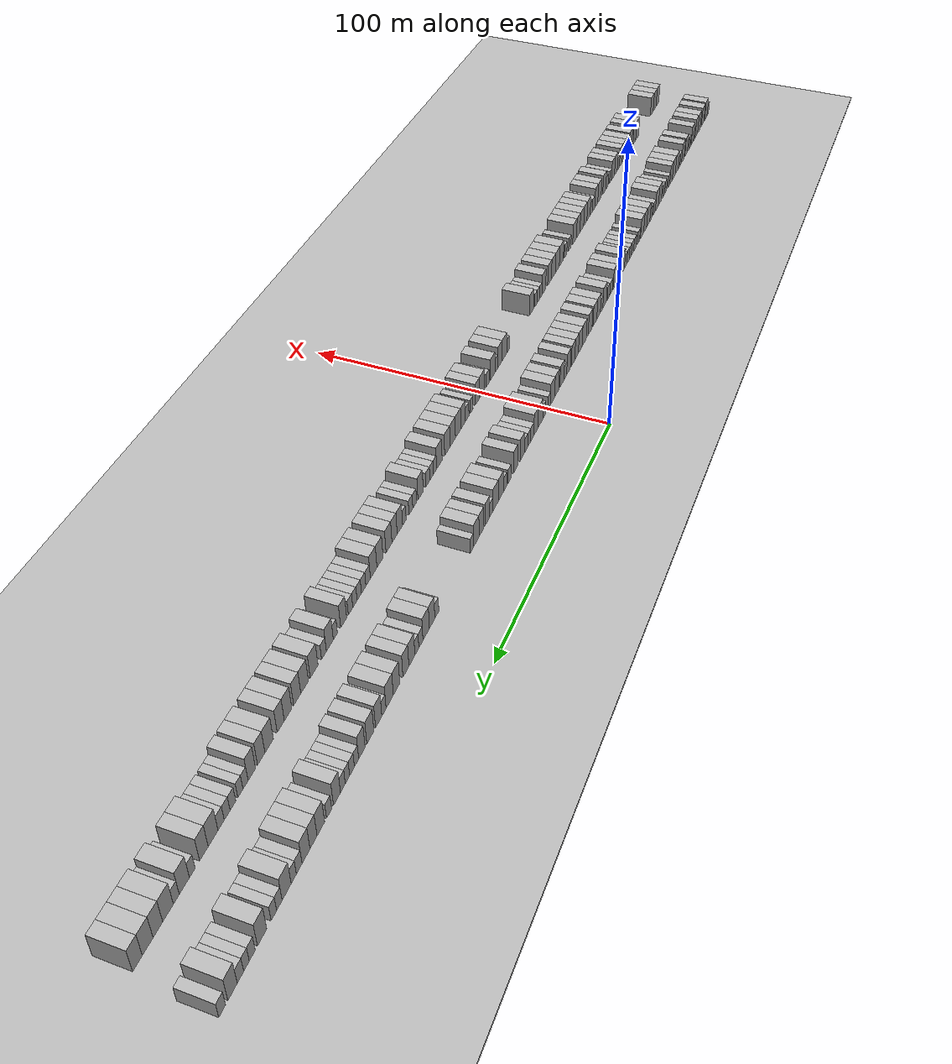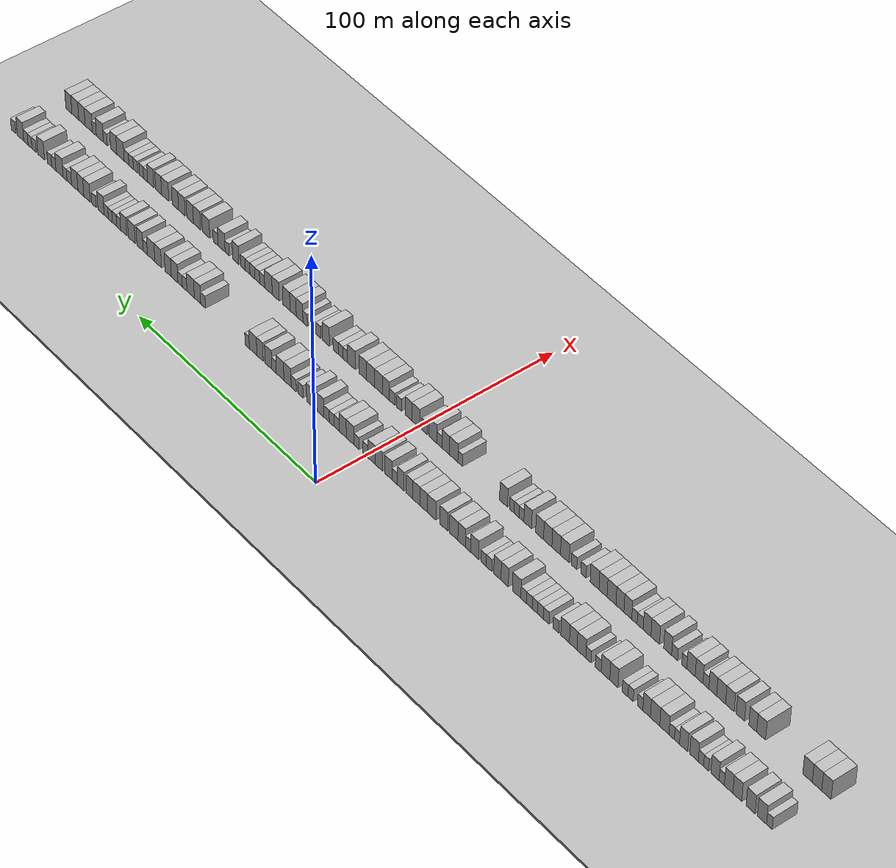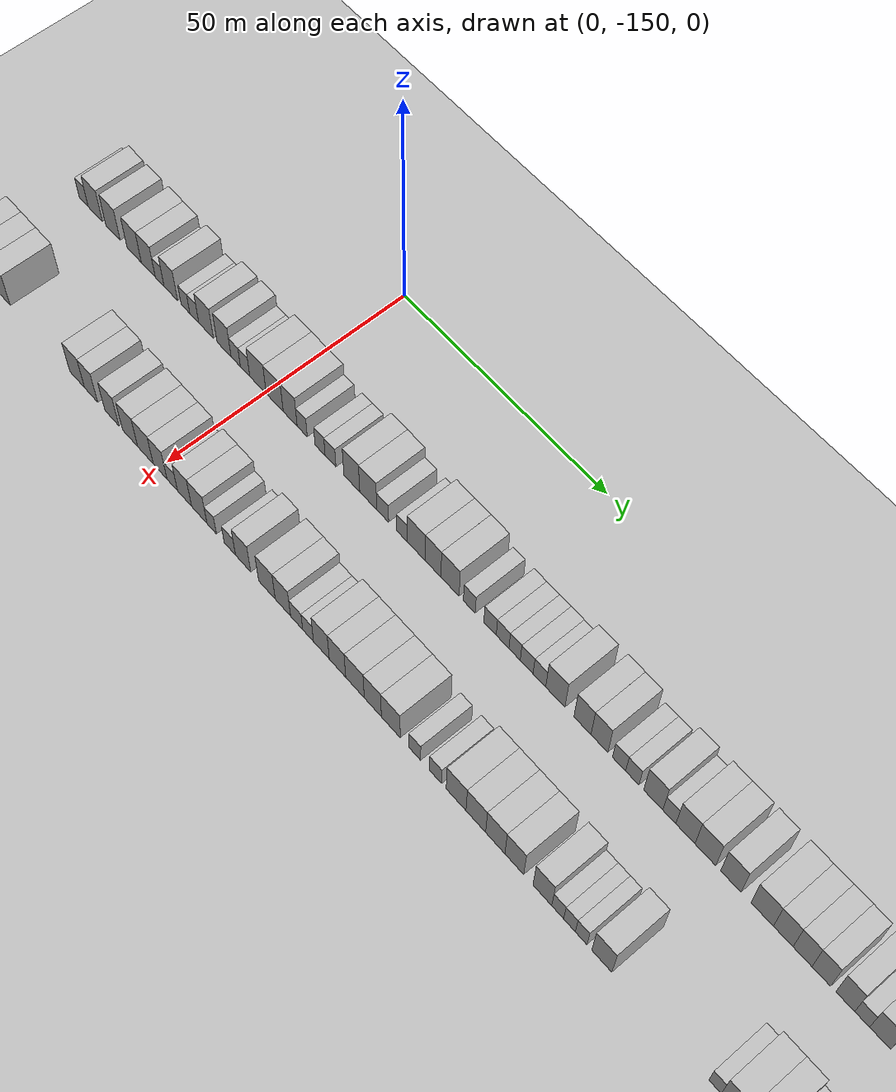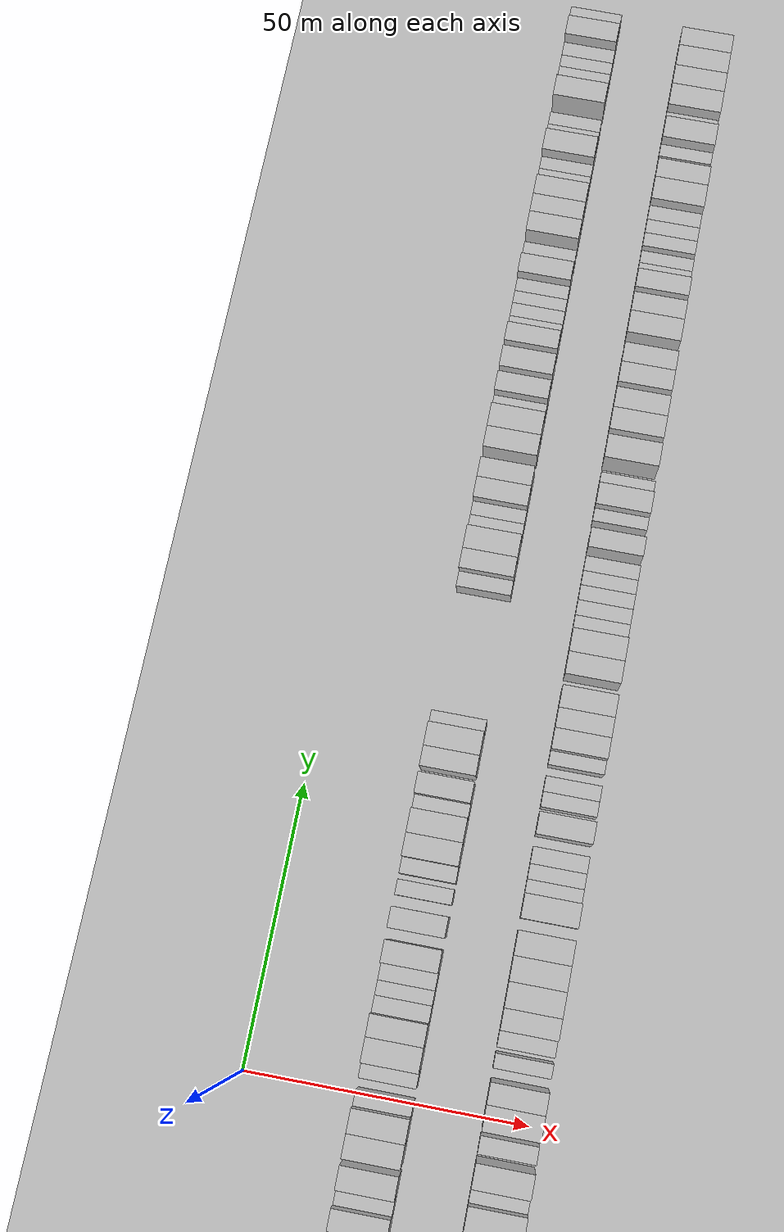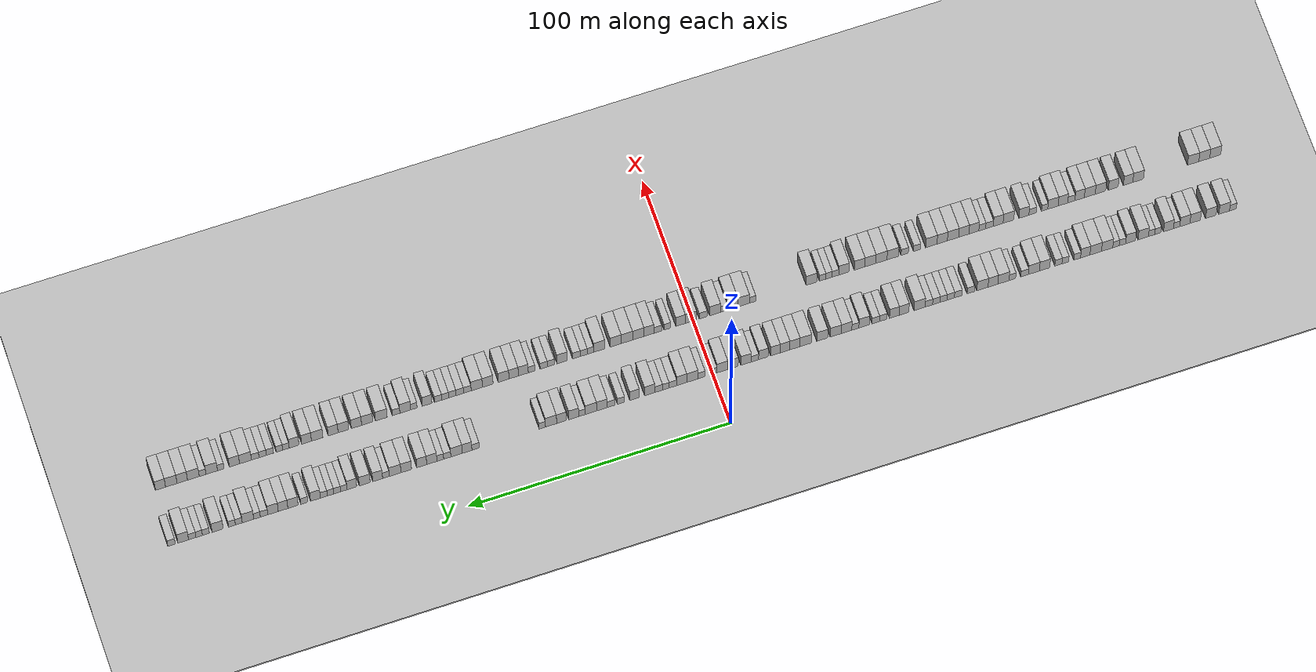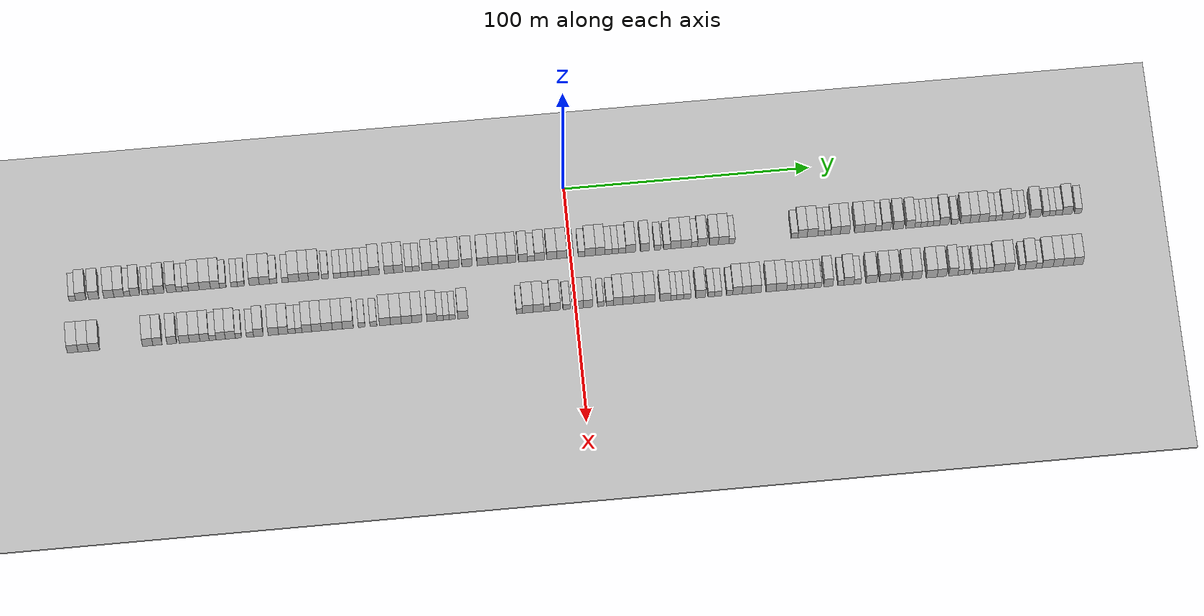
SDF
<?xml version="1.0" encoding="utf-8"?>

<sdf version="1.6">

   <world name="default">

      <gui fullscreen="0">

         <camera name="user_camera">

            <pose>-15 0 4.57585 0 0 0</pose>

            <view_controller>orbit</view_controller>

         </camera>

      </gui>

      <scene>

         <sky>

           <clouds>

             <speed>12</speed>

           </clouds>

         </sky>

         <ambient>0.4 0.4 0.4 1</ambient>

         <background>0.7 0.7 0.7 1</background>

         <shadows>1</shadows>

      </scene>

      <gravity>0 0 -9.8066</gravity>

      <magnetic_field>6e-06 2.3e-05 -4.2e-05</magnetic_field>

      <physics default="0" name="default_physics" type="ode">

         <ode>

            <solver>

               <type>quick</type>

               <iters>10</iters>

               <sor>1.0</sor>

               <use_dynamic_moi_rescaling>0</use_dynamic_moi_rescaling>

            </solver>

            <constraints>

               <cfm>0</cfm>

               <erp>0.2</erp>

               <contact_max_correcting_vel>100</contact_max_correcting_vel>

               <contact_surface_layer>0.001</contact_surface_layer>

            </constraints>

         </ode>

         <max_step_size>0.004</max_step_size>

         <real_time_factor>1</real_time_factor>

         <real_time_update_rate>250</real_time_update_rate>

      </physics>

      <light name="sun" type="directional">

         <cast_shadows>1</cast_shadows>

         <pose>0 0 10 0 0 0</pose>

         <diffuse>0.8 0.8 0.8 1</diffuse>

         <specular>0.2 0.2 0.2 1</specular>

         <attenuation>

            <range>1000</range>

            <constant>0.9</constant>

            <linear>0.01</linear>

            <quadratic>0.001</quadratic>

         </attenuation>

         <direction>-0.5 0.1 -0.9</direction>

      </light>

      <include>

         <name>ground_plane_1</name>

         <uri>model://HANNAS_ground_plane</uri>

         <pose>0 0 0  0 0 0</pose>

      </include>

      <include>

         <name>ground_plane_2</name>

         <uri>model://HANNAS_ground_plane</uri>

         <pose>100 0 0  0 0 0</pose>

      </include>

      <model name="building_1">

         <static>1</static>

         <pose frame="">25.0000 -200.6891 0 0.000000 0.000000 0.000000</pose>

         <link name="link">

            <pose frame="">0 0 3.00 0 0 0</pose>

            <collision name="collision">

               <geometry>

                  <box>

                     <size>10.0000 2.6218 6.0000</size>

                  </box>

               </geometry>

               <max_contacts>10</max_contacts>

               <surface>

                  <contact>

                     <ode/>

                  </contact>

                  <bounce/>

                  <friction>

                     <torsional>

                        <ode/>

                     </torsional>

                     <ode/>

                  </friction>

               </surface>

            </collision>

            <visual name="visual">

               <cast_shadows>0</cast_shadows>

               <geometry>

                  <box>

                     <size>10.0000 2.6218 6.0000</size>

                  </box>

               </geometry>

               <material>

                  <script>

                     <uri>model://HANNAS_wall/materials/scripts</uri>

                     <uri>model://HANNAS_wall/materials/textures</uri>

                     <name>vrc/HANNAS_wall</name>

                  </script>

               </material>

            </visual>

            <self_collide>0</self_collide>

            <enable_wind>0</enable_wind>

            <kinematic>0</kinematic>

         </link>

      </model>

      <model name="building_2">

         <static>1</static>

         <pose frame="">25.0000 -197.2870 0 0.000000 0.000000 0.000000</pose>

         <link name="link">

            <pose frame="">0 0 4.50 0 0 0</pose>

            <collision name="collision">

               <geometry>

                  <box>

                     <size>10.0000 4.1824 9.0000</size>

                  </box>

               </geometry>

               <max_contacts>10</max_contacts>

               <surface>

                  <contact>

                     <ode/>

                  </contact>

                  <bounce/>

                  <friction>

                     <torsional>

                        <ode/>

                     </torsional>

                     <ode/>

                  </friction>

               </surface>

            </collision>

            <visual name="visual">

               <cast_shadows>0</cast_shadows>

               <geometry>

                  <box>

                     <size>10.0000 4.1824 9.0000</size>

                  </box>

               </geometry>

               <material>

                  <script>

                     <uri>model://HANNAS_wall/materials/scripts</uri>

                     <uri>model://HANNAS_wall/materials/textures</uri>

                     <name>vrc/HANNAS_wall</name>

                  </script>

               </material>

            </visual>

            <self_collide>0</self_collide>

            <enable_wind>0</enable_wind>

            <kinematic>0</kinematic>

         </link>

      </model>

      <model name="building_3">

         <static>1</static>

         <pose frame="">25.0000 -192.1201 0 0.000000 0.000000 0.000000</pose>

         <link name="link">

            <pose frame="">0 0 4.50 0 0 0</pose>

            <collision name="collision">

               <geometry>

                  <box>

                     <size>10.0000 4.1514 9.0000</size>

                  </box>

               </geometry>

               <max_contacts>10</max_contacts>

               <surface>

                  <contact>

                     <ode/>

                  </contact>

                  <bounce/>

                  <friction>

                     <torsional>

                        <ode/>

                     </torsional>

                     <ode/>

                  </friction>

               </surface>

            </collision>

            <visual name="visual">

               <cast_shadows>0</cast_shadows>

               <geometry>

                  <box>

                     <size>10.0000 4.1514 9.0000</size>

                  </box>

               </geometry>

               <material>

                  <script>

                     <uri>model://HANNAS_wall/materials/scripts</uri>

                     <uri>model://HANNAS_wall/materials/textures</uri>

                     <name>vrc/HANNAS_wall</name>

                  </script>

               </material>

            </visual>

            <self_collide>0</self_collide>

            <enable_wind>0</enable_wind>

            <kinematic>0</kinematic>

         </link>

      </model>

      <model name="building_4">

         <static>1</static>

         <pose frame="">25.0000 -185.9952 0 0.000000 0.000000 0.000000</pose>

         <link name="link">

            <pose frame="">0 0 4.50 0 0 0</pose>

            <collision name="collision">

               <geometry>

                  <box>

                     <size>10.0000 4.0984 9.0000</size>

                  </box>

               </geometry>

               <max_contacts>10</max_contacts>

               <surface>

                  <contact>

                     <ode/>

                  </contact>

                  <bounce/>

                  <friction>

                     <torsional>

                        <ode/>

                     </torsional>

                     <ode/>

                  </friction>

               </surface>

            </collision>

            <visual name="visual">

               <cast_shadows>0</cast_shadows>

               <geometry>

                  <box>

                     <size>10.0000 4.0984 9.0000</size>

                  </box>

               </geometry>

               <material>

                  <script>

                     <uri>model://HANNAS_wall/materials/scripts</uri>

                     <uri>model://HANNAS_wall/materials/textures</uri>

                     <name>vrc/HANNAS_wall</name>

                  </script>

               </material>

            </visual>

            <self_collide>0</self_collide>

            <enable_wind>0</enable_wind>

            <kinematic>0</kinematic>

         </link>

      </model>

      <model name="building_5">

         <static>1</static>

         <pose frame="">25.0000 -181.9679 0 0.000000 0.000000 0.000000</pose>

         <link name="link">

            <pose frame="">0 0 4.50 0 0 0</pose>

            <collision name="collision">

               <geometry>

                  <box>

                     <size>10.0000 3.9561 9.0000</size>

                  </box>

               </geometry>

               <max_contacts>10</max_contacts>

               <surface>

                  <contact>

                     <ode/>

                  </contact>

                  <bounce/>

                  <friction>

                     <torsional>

                        <ode/>

                     </torsional>

                     <ode/>

                  </friction>

               </surface>

            </collision>

            <visual name="visual">

               <cast_shadows>0</cast_shadows>

               <geometry>

                  <box>

                     <size>10.0000 3.9561 9.0000</size>

                  </box>

               </geometry>

               <material>

                  <script>

                     <uri>model://HANNAS_wall/materials/scripts</uri>

                     <uri>model://HANNAS_wall/materials/textures</uri>

                     <name>vrc/HANNAS_wall</name>

                  </script>

               </material>

            </visual>

            <self_collide>0</self_collide>

            <enable_wind>0</enable_wind>

            <kinematic>0</kinematic>

         </link>

      </model>

      <model name="building_6">

         <static>1</static>

         <pose frame="">25.0000 -178.7578 0 0.000000 0.000000 0.000000</pose>

         <link name="link">

            <pose frame="">0 0 3.00 0 0 0</pose>

            <collision name="collision">

               <geometry>

                  <box>

                     <size>10.0000 2.4642 6.0000</size>

                  </box>

               </geometry>

               <max_contacts>10</max_contacts>

               <surface>

                  <contact>

                     <ode/>

                  </contact>

                  <bounce/>

                  <friction>

                     <torsional>

                        <ode/>

                     </torsional>

                     <ode/>

                  </friction>

               </surface>

            </collision>

            <visual name="visual">

               <cast_shadows>0</cast_shadows>

               <geometry>

                  <box>

                     <size>10.0000 2.4642 6.0000</size>

                  </box>

               </geometry>

               <material>

                  <script>

                     <uri>model://HANNAS_wall/materials/scripts</uri>

                     <uri>model://HANNAS_wall/materials/textures</uri>

                     <name>vrc/HANNAS_wall</name>

                  </script>

               </material>

            </visual>

            <self_collide>0</self_collide>

            <enable_wind>0</enable_wind>

            <kinematic>0</kinematic>

         </link>

      </model>

      <model name="building_7">

         <static>1</static>

         <pose frame="">25.0000 -175.6219 0 0.000000 0.000000 0.000000</pose>

         <link name="link">

            <pose frame="">0 0 4.50 0 0 0</pose>

            <collision name="collision">

               <geometry>

                  <box>

                     <size>10.0000 3.8075 9.0000</size>

                  </box>

               </geometry>

               <max_contacts>10</max_contacts>

               <surface>

                  <contact>

                     <ode/>

                  </contact>

                  <bounce/>

                  <friction>

                     <torsional>

                        <ode/>

                     </torsional>

                     <ode/>

                  </friction>

               </surface>

            </collision>

            <visual name="visual">

               <cast_shadows>0</cast_shadows>

               <geometry>

                  <box>

                     <size>10.0000 3.8075 9.0000</size>

                  </box>

               </geometry>

               <material>

                  <script>

                     <uri>model://HANNAS_wall/materials/scripts</uri>

                     <uri>model://HANNAS_wall/materials/textures</uri>

                     <name>vrc/HANNAS_wall</name>

                  </script>

               </material>

            </visual>

            <self_collide>0</self_collide>

            <enable_wind>0</enable_wind>

            <kinematic>0</kinematic>

         </link>

      </model>

      <model name="building_8">

         <static>1</static>

         <pose frame="">25.0000 -171.5128 0 0.000000 0.000000 0.000000</pose>

         <link name="link">

            <pose frame="">0 0 3.00 0 0 0</pose>

            <collision name="collision">

               <geometry>

                  <box>

                     <size>10.0000 2.4107 6.0000</size>

                  </box>

               </geometry>

               <max_contacts>10</max_contacts>

               <surface>

                  <contact>

                     <ode/>

                  </contact>

                  <bounce/>

                  <friction>

                     <torsional>

                        <ode/>

                     </torsional>

                     <ode/>

                  </friction>

               </surface>

            </collision>

            <visual name="visual">

               <cast_shadows>0</cast_shadows>

               <geometry>

                  <box>

                     <size>10.0000 2.4107 6.0000</size>

                  </box>

               </geometry>

               <material>

                  <script>

                     <uri>model://HANNAS_wall/materials/scripts</uri>

                     <uri>model://HANNAS_wall/materials/textures</uri>

                     <name>vrc/HANNAS_wall</name>

                  </script>

               </material>

            </visual>

            <self_collide>0</self_collide>

            <enable_wind>0</enable_wind>

            <kinematic>0</kinematic>

         </link>

      </model>

      <model name="building_9">

         <static>1</static>

         <pose frame="">25.0000 -169.0757 0 0.000000 0.000000 0.000000</pose>

         <link name="link">

            <pose frame="">0 0 3.00 0 0 0</pose>

            <collision name="collision">

               <geometry>

                  <box>

                     <size>10.0000 2.4634 6.0000</size>

                  </box>

               </geometry>

               <max_contacts>10</max_contacts>

               <surface>

                  <contact>

                     <ode/>

                  </contact>

                  <bounce/>

                  <friction>

                     <torsional>

                        <ode/>

                     </torsional>

                     <ode/>

                  </friction>

               </surface>

            </collision>

            <visual name="visual">

               <cast_shadows>0</cast_shadows>

               <geometry>

                  <box>

                     <size>10.0000 2.4634 6.0000</size>

                  </box>

               </geometry>

               <material>

                  <script>

                     <uri>model://HANNAS_wall/materials/scripts</uri>

                     <uri>model://HANNAS_wall/materials/textures</uri>

                     <name>vrc/HANNAS_wall</name>

                  </script>

               </material>

            </visual>

            <self_collide>0</self_collide>

            <enable_wind>0</enable_wind>

            <kinematic>0</kinematic>

         </link>

      </model>

      <model name="building_10">

         <static>1</static>

         <pose frame="">25.0000 -165.8358 0 0.000000 0.000000 0.000000</pose>

         <link name="link">

            <pose frame="">0 0 4.50 0 0 0</pose>

            <collision name="collision">

               <geometry>

                  <box>

                     <size>10.0000 4.0163 9.0000</size>

                  </box>

               </geometry>

               <max_contacts>10</max_contacts>

               <surface>

                  <contact>

                     <ode/>

                  </contact>

                  <bounce/>

                  <friction>

                     <torsional>

                        <ode/>

                     </torsional>

                     <ode/>

                  </friction>

               </surface>

            </collision>

            <visual name="visual">

               <cast_shadows>0</cast_shadows>

               <geometry>

                  <box>

                     <size>10.0000 4.0163 9.0000</size>

                  </box>

               </geometry>

               <material>

                  <script>

                     <uri>model://HANNAS_wall/materials/scripts</uri>

                     <uri>model://HANNAS_wall/materials/textures</uri>

                     <name>vrc/HANNAS_wall</name>

                  </script>

               </material>

            </visual>

            <self_collide>0</self_collide>

            <enable_wind>0</enable_wind>

            <kinematic>0</kinematic>

         </link>

      </model>

      <model name="building_11">

         <static>1</static>

         <pose frame="">25.0000 -160.9196 0 0.000000 0.000000 0.000000</pose>

         <link name="link">

            <pose frame="">0 0 4.50 0 0 0</pose>

            <collision name="collision">

               <geometry>

                  <box>

                     <size>10.0000 3.8163 9.0000</size>

                  </box>

               </geometry>

               <max_contacts>10</max_contacts>

               <surface>

                  <contact>

                     <ode/>

                  </contact>

                  <bounce/>

                  <friction>

                     <torsional>

                        <ode/>

                     </torsional>

                     <ode/>

                  </friction>

               </surface>

            </collision>

            <visual name="visual">

               <cast_shadows>0</cast_shadows>

               <geometry>

                  <box>

                     <size>10.0000 3.8163 9.0000</size>

                  </box>

               </geometry>

               <material>

                  <script>

                     <uri>model://HANNAS_wall/materials/scripts</uri>

                     <uri>model://HANNAS_wall/materials/textures</uri>

                     <name>vrc/HANNAS_wall</name>

                  </script>

               </material>

            </visual>

            <self_collide>0</self_collide>

            <enable_wind>0</enable_wind>

            <kinematic>0</kinematic>

         </link>

      </model>

      <model name="building_12">

         <static>1</static>

         <pose frame="">25.0000 -157.7685 0 0.000000 0.000000 0.000000</pose>

         <link name="link">

            <pose frame="">0 0 3.00 0 0 0</pose>

            <collision name="collision">

               <geometry>

                  <box>

                     <size>10.0000 2.4858 6.0000</size>

                  </box>

               </geometry>

               <max_contacts>10</max_contacts>

               <surface>

                  <contact>

                     <ode/>

                  </contact>

                  <bounce/>

                  <friction>

                     <torsional>

                        <ode/>

                     </torsional>

                     <ode/>

                  </friction>

               </surface>

            </collision>

            <visual name="visual">

               <cast_shadows>0</cast_shadows>

               <geometry>

                  <box>

                     <size>10.0000 2.4858 6.0000</size>

                  </box>

               </geometry>

               <material>

                  <script>

                     <uri>model://HANNAS_wall/materials/scripts</uri>

                     <uri>model://HANNAS_wall/materials/textures</uri>

                     <name>vrc/HANNAS_wall</name>

                  </script>

               </material>

            </visual>

            <self_collide>0</self_collide>

            <enable_wind>0</enable_wind>

            <kinematic>0</kinematic>

         </link>

      </model>

      <model name="building_13">

         <static>1</static>

         <pose frame="">25.0000 -155.2720 0 0.000000 0.000000 0.000000</pose>

         <link name="link">

            <pose frame="">0 0 3.00 0 0 0</pose>

            <collision name="collision">

               <geometry>

                  <box>

                     <size>10.0000 2.5074 6.0000</size>

                  </box>

               </geometry>

               <max_contacts>10</max_contacts>

               <surface>

                  <contact>

                     <ode/>

                  </contact>

                  <bounce/>

                  <friction>

                     <torsional>

                        <ode/>

                     </torsional>

                     <ode/>

                  </friction>

               </surface>

            </collision>

            <visual name="visual">

               <cast_shadows>0</cast_shadows>

               <geometry>

                  <box>

                     <size>10.0000 2.5074 6.0000</size>

                  </box>

               </geometry>

               <material>

                  <script>

                     <uri>model://HANNAS_wall/materials/scripts</uri>

                     <uri>model://HANNAS_wall/materials/textures</uri>

                     <name>vrc/HANNAS_wall</name>

                  </script>

               </material>

            </visual>

            <self_collide>0</self_collide>

            <enable_wind>0</enable_wind>

            <kinematic>0</kinematic>

         </link>

      </model>

      <model name="building_14">

         <static>1</static>

         <pose frame="">25.0000 -151.8228 0 0.000000 0.000000 0.000000</pose>

         <link name="link">

            <pose frame="">0 0 4.50 0 0 0</pose>

            <collision name="collision">

               <geometry>

                  <box>

                     <size>10.0000 4.3909 9.0000</size>

                  </box>

               </geometry>

               <max_contacts>10</max_contacts>

               <surface>

                  <contact>

                     <ode/>

                  </contact>

                  <bounce/>

                  <friction>

                     <torsional>

                        <ode/>

                     </torsional>

                     <ode/>

                  </friction>

               </surface>

            </collision>

            <visual name="visual">

               <cast_shadows>0</cast_shadows>

               <geometry>

                  <box>

                     <size>10.0000 4.3909 9.0000</size>

                  </box>

               </geometry>

               <material>

                  <script>

                     <uri>model://HANNAS_wall/materials/scripts</uri>

                     <uri>model://HANNAS_wall/materials/textures</uri>

                     <name>vrc/HANNAS_wall</name>

                  </script>

               </material>

            </visual>

            <self_collide>0</self_collide>

            <enable_wind>0</enable_wind>

            <kinematic>0</kinematic>

         </link>

      </model>

      <model name="building_15">

         <static>1</static>

         <pose frame="">25.0000 -147.3984 0 0.000000 0.000000 0.000000</pose>

         <link name="link">

            <pose frame="">0 0 4.50 0 0 0</pose>

            <collision name="collision">

               <geometry>

                  <box>

                     <size>10.0000 4.4581 9.0000</size>

                  </box>

               </geometry>

               <max_contacts>10</max_contacts>

               <surface>

                  <contact>

                     <ode/>

                  </contact>

                  <bounce/>

                  <friction>

                     <torsional>

                        <ode/>

                     </torsional>

                     <ode/>

                  </friction>

               </surface>

            </collision>

            <visual name="visual">

               <cast_shadows>0</cast_shadows>

               <geometry>

                  <box>

                     <size>10.0000 4.4581 9.0000</size>

                  </box>

               </geometry>

               <material>

                  <script>

                     <uri>model://HANNAS_wall/materials/scripts</uri>

                     <uri>model://HANNAS_wall/materials/textures</uri>

                     <name>vrc/HANNAS_wall</name>

                  </script>

               </material>

            </visual>

            <self_collide>0</self_collide>

            <enable_wind>0</enable_wind>

            <kinematic>0</kinematic>

         </link>

      </model>

      <model name="building_16">

         <static>1</static>

         <pose frame="">25.0000 -143.3528 0 0.000000 0.000000 0.000000</pose>

         <link name="link">

            <pose frame="">0 0 4.50 0 0 0</pose>

            <collision name="collision">

               <geometry>

                  <box>

                     <size>10.0000 3.6331 9.0000</size>

                  </box>

               </geometry>

               <max_contacts>10</max_contacts>

               <surface>

                  <contact>

                     <ode/>

                  </contact>

                  <bounce/>

                  <friction>

                     <torsional>

                        <ode/>

                     </torsional>

                     <ode/>

                  </friction>

               </surface>

            </collision>

            <visual name="visual">

               <cast_shadows>0</cast_shadows>

               <geometry>

                  <box>

                     <size>10.0000 3.6331 9.0000</size>

                  </box>

               </geometry>

               <material>

                  <script>

                     <uri>model://HANNAS_wall/materials/scripts</uri>

                     <uri>model://HANNAS_wall/materials/textures</uri>

                     <name>vrc/HANNAS_wall</name>

                  </script>

               </material>

            </visual>

            <self_collide>0</self_collide>

            <enable_wind>0</enable_wind>

            <kinematic>0</kinematic>

         </link>

      </model>

      <model name="building_17">

         <static>1</static>

         <pose frame="">25.0000 -140.2241 0 0.000000 0.000000 0.000000</pose>

         <link name="link">

            <pose frame="">0 0 3.00 0 0 0</pose>

            <collision name="collision">

               <geometry>

                  <box>

                     <size>10.0000 2.6244 6.0000</size>

                  </box>

               </geometry>

               <max_contacts>10</max_contacts>

               <surface>

                  <contact>

                     <ode/>

                  </contact>

                  <bounce/>

                  <friction>

                     <torsional>

                        <ode/>

                     </torsional>

                     <ode/>

                  </friction>

               </surface>

            </collision>

            <visual name="visual">

               <cast_shadows>0</cast_shadows>

               <geometry>

                  <box>

                     <size>10.0000 2.6244 6.0000</size>

                  </box>

               </geometry>

               <material>

                  <script>

                     <uri>model://HANNAS_wall/materials/scripts</uri>

                     <uri>model://HANNAS_wall/materials/textures</uri>

                     <name>vrc/HANNAS_wall</name>

                  </script>

               </material>

            </visual>

            <self_collide>0</self_collide>

            <enable_wind>0</enable_wind>

            <kinematic>0</kinematic>

         </link>

      </model>

      <model name="building_18">

         <static>1</static>

         <pose frame="">25.0000 -135.6285 0 0.000000 0.000000 0.000000</pose>

         <link name="link">

            <pose frame="">0 0 3.00 0 0 0</pose>

            <collision name="collision">

               <geometry>

                  <box>

                     <size>10.0000 2.5668 6.0000</size>

                  </box>

               </geometry>

               <max_contacts>10</max_contacts>

               <surface>

                  <contact>

                     <ode/>

                  </contact>

                  <bounce/>

                  <friction>

                     <torsional>

                        <ode/>

                     </torsional>

                     <ode/>

                  </friction>

               </surface>

            </collision>

            <visual name="visual">

               <cast_shadows>0</cast_shadows>

               <geometry>

                  <box>

                     <size>10.0000 2.5668 6.0000</size>

                  </box>

               </geometry>

               <material>

                  <script>

                     <uri>model://HANNAS_wall/materials/scripts</uri>

                     <uri>model://HANNAS_wall/materials/textures</uri>

                     <name>vrc/HANNAS_wall</name>

                  </script>

               </material>

            </visual>

            <self_collide>0</self_collide>

            <enable_wind>0</enable_wind>

            <kinematic>0</kinematic>

         </link>

      </model>

      <model name="building_19">

         <static>1</static>

         <pose frame="">25.0000 -132.9644 0 0.000000 0.000000 0.000000</pose>

         <link name="link">

            <pose frame="">0 0 3.00 0 0 0</pose>

            <collision name="collision">

               <geometry>

                  <box>

                     <size>10.0000 2.7615 6.0000</size>

                  </box>

               </geometry>

               <max_contacts>10</max_contacts>

               <surface>

                  <contact>

                     <ode/>

                  </contact>

                  <bounce/>

                  <friction>

                     <torsional>

                        <ode/>

                     </torsional>

                     <ode/>

                  </friction>

               </surface>

            </collision>

            <visual name="visual">

               <cast_shadows>0</cast_shadows>

               <geometry>

                  <box>

                     <size>10.0000 2.7615 6.0000</size>

                  </box>

               </geometry>

               <material>

                  <script>

                     <uri>model://HANNAS_wall/materials/scripts</uri>

                     <uri>model://HANNAS_wall/materials/textures</uri>

                     <name>vrc/HANNAS_wall</name>

                  </script>

               </material>

            </visual>

            <self_collide>0</self_collide>

            <enable_wind>0</enable_wind>

            <kinematic>0</kinematic>

         </link>

      </model>

      <model name="building_20">

         <static>1</static>

         <pose frame="">25.0000 -127.5885 0 0.000000 0.000000 0.000000</pose>

         <link name="link">

            <pose frame="">0 0 4.50 0 0 0</pose>

            <collision name="collision">

               <geometry>

                  <box>

                     <size>10.0000 3.9903 9.0000</size>

                  </box>

               </geometry>

               <max_contacts>10</max_contacts>

               <surface>

                  <contact>

                     <ode/>

                  </contact>

                  <bounce/>

                  <friction>

                     <torsional>

                        <ode/>

                     </torsional>

                     <ode/>

                  </friction>

               </surface>

            </collision>

            <visual name="visual">

               <cast_shadows>0</cast_shadows>

               <geometry>

                  <box>

                     <size>10.0000 3.9903 9.0000</size>

                  </box>

               </geometry>

               <material>

                  <script>

                     <uri>model://HANNAS_wall/materials/scripts</uri>

                     <uri>model://HANNAS_wall/materials/textures</uri>

                     <name>vrc/HANNAS_wall</name>

                  </script>

               </material>

            </visual>

            <self_collide>0</self_collide>

            <enable_wind>0</enable_wind>

            <kinematic>0</kinematic>

         </link>

      </model>

      <model name="building_21">

         <static>1</static>

         <pose frame="">25.0000 -123.4686 0 0.000000 0.000000 0.000000</pose>

         <link name="link">

            <pose frame="">0 0 4.50 0 0 0</pose>

            <collision name="collision">

               <geometry>

                  <box>

                     <size>10.0000 4.2495 9.0000</size>

                  </box>

               </geometry>

               <max_contacts>10</max_contacts>

               <surface>

                  <contact>

                     <ode/>

                  </contact>

                  <bounce/>

                  <friction>

                     <torsional>

                        <ode/>

                     </torsional>

                     <ode/>

                  </friction>

               </surface>

            </collision>

            <visual name="visual">

               <cast_shadows>0</cast_shadows>

               <geometry>

                  <box>

                     <size>10.0000 4.2495 9.0000</size>

                  </box>

               </geometry>

               <material>

                  <script>

                     <uri>model://HANNAS_wall/materials/scripts</uri>

                     <uri>model://HANNAS_wall/materials/textures</uri>

                     <name>vrc/HANNAS_wall</name>

                  </script>

               </material>

            </visual>

            <self_collide>0</self_collide>

            <enable_wind>0</enable_wind>

            <kinematic>0</kinematic>

         </link>

      </model>

      <model name="building_22">

         <static>1</static>

         <pose frame="">25.0000 -119.8854 0 0.000000 0.000000 0.000000</pose>

         <link name="link">

            <pose frame="">0 0 3.00 0 0 0</pose>

            <collision name="collision">

               <geometry>

                  <box>

                     <size>10.0000 2.9168 6.0000</size>

                  </box>

               </geometry>

               <max_contacts>10</max_contacts>

               <surface>

                  <contact>

                     <ode/>

                  </contact>

                  <bounce/>

                  <friction>

                     <torsional>

                        <ode/>

                     </torsional>

                     <ode/>

                  </friction>

               </surface>

            </collision>

            <visual name="visual">

               <cast_shadows>0</cast_shadows>

               <geometry>

                  <box>

                     <size>10.0000 2.9168 6.0000</size>

                  </box>

               </geometry>

               <material>

                  <script>

                     <uri>model://HANNAS_wall/materials/scripts</uri>

                     <uri>model://HANNAS_wall/materials/textures</uri>

                     <name>vrc/HANNAS_wall</name>

                  </script>

               </material>

            </visual>

            <self_collide>0</self_collide>

            <enable_wind>0</enable_wind>

            <kinematic>0</kinematic>

         </link>

      </model>

      <model name="building_23">

         <static>1</static>

         <pose frame="">25.0000 -115.1533 0 0.000000 0.000000 0.000000</pose>

         <link name="link">

            <pose frame="">0 0 3.00 0 0 0</pose>

            <collision name="collision">

               <geometry>

                  <box>

                     <size>10.0000 2.5473 6.0000</size>

                  </box>

               </geometry>

               <max_contacts>10</max_contacts>

               <surface>

                  <contact>

                     <ode/>

                  </contact>

                  <bounce/>

                  <friction>

                     <torsional>

                        <ode/>

                     </torsional>

                     <ode/>

                  </friction>

               </surface>

            </collision>

            <visual name="visual">

               <cast_shadows>0</cast_shadows>

               <geometry>

                  <box>

                     <size>10.0000 2.5473 6.0000</size>

                  </box>

               </geometry>

               <material>

                  <script>

                     <uri>model://HANNAS_wall/materials/scripts</uri>

                     <uri>model://HANNAS_wall/materials/textures</uri>

                     <name>vrc/HANNAS_wall</name>

                  </script>

               </material>

            </visual>

            <self_collide>0</self_collide>

            <enable_wind>0</enable_wind>

            <kinematic>0</kinematic>

         </link>

      </model>

      <model name="building_24">

         <static>1</static>

         <pose frame="">25.0000 -111.7035 0 0.000000 0.000000 0.000000</pose>

         <link name="link">

            <pose frame="">0 0 4.50 0 0 0</pose>

            <collision name="collision">

               <geometry>

                  <box>

                     <size>10.0000 4.3524 9.0000</size>

                  </box>

               </geometry>

               <max_contacts>10</max_contacts>

               <surface>

                  <contact>

                     <ode/>

                  </contact>

                  <bounce/>

                  <friction>

                     <torsional>

                        <ode/>

                     </torsional>

                     <ode/>

                  </friction>

               </surface>

            </collision>

            <visual name="visual">

               <cast_shadows>0</cast_shadows>

               <geometry>

                  <box>

                     <size>10.0000 4.3524 9.0000</size>

                  </box>

               </geometry>

               <material>

                  <script>

                     <uri>model://HANNAS_wall/materials/scripts</uri>

                     <uri>model://HANNAS_wall/materials/textures</uri>

                     <name>vrc/HANNAS_wall</name>

                  </script>

               </material>

            </visual>

            <self_collide>0</self_collide>

            <enable_wind>0</enable_wind>

            <kinematic>0</kinematic>

         </link>

      </model>

      <model name="building_25">

         <static>1</static>

         <pose frame="">25.0000 -107.6400 0 0.000000 0.000000 0.000000</pose>

         <link name="link">

            <pose frame="">0 0 4.50 0 0 0</pose>

            <collision name="collision">

               <geometry>

                  <box>

                     <size>10.0000 3.7747 9.0000</size>

                  </box>

               </geometry>

               <max_contacts>10</max_contacts>

               <surface>

                  <contact>

                     <ode/>

                  </contact>

                  <bounce/>

                  <friction>

                     <torsional>

                        <ode/>

                     </torsional>

                     <ode/>

                  </friction>

               </surface>

            </collision>

            <visual name="visual">

               <cast_shadows>0</cast_shadows>

               <geometry>

                  <box>

                     <size>10.0000 3.7747 9.0000</size>

                  </box>

               </geometry>

               <material>

                  <script>

                     <uri>model://HANNAS_wall/materials/scripts</uri>

                     <uri>model://HANNAS_wall/materials/textures</uri>

                     <name>vrc/HANNAS_wall</name>

                  </script>

               </material>

            </visual>

            <self_collide>0</self_collide>

            <enable_wind>0</enable_wind>

            <kinematic>0</kinematic>

         </link>

      </model>

      <model name="building_26">

         <static>1</static>

         <pose frame="">25.0000 -103.5955 0 0.000000 0.000000 0.000000</pose>

         <link name="link">

            <pose frame="">0 0 4.50 0 0 0</pose>

            <collision name="collision">

               <geometry>

                  <box>

                     <size>10.0000 4.3142 9.0000</size>

                  </box>

               </geometry>

               <max_contacts>10</max_contacts>

               <surface>

                  <contact>

                     <ode/>

                  </contact>

                  <bounce/>

                  <friction>

                     <torsional>

                        <ode/>

                     </torsional>

                     <ode/>

                  </friction>

               </surface>

            </collision>

            <visual name="visual">

               <cast_shadows>0</cast_shadows>

               <geometry>

                  <box>

                     <size>10.0000 4.3142 9.0000</size>

                  </box>

               </geometry>

               <material>

                  <script>

                     <uri>model://HANNAS_wall/materials/scripts</uri>

                     <uri>model://HANNAS_wall/materials/textures</uri>

                     <name>vrc/HANNAS_wall</name>

                  </script>

               </material>

            </visual>

            <self_collide>0</self_collide>

            <enable_wind>0</enable_wind>

            <kinematic>0</kinematic>

         </link>

      </model>

      <model name="building_27">

         <static>1</static>

         <pose frame="">25.0000 -99.0458 0 0.000000 0.000000 0.000000</pose>

         <link name="link">

            <pose frame="">0 0 3.00 0 0 0</pose>

            <collision name="collision">

               <geometry>

                  <box>

                     <size>10.0000 2.7853 6.0000</size>

                  </box>

               </geometry>

               <max_contacts>10</max_contacts>

               <surface>

                  <contact>

                     <ode/>

                  </contact>

                  <bounce/>

                  <friction>

                     <torsional>

                        <ode/>

                     </torsional>

                     <ode/>

                  </friction>

               </surface>

            </collision>

            <visual name="visual">

               <cast_shadows>0</cast_shadows>

               <geometry>

                  <box>

                     <size>10.0000 2.7853 6.0000</size>

                  </box>

               </geometry>

               <material>

                  <script>

                     <uri>model://HANNAS_wall/materials/scripts</uri>

                     <uri>model://HANNAS_wall/materials/textures</uri>

                     <name>vrc/HANNAS_wall</name>

                  </script>

               </material>

            </visual>

            <self_collide>0</self_collide>

            <enable_wind>0</enable_wind>

            <kinematic>0</kinematic>

         </link>

      </model>

      <model name="building_28">

         <static>1</static>

         <pose frame="">25.0000 -94.2055 0 0.000000 0.000000 0.000000</pose>

         <link name="link">

            <pose frame="">0 0 3.00 0 0 0</pose>

            <collision name="collision">

               <geometry>

                  <box>

                     <size>10.0000 2.8954 6.0000</size>

                  </box>

               </geometry>

               <max_contacts>10</max_contacts>

               <surface>

                  <contact>

                     <ode/>

                  </contact>

                  <bounce/>

                  <friction>

                     <torsional>

                        <ode/>

                     </torsional>

                     <ode/>

                  </friction>

               </surface>

            </collision>

            <visual name="visual">

               <cast_shadows>0</cast_shadows>

               <geometry>

                  <box>

                     <size>10.0000 2.8954 6.0000</size>

                  </box>

               </geometry>

               <material>

                  <script>

                     <uri>model://HANNAS_wall/materials/scripts</uri>

                     <uri>model://HANNAS_wall/materials/textures</uri>

                     <name>vrc/HANNAS_wall</name>

                  </script>

               </material>

            </visual>

            <self_collide>0</self_collide>

            <enable_wind>0</enable_wind>

            <kinematic>0</kinematic>

         </link>

      </model>

      <model name="building_29">

         <static>1</static>

         <pose frame="">25.0000 -91.2992 0 0.000000 0.000000 0.000000</pose>

         <link name="link">

            <pose frame="">0 0 3.00 0 0 0</pose>

            <collision name="collision">

               <geometry>

                  <box>

                     <size>10.0000 2.9172 6.0000</size>

                  </box>

               </geometry>

               <max_contacts>10</max_contacts>

               <surface>

                  <contact>

                     <ode/>

                  </contact>

                  <bounce/>

                  <friction>

                     <torsional>

                        <ode/>

                     </torsional>

                     <ode/>

                  </friction>

               </surface>

            </collision>

            <visual name="visual">

               <cast_shadows>0</cast_shadows>

               <geometry>

                  <box>

                     <size>10.0000 2.9172 6.0000</size>

                  </box>

               </geometry>

               <material>

                  <script>

                     <uri>model://HANNAS_wall/materials/scripts</uri>

                     <uri>model://HANNAS_wall/materials/textures</uri>

                     <name>vrc/HANNAS_wall</name>

                  </script>

               </material>

            </visual>

            <self_collide>0</self_collide>

            <enable_wind>0</enable_wind>

            <kinematic>0</kinematic>

         </link>

      </model>

      <model name="building_30">

         <static>1</static>

         <pose frame="">25.0000 -88.5461 0 0.000000 0.000000 0.000000</pose>

         <link name="link">

            <pose frame="">0 0 3.00 0 0 0</pose>

            <collision name="collision">

               <geometry>

                  <box>

                     <size>10.0000 2.5892 6.0000</size>

                  </box>

               </geometry>

               <max_contacts>10</max_contacts>

               <surface>

                  <contact>

                     <ode/>

                  </contact>

                  <bounce/>

                  <friction>

                     <torsional>

                        <ode/>

                     </torsional>

                     <ode/>

                  </friction>

               </surface>

            </collision>

            <visual name="visual">

               <cast_shadows>0</cast_shadows>

               <geometry>

                  <box>

                     <size>10.0000 2.5892 6.0000</size>

                  </box>

               </geometry>

               <material>

                  <script>

                     <uri>model://HANNAS_wall/materials/scripts</uri>

                     <uri>model://HANNAS_wall/materials/textures</uri>

                     <name>vrc/HANNAS_wall</name>

                  </script>

               </material>

            </visual>

            <self_collide>0</self_collide>

            <enable_wind>0</enable_wind>

            <kinematic>0</kinematic>

         </link>

      </model>

      <model name="building_31">

         <static>1</static>

         <pose frame="">25.0000 -85.7914 0 0.000000 0.000000 0.000000</pose>

         <link name="link">

            <pose frame="">0 0 3.00 0 0 0</pose>

            <collision name="collision">

               <geometry>

                  <box>

                     <size>10.0000 2.9202 6.0000</size>

                  </box>

               </geometry>

               <max_contacts>10</max_contacts>

               <surface>

                  <contact>

                     <ode/>

                  </contact>

                  <bounce/>

                  <friction>

                     <torsional>

                        <ode/>

                     </torsional>

                     <ode/>

                  </friction>

               </surface>

            </collision>

            <visual name="visual">

               <cast_shadows>0</cast_shadows>

               <geometry>

                  <box>

                     <size>10.0000 2.9202 6.0000</size>

                  </box>

               </geometry>

               <material>

                  <script>

                     <uri>model://HANNAS_wall/materials/scripts</uri>

                     <uri>model://HANNAS_wall/materials/textures</uri>

                     <name>vrc/HANNAS_wall</name>

                  </script>

               </material>

            </visual>

            <self_collide>0</self_collide>

            <enable_wind>0</enable_wind>

            <kinematic>0</kinematic>

         </link>

      </model>

      <model name="building_32">

         <static>1</static>

         <pose frame="">25.0000 -82.9009 0 0.000000 0.000000 0.000000</pose>

         <link name="link">

            <pose frame="">0 0 3.00 0 0 0</pose>

            <collision name="collision">

               <geometry>

                  <box>

                     <size>10.0000 2.8608 6.0000</size>

                  </box>

               </geometry>

               <max_contacts>10</max_contacts>

               <surface>

                  <contact>

                     <ode/>

                  </contact>

                  <bounce/>

                  <friction>

                     <torsional>

                        <ode/>

                     </torsional>

                     <ode/>

                  </friction>

               </surface>

            </collision>

            <visual name="visual">

               <cast_shadows>0</cast_shadows>

               <geometry>

                  <box>

                     <size>10.0000 2.8608 6.0000</size>

                  </box>

               </geometry>

               <material>

                  <script>

                     <uri>model://HANNAS_wall/materials/scripts</uri>

                     <uri>model://HANNAS_wall/materials/textures</uri>

                     <name>vrc/HANNAS_wall</name>

                  </script>

               </material>

            </visual>

            <self_collide>0</self_collide>

            <enable_wind>0</enable_wind>

            <kinematic>0</kinematic>

         </link>

      </model>

      <model name="building_33">

         <static>1</static>

         <pose frame="">25.0000 -79.3252 0 0.000000 0.000000 0.000000</pose>

         <link name="link">

            <pose frame="">0 0 4.50 0 0 0</pose>

            <collision name="collision">

               <geometry>

                  <box>

                     <size>10.0000 4.2905 9.0000</size>

                  </box>

               </geometry>

               <max_contacts>10</max_contacts>

               <surface>

                  <contact>

                     <ode/>

                  </contact>

                  <bounce/>

                  <friction>

                     <torsional>

                        <ode/>

                     </torsional>

                     <ode/>

                  </friction>

               </surface>

            </collision>

            <visual name="visual">

               <cast_shadows>0</cast_shadows>

               <geometry>

                  <box>

                     <size>10.0000 4.2905 9.0000</size>

                  </box>

               </geometry>

               <material>

                  <script>

                     <uri>model://HANNAS_wall/materials/scripts</uri>

                     <uri>model://HANNAS_wall/materials/textures</uri>

                     <name>vrc/HANNAS_wall</name>

                  </script>

               </material>

            </visual>

            <self_collide>0</self_collide>

            <enable_wind>0</enable_wind>

            <kinematic>0</kinematic>

         </link>

      </model>

      <model name="building_34">

         <static>1</static>

         <pose frame="">25.0000 -73.3015 0 0.000000 0.000000 0.000000</pose>

         <link name="link">

            <pose frame="">0 0 4.50 0 0 0</pose>

            <collision name="collision">

               <geometry>

                  <box>

                     <size>10.0000 3.7569 9.0000</size>

                  </box>

               </geometry>

               <max_contacts>10</max_contacts>

               <surface>

                  <contact>

                     <ode/>

                  </contact>

                  <bounce/>

                  <friction>

                     <torsional>

                        <ode/>

                     </torsional>

                     <ode/>

                  </friction>

               </surface>

            </collision>

            <visual name="visual">

               <cast_shadows>0</cast_shadows>

               <geometry>

                  <box>

                     <size>10.0000 3.7569 9.0000</size>

                  </box>

               </geometry>

               <material>

                  <script>

                     <uri>model://HANNAS_wall/materials/scripts</uri>

                     <uri>model://HANNAS_wall/materials/textures</uri>

                     <name>vrc/HANNAS_wall</name>

                  </script>

               </material>

            </visual>

            <self_collide>0</self_collide>

            <enable_wind>0</enable_wind>

            <kinematic>0</kinematic>

         </link>

      </model>

      <model name="building_35">

         <static>1</static>

         <pose frame="">25.0000 -69.5739 0 0.000000 0.000000 0.000000</pose>

         <link name="link">

            <pose frame="">0 0 4.50 0 0 0</pose>

            <collision name="collision">

               <geometry>

                  <box>

                     <size>10.0000 3.6982 9.0000</size>

                  </box>

               </geometry>

               <max_contacts>10</max_contacts>

               <surface>

                  <contact>

                     <ode/>

                  </contact>

                  <bounce/>

                  <friction>

                     <torsional>

                        <ode/>

                     </torsional>

                     <ode/>

                  </friction>

               </surface>

            </collision>

            <visual name="visual">

               <cast_shadows>0</cast_shadows>

               <geometry>

                  <box>

                     <size>10.0000 3.6982 9.0000</size>

                  </box>

               </geometry>

               <material>

                  <script>

                     <uri>model://HANNAS_wall/materials/scripts</uri>

                     <uri>model://HANNAS_wall/materials/textures</uri>

                     <name>vrc/HANNAS_wall</name>

                  </script>

               </material>

            </visual>

            <self_collide>0</self_collide>

            <enable_wind>0</enable_wind>

            <kinematic>0</kinematic>

         </link>

      </model>

      <model name="building_36">

         <static>1</static>

         <pose frame="">25.0000 -65.3007 0 0.000000 0.000000 0.000000</pose>

         <link name="link">

            <pose frame="">0 0 3.00 0 0 0</pose>

            <collision name="collision">

               <geometry>

                  <box>

                     <size>10.0000 2.8482 6.0000</size>

                  </box>

               </geometry>

               <max_contacts>10</max_contacts>

               <surface>

                  <contact>

                     <ode/>

                  </contact>

                  <bounce/>

                  <friction>

                     <torsional>

                        <ode/>

                     </torsional>

                     <ode/>

                  </friction>

               </surface>

            </collision>

            <visual name="visual">

               <cast_shadows>0</cast_shadows>

               <geometry>

                  <box>

                     <size>10.0000 2.8482 6.0000</size>

                  </box>

               </geometry>

               <material>

                  <script>

                     <uri>model://HANNAS_wall/materials/scripts</uri>

                     <uri>model://HANNAS_wall/materials/textures</uri>

                     <name>vrc/HANNAS_wall</name>

                  </script>

               </material>

            </visual>

            <self_collide>0</self_collide>

            <enable_wind>0</enable_wind>

            <kinematic>0</kinematic>

         </link>

      </model>

      <model name="building_37">

         <static>1</static>

         <pose frame="">25.0000 -62.4495 0 0.000000 0.000000 0.000000</pose>

         <link name="link">

            <pose frame="">0 0 3.00 0 0 0</pose>

            <collision name="collision">

               <geometry>

                  <box>

                     <size>10.0000 2.8541 6.0000</size>

                  </box>

               </geometry>

               <max_contacts>10</max_contacts>

               <surface>

                  <contact>

                     <ode/>

                  </contact>

                  <bounce/>

                  <friction>

                     <torsional>

                        <ode/>

                     </torsional>

                     <ode/>

                  </friction>

               </surface>

            </collision>

            <visual name="visual">

               <cast_shadows>0</cast_shadows>

               <geometry>

                  <box>

                     <size>10.0000 2.8541 6.0000</size>

                  </box>

               </geometry>

               <material>

                  <script>

                     <uri>model://HANNAS_wall/materials/scripts</uri>

                     <uri>model://HANNAS_wall/materials/textures</uri>

                     <name>vrc/HANNAS_wall</name>

                  </script>

               </material>

            </visual>

            <self_collide>0</self_collide>

            <enable_wind>0</enable_wind>

            <kinematic>0</kinematic>

         </link>

      </model>

      <model name="building_38">

         <static>1</static>

         <pose frame="">25.0000 -57.9823 0 0.000000 0.000000 0.000000</pose>

         <link name="link">

            <pose frame="">0 0 4.50 0 0 0</pose>

            <collision name="collision">

               <geometry>

                  <box>

                     <size>10.0000 4.0803 9.0000</size>

                  </box>

               </geometry>

               <max_contacts>10</max_contacts>

               <surface>

                  <contact>

                     <ode/>

                  </contact>

                  <bounce/>

                  <friction>

                     <torsional>

                        <ode/>

                     </torsional>

                     <ode/>

                  </friction>

               </surface>

            </collision>

            <visual name="visual">

               <cast_shadows>0</cast_shadows>

               <geometry>

                  <box>

                     <size>10.0000 4.0803 9.0000</size>

                  </box>

               </geometry>

               <material>

                  <script>

                     <uri>model://HANNAS_wall/materials/scripts</uri>

                     <uri>model://HANNAS_wall/materials/textures</uri>

                     <name>vrc/HANNAS_wall</name>

                  </script>

               </material>

            </visual>

            <self_collide>0</self_collide>

            <enable_wind>0</enable_wind>

            <kinematic>0</kinematic>

         </link>

      </model>

      <model name="building_39">

         <static>1</static>

         <pose frame="">25.0000 -54.5782 0 0.000000 0.000000 0.000000</pose>

         <link name="link">

            <pose frame="">0 0 3.00 0 0 0</pose>

            <collision name="collision">

               <geometry>

                  <box>

                     <size>10.0000 2.7280 6.0000</size>

                  </box>

               </geometry>

               <max_contacts>10</max_contacts>

               <surface>

                  <contact>

                     <ode/>

                  </contact>

                  <bounce/>

                  <friction>

                     <torsional>

                        <ode/>

                     </torsional>

                     <ode/>

                  </friction>

               </surface>

            </collision>

            <visual name="visual">

               <cast_shadows>0</cast_shadows>

               <geometry>

                  <box>

                     <size>10.0000 2.7280 6.0000</size>

                  </box>

               </geometry>

               <material>

                  <script>

                     <uri>model://HANNAS_wall/materials/scripts</uri>

                     <uri>model://HANNAS_wall/materials/textures</uri>

                     <name>vrc/HANNAS_wall</name>

                  </script>

               </material>

            </visual>

            <self_collide>0</self_collide>

            <enable_wind>0</enable_wind>

            <kinematic>0</kinematic>

         </link>

      </model>

      <model name="building_40">

         <static>1</static>

         <pose frame="">25.0000 -51.2221 0 0.000000 0.000000 0.000000</pose>

         <link name="link">

            <pose frame="">0 0 4.50 0 0 0</pose>

            <collision name="collision">

               <geometry>

                  <box>

                     <size>10.0000 3.9841 9.0000</size>

                  </box>

               </geometry>

               <max_contacts>10</max_contacts>

               <surface>

                  <contact>

                     <ode/>

                  </contact>

                  <bounce/>

                  <friction>

                     <torsional>

                        <ode/>

                     </torsional>

                     <ode/>

                  </friction>

               </surface>

            </collision>

            <visual name="visual">

               <cast_shadows>0</cast_shadows>

               <geometry>

                  <box>

                     <size>10.0000 3.9841 9.0000</size>

                  </box>

               </geometry>

               <material>

                  <script>

                     <uri>model://HANNAS_wall/materials/scripts</uri>

                     <uri>model://HANNAS_wall/materials/textures</uri>

                     <name>vrc/HANNAS_wall</name>

                  </script>

               </material>

            </visual>

            <self_collide>0</self_collide>

            <enable_wind>0</enable_wind>

            <kinematic>0</kinematic>

         </link>

      </model>

      <model name="building_41">

         <static>1</static>

         <pose frame="">25.0000 -47.0854 0 0.000000 0.000000 0.000000</pose>

         <link name="link">

            <pose frame="">0 0 4.50 0 0 0</pose>

            <collision name="collision">

               <geometry>

                  <box>

                     <size>10.0000 4.2894 9.0000</size>

                  </box>

               </geometry>

               <max_contacts>10</max_contacts>

               <surface>

                  <contact>

                     <ode/>

                  </contact>

                  <bounce/>

                  <friction>

                     <torsional>

                        <ode/>

                     </torsional>

                     <ode/>

                  </friction>

               </surface>

            </collision>

            <visual name="visual">

               <cast_shadows>0</cast_shadows>

               <geometry>

                  <box>

                     <size>10.0000 4.2894 9.0000</size>

                  </box>

               </geometry>

               <material>

                  <script>

                     <uri>model://HANNAS_wall/materials/scripts</uri>

                     <uri>model://HANNAS_wall/materials/textures</uri>

                     <name>vrc/HANNAS_wall</name>

                  </script>

               </material>

            </visual>

            <self_collide>0</self_collide>

            <enable_wind>0</enable_wind>

            <kinematic>0</kinematic>

         </link>

      </model>

      <model name="building_42">

         <static>1</static>

         <pose frame="">25.0000 -41.8532 0 0.000000 0.000000 0.000000</pose>

         <link name="link">

            <pose frame="">0 0 4.50 0 0 0</pose>

            <collision name="collision">

               <geometry>

                  <box>

                     <size>10.0000 4.1750 9.0000</size>

                  </box>

               </geometry>

               <max_contacts>10</max_contacts>

               <surface>

                  <contact>

                     <ode/>

                  </contact>

                  <bounce/>

                  <friction>

                     <torsional>

                        <ode/>

                     </torsional>

                     <ode/>

                  </friction>

               </surface>

            </collision>

            <visual name="visual">

               <cast_shadows>0</cast_shadows>

               <geometry>

                  <box>

                     <size>10.0000 4.1750 9.0000</size>

                  </box>

               </geometry>

               <material>

                  <script>

                     <uri>model://HANNAS_wall/materials/scripts</uri>

                     <uri>model://HANNAS_wall/materials/textures</uri>

                     <name>vrc/HANNAS_wall</name>

                  </script>

               </material>

            </visual>

            <self_collide>0</self_collide>

            <enable_wind>0</enable_wind>

            <kinematic>0</kinematic>

         </link>

      </model>

      <model name="building_43">

         <static>1</static>

         <pose frame="">25.0000 -35.5196 0 0.000000 0.000000 0.000000</pose>

         <link name="link">

            <pose frame="">0 0 4.50 0 0 0</pose>

            <collision name="collision">

               <geometry>

                  <box>

                     <size>10.0000 4.4922 9.0000</size>

                  </box>

               </geometry>

               <max_contacts>10</max_contacts>

               <surface>

                  <contact>

                     <ode/>

                  </contact>

                  <bounce/>

                  <friction>

                     <torsional>

                        <ode/>

                     </torsional>

                     <ode/>

                  </friction>

               </surface>

            </collision>

            <visual name="visual">

               <cast_shadows>0</cast_shadows>

               <geometry>

                  <box>

                     <size>10.0000 4.4922 9.0000</size>

                  </box>

               </geometry>

               <material>

                  <script>

                     <uri>model://HANNAS_wall/materials/scripts</uri>

                     <uri>model://HANNAS_wall/materials/textures</uri>

                     <name>vrc/HANNAS_wall</name>

                  </script>

               </material>

            </visual>

            <self_collide>0</self_collide>

            <enable_wind>0</enable_wind>

            <kinematic>0</kinematic>

         </link>

      </model>

      <model name="building_44">

         <static>1</static>

         <pose frame="">25.0000 -31.3297 0 0.000000 0.000000 0.000000</pose>

         <link name="link">

            <pose frame="">0 0 4.50 0 0 0</pose>

            <collision name="collision">

               <geometry>

                  <box>

                     <size>10.0000 3.8875 9.0000</size>

                  </box>

               </geometry>

               <max_contacts>10</max_contacts>

               <surface>

                  <contact>

                     <ode/>

                  </contact>

                  <bounce/>

                  <friction>

                     <torsional>

                        <ode/>

                     </torsional>

                     <ode/>

                  </friction>

               </surface>

            </collision>

            <visual name="visual">

               <cast_shadows>0</cast_shadows>

               <geometry>

                  <box>

                     <size>10.0000 3.8875 9.0000</size>

                  </box>

               </geometry>

               <material>

                  <script>

                     <uri>model://HANNAS_wall/materials/scripts</uri>

                     <uri>model://HANNAS_wall/materials/textures</uri>

                     <name>vrc/HANNAS_wall</name>

                  </script>

               </material>

            </visual>

            <self_collide>0</self_collide>

            <enable_wind>0</enable_wind>

            <kinematic>0</kinematic>

         </link>

      </model>

      <model name="building_45">

         <static>1</static>

         <pose frame="">25.0000 -27.5345 0 0.000000 0.000000 0.000000</pose>

         <link name="link">

            <pose frame="">0 0 4.50 0 0 0</pose>

            <collision name="collision">

               <geometry>

                  <box>

                     <size>10.0000 3.7029 9.0000</size>

                  </box>

               </geometry>

               <max_contacts>10</max_contacts>

               <surface>

                  <contact>

                     <ode/>

                  </contact>

                  <bounce/>

                  <friction>

                     <torsional>

                        <ode/>

                     </torsional>

                     <ode/>

                  </friction>

               </surface>

            </collision>

            <visual name="visual">

               <cast_shadows>0</cast_shadows>

               <geometry>

                  <box>

                     <size>10.0000 3.7029 9.0000</size>

                  </box>

               </geometry>

               <material>

                  <script>

                     <uri>model://HANNAS_wall/materials/scripts</uri>

                     <uri>model://HANNAS_wall/materials/textures</uri>

                     <name>vrc/HANNAS_wall</name>

                  </script>

               </material>

            </visual>

            <self_collide>0</self_collide>

            <enable_wind>0</enable_wind>

            <kinematic>0</kinematic>

         </link>

      </model>

      <model name="building_46">

         <static>1</static>

         <pose frame="">25.0000 -23.8702 0 0.000000 0.000000 0.000000</pose>

         <link name="link">

            <pose frame="">0 0 4.50 0 0 0</pose>

            <collision name="collision">

               <geometry>

                  <box>

                     <size>10.0000 3.6257 9.0000</size>

                  </box>

               </geometry>

               <max_contacts>10</max_contacts>

               <surface>

                  <contact>

                     <ode/>

                  </contact>

                  <bounce/>

                  <friction>

                     <torsional>

                        <ode/>

                     </torsional>

                     <ode/>

                  </friction>

               </surface>

            </collision>

            <visual name="visual">

               <cast_shadows>0</cast_shadows>

               <geometry>

                  <box>

                     <size>10.0000 3.6257 9.0000</size>

                  </box>

               </geometry>

               <material>

                  <script>

                     <uri>model://HANNAS_wall/materials/scripts</uri>

                     <uri>model://HANNAS_wall/materials/textures</uri>

                     <name>vrc/HANNAS_wall</name>

                  </script>

               </material>

            </visual>

            <self_collide>0</self_collide>

            <enable_wind>0</enable_wind>

            <kinematic>0</kinematic>

         </link>

      </model>

      <model name="building_47">

         <static>1</static>

         <pose frame="">25.0000 -19.2437 0 0.000000 0.000000 0.000000</pose>

         <link name="link">

            <pose frame="">0 0 4.50 0 0 0</pose>

            <collision name="collision">

               <geometry>

                  <box>

                     <size>10.0000 3.6273 9.0000</size>

                  </box>

               </geometry>

               <max_contacts>10</max_contacts>

               <surface>

                  <contact>

                     <ode/>

                  </contact>

                  <bounce/>

                  <friction>

                     <torsional>

                        <ode/>

                     </torsional>

                     <ode/>

                  </friction>

               </surface>

            </collision>

            <visual name="visual">

               <cast_shadows>0</cast_shadows>

               <geometry>

                  <box>

                     <size>10.0000 3.6273 9.0000</size>

                  </box>

               </geometry>

               <material>

                  <script>

                     <uri>model://HANNAS_wall/materials/scripts</uri>

                     <uri>model://HANNAS_wall/materials/textures</uri>

                     <name>vrc/HANNAS_wall</name>

                  </script>

               </material>

            </visual>

            <self_collide>0</self_collide>

            <enable_wind>0</enable_wind>

            <kinematic>0</kinematic>

         </link>

      </model>

      <model name="building_48">

         <static>1</static>

         <pose frame="">25.0000 -16.0153 0 0.000000 0.000000 0.000000</pose>

         <link name="link">

            <pose frame="">0 0 3.00 0 0 0</pose>

            <collision name="collision">

               <geometry>

                  <box>

                     <size>10.0000 2.8296 6.0000</size>

                  </box>

               </geometry>

               <max_contacts>10</max_contacts>

               <surface>

                  <contact>

                     <ode/>

                  </contact>

                  <bounce/>

                  <friction>

                     <torsional>

                        <ode/>

                     </torsional>

                     <ode/>

                  </friction>

               </surface>

            </collision>

            <visual name="visual">

               <cast_shadows>0</cast_shadows>

               <geometry>

                  <box>

                     <size>10.0000 2.8296 6.0000</size>

                  </box>

               </geometry>

               <material>

                  <script>

                     <uri>model://HANNAS_wall/materials/scripts</uri>

                     <uri>model://HANNAS_wall/materials/textures</uri>

                     <name>vrc/HANNAS_wall</name>

                  </script>

               </material>

            </visual>

            <self_collide>0</self_collide>

            <enable_wind>0</enable_wind>

            <kinematic>0</kinematic>

         </link>

      </model>

      <model name="building_49">

         <static>1</static>

         <pose frame="">25.0000 -12.6120 0 0.000000 0.000000 0.000000</pose>

         <link name="link">

            <pose frame="">0 0 4.50 0 0 0</pose>

            <collision name="collision">

               <geometry>

                  <box>

                     <size>10.0000 3.9770 9.0000</size>

                  </box>

               </geometry>

               <max_contacts>10</max_contacts>

               <surface>

                  <contact>

                     <ode/>

                  </contact>

                  <bounce/>

                  <friction>

                     <torsional>

                        <ode/>

                     </torsional>

                     <ode/>

                  </friction>

               </surface>

            </collision>

            <visual name="visual">

               <cast_shadows>0</cast_shadows>

               <geometry>

                  <box>

                     <size>10.0000 3.9770 9.0000</size>

                  </box>

               </geometry>

               <material>

                  <script>

                     <uri>model://HANNAS_wall/materials/scripts</uri>

                     <uri>model://HANNAS_wall/materials/textures</uri>

                     <name>vrc/HANNAS_wall</name>

                  </script>

               </material>

            </visual>

            <self_collide>0</self_collide>

            <enable_wind>0</enable_wind>

            <kinematic>0</kinematic>

         </link>

      </model>

      <model name="building_50">

         <static>1</static>

         <pose frame="">25.0000 -7.6137 0 0.000000 0.000000 0.000000</pose>

         <link name="link">

            <pose frame="">0 0 4.50 0 0 0</pose>

            <collision name="collision">

               <geometry>

                  <box>

                     <size>10.0000 4.0196 9.0000</size>

                  </box>

               </geometry>

               <max_contacts>10</max_contacts>

               <surface>

                  <contact>

                     <ode/>

                  </contact>

                  <bounce/>

                  <friction>

                     <torsional>

                        <ode/>

                     </torsional>

                     <ode/>

                  </friction>

               </surface>

            </collision>

            <visual name="visual">

               <cast_shadows>0</cast_shadows>

               <geometry>

                  <box>

                     <size>10.0000 4.0196 9.0000</size>

                  </box>

               </geometry>

               <material>

                  <script>

                     <uri>model://HANNAS_wall/materials/scripts</uri>

                     <uri>model://HANNAS_wall/materials/textures</uri>

                     <name>vrc/HANNAS_wall</name>

                  </script>

               </material>

            </visual>

            <self_collide>0</self_collide>

            <enable_wind>0</enable_wind>

            <kinematic>0</kinematic>

         </link>

      </model>

      <model name="building_51">

         <static>1</static>

         <pose frame="">25.0000 -3.5496 0 0.000000 0.000000 0.000000</pose>

         <link name="link">

            <pose frame="">0 0 4.50 0 0 0</pose>

            <collision name="collision">

               <geometry>

                  <box>

                     <size>10.0000 4.1087 9.0000</size>

                  </box>

               </geometry>

               <max_contacts>10</max_contacts>

               <surface>

                  <contact>

                     <ode/>

                  </contact>

                  <bounce/>

                  <friction>

                     <torsional>

                        <ode/>

                     </torsional>

                     <ode/>

                  </friction>

               </surface>

            </collision>

            <visual name="visual">

               <cast_shadows>0</cast_shadows>

               <geometry>

                  <box>

                     <size>10.0000 4.1087 9.0000</size>

                  </box>

               </geometry>

               <material>

                  <script>

                     <uri>model://HANNAS_wall/materials/scripts</uri>

                     <uri>model://HANNAS_wall/materials/textures</uri>

                     <name>vrc/HANNAS_wall</name>

                  </script>

               </material>

            </visual>

            <self_collide>0</self_collide>

            <enable_wind>0</enable_wind>

            <kinematic>0</kinematic>

         </link>

      </model>

      <model name="building_52">

         <static>1</static>

         <pose frame="">25.0000 -0.1980 0 0.000000 0.000000 0.000000</pose>

         <link name="link">

            <pose frame="">0 0 3.00 0 0 0</pose>

            <collision name="collision">

               <geometry>

                  <box>

                     <size>10.0000 2.5946 6.0000</size>

                  </box>

               </geometry>

               <max_contacts>10</max_contacts>

               <surface>

                  <contact>

                     <ode/>

                  </contact>

                  <bounce/>

                  <friction>

                     <torsional>

                        <ode/>

                     </torsional>

                     <ode/>

                  </friction>

               </surface>

            </collision>

            <visual name="visual">

               <cast_shadows>0</cast_shadows>

               <geometry>

                  <box>

                     <size>10.0000 2.5946 6.0000</size>

                  </box>

               </geometry>

               <material>

                  <script>

                     <uri>model://HANNAS_wall/materials/scripts</uri>

                     <uri>model://HANNAS_wall/materials/textures</uri>

                     <name>vrc/HANNAS_wall</name>

                  </script>

               </material>

            </visual>

            <self_collide>0</self_collide>

            <enable_wind>0</enable_wind>

            <kinematic>0</kinematic>

         </link>

      </model>

      <model name="building_53">

         <static>1</static>

         <pose frame="">25.0000 4.4550 0 0.000000 0.000000 0.000000</pose>

         <link name="link">

            <pose frame="">0 0 3.00 0 0 0</pose>

            <collision name="collision">

               <geometry>

                  <box>

                     <size>10.0000 2.7113 6.0000</size>

                  </box>

               </geometry>

               <max_contacts>10</max_contacts>

               <surface>

                  <contact>

                     <ode/>

                  </contact>

                  <bounce/>

                  <friction>

                     <torsional>

                        <ode/>

                     </torsional>

                     <ode/>

                  </friction>

               </surface>

            </collision>

            <visual name="visual">

               <cast_shadows>0</cast_shadows>

               <geometry>

                  <box>

                     <size>10.0000 2.7113 6.0000</size>

                  </box>

               </geometry>

               <material>

                  <script>

                     <uri>model://HANNAS_wall/materials/scripts</uri>

                     <uri>model://HANNAS_wall/materials/textures</uri>

                     <name>vrc/HANNAS_wall</name>

                  </script>

               </material>

            </visual>

            <self_collide>0</self_collide>

            <enable_wind>0</enable_wind>

            <kinematic>0</kinematic>

         </link>

      </model>

      <model name="building_54">

         <static>1</static>

         <pose frame="">25.0000 7.9434 0 0.000000 0.000000 0.000000</pose>

         <link name="link">

            <pose frame="">0 0 4.50 0 0 0</pose>

            <collision name="collision">

               <geometry>

                  <box>

                     <size>10.0000 4.2656 9.0000</size>

                  </box>

               </geometry>

               <max_contacts>10</max_contacts>

               <surface>

                  <contact>

                     <ode/>

                  </contact>

                  <bounce/>

                  <friction>

                     <torsional>

                        <ode/>

                     </torsional>

                     <ode/>

                  </friction>

               </surface>

            </collision>

            <visual name="visual">

               <cast_shadows>0</cast_shadows>

               <geometry>

                  <box>

                     <size>10.0000 4.2656 9.0000</size>

                  </box>

               </geometry>

               <material>

                  <script>

                     <uri>model://HANNAS_wall/materials/scripts</uri>

                     <uri>model://HANNAS_wall/materials/textures</uri>

                     <name>vrc/HANNAS_wall</name>

                  </script>

               </material>

            </visual>

            <self_collide>0</self_collide>

            <enable_wind>0</enable_wind>

            <kinematic>0</kinematic>

         </link>

      </model>

      <model name="building_55">

         <static>1</static>

         <pose frame="">25.0000 11.9884 0 0.000000 0.000000 0.000000</pose>

         <link name="link">

            <pose frame="">0 0 4.50 0 0 0</pose>

            <collision name="collision">

               <geometry>

                  <box>

                     <size>10.0000 3.8243 9.0000</size>

                  </box>

               </geometry>

               <max_contacts>10</max_contacts>

               <surface>

                  <contact>

                     <ode/>

                  </contact>

                  <bounce/>

                  <friction>

                     <torsional>

                        <ode/>

                     </torsional>

                     <ode/>

                  </friction>

               </surface>

            </collision>

            <visual name="visual">

               <cast_shadows>0</cast_shadows>

               <geometry>

                  <box>

                     <size>10.0000 3.8243 9.0000</size>

                  </box>

               </geometry>

               <material>

                  <script>

                     <uri>model://HANNAS_wall/materials/scripts</uri>

                     <uri>model://HANNAS_wall/materials/textures</uri>

                     <name>vrc/HANNAS_wall</name>

                  </script>

               </material>

            </visual>

            <self_collide>0</self_collide>

            <enable_wind>0</enable_wind>

            <kinematic>0</kinematic>

         </link>

      </model>

      <model name="building_56">

         <static>1</static>

         <pose frame="">25.0000 15.3651 0 0.000000 0.000000 0.000000</pose>

         <link name="link">

            <pose frame="">0 0 3.00 0 0 0</pose>

            <collision name="collision">

               <geometry>

                  <box>

                     <size>10.0000 2.9291 6.0000</size>

                  </box>

               </geometry>

               <max_contacts>10</max_contacts>

               <surface>

                  <contact>

                     <ode/>

                  </contact>

                  <bounce/>

                  <friction>

                     <torsional>

                        <ode/>

                     </torsional>

                     <ode/>

                  </friction>

               </surface>

            </collision>

            <visual name="visual">

               <cast_shadows>0</cast_shadows>

               <geometry>

                  <box>

                     <size>10.0000 2.9291 6.0000</size>

                  </box>

               </geometry>

               <material>

                  <script>

                     <uri>model://HANNAS_wall/materials/scripts</uri>

                     <uri>model://HANNAS_wall/materials/textures</uri>

                     <name>vrc/HANNAS_wall</name>

                  </script>

               </material>

            </visual>

            <self_collide>0</self_collide>

            <enable_wind>0</enable_wind>

            <kinematic>0</kinematic>

         </link>

      </model>

      <model name="building_57">

         <static>1</static>

         <pose frame="">25.0000 18.0941 0 0.000000 0.000000 0.000000</pose>

         <link name="link">

            <pose frame="">0 0 3.00 0 0 0</pose>

            <collision name="collision">

               <geometry>

                  <box>

                     <size>10.0000 2.5289 6.0000</size>

                  </box>

               </geometry>

               <max_contacts>10</max_contacts>

               <surface>

                  <contact>

                     <ode/>

                  </contact>

                  <bounce/>

                  <friction>

                     <torsional>

                        <ode/>

                     </torsional>

                     <ode/>

                  </friction>

               </surface>

            </collision>

            <visual name="visual">

               <cast_shadows>0</cast_shadows>

               <geometry>

                  <box>

                     <size>10.0000 2.5289 6.0000</size>

                  </box>

               </geometry>

               <material>

                  <script>

                     <uri>model://HANNAS_wall/materials/scripts</uri>

                     <uri>model://HANNAS_wall/materials/textures</uri>

                     <name>vrc/HANNAS_wall</name>

                  </script>

               </material>

            </visual>

            <self_collide>0</self_collide>

            <enable_wind>0</enable_wind>

            <kinematic>0</kinematic>

         </link>

      </model>

      <model name="building_58">

         <static>1</static>

         <pose frame="">25.0000 20.8509 0 0.000000 0.000000 0.000000</pose>

         <link name="link">

            <pose frame="">0 0 3.00 0 0 0</pose>

            <collision name="collision">

               <geometry>

                  <box>

                     <size>10.0000 2.9846 6.0000</size>

                  </box>

               </geometry>

               <max_contacts>10</max_contacts>

               <surface>

                  <contact>

                     <ode/>

                  </contact>

                  <bounce/>

                  <friction>

                     <torsional>

                        <ode/>

                     </torsional>

                     <ode/>

                  </friction>

               </surface>

            </collision>

            <visual name="visual">

               <cast_shadows>0</cast_shadows>

               <geometry>

                  <box>

                     <size>10.0000 2.9846 6.0000</size>

                  </box>

               </geometry>

               <material>

                  <script>

                     <uri>model://HANNAS_wall/materials/scripts</uri>

                     <uri>model://HANNAS_wall/materials/textures</uri>

                     <name>vrc/HANNAS_wall</name>

                  </script>

               </material>

            </visual>

            <self_collide>0</self_collide>

            <enable_wind>0</enable_wind>

            <kinematic>0</kinematic>

         </link>

      </model>

      <model name="building_59">

         <static>1</static>

         <pose frame="">25.0000 24.2949 0 0.000000 0.000000 0.000000</pose>

         <link name="link">

            <pose frame="">0 0 4.50 0 0 0</pose>

            <collision name="collision">

               <geometry>

                  <box>

                     <size>10.0000 3.9034 9.0000</size>

                  </box>

               </geometry>

               <max_contacts>10</max_contacts>

               <surface>

                  <contact>

                     <ode/>

                  </contact>

                  <bounce/>

                  <friction>

                     <torsional>

                        <ode/>

                     </torsional>

                     <ode/>

                  </friction>

               </surface>

            </collision>

            <visual name="visual">

               <cast_shadows>0</cast_shadows>

               <geometry>

                  <box>

                     <size>10.0000 3.9034 9.0000</size>

                  </box>

               </geometry>

               <material>

                  <script>

                     <uri>model://HANNAS_wall/materials/scripts</uri>

                     <uri>model://HANNAS_wall/materials/textures</uri>

                     <name>vrc/HANNAS_wall</name>

                  </script>

               </material>

            </visual>

            <self_collide>0</self_collide>

            <enable_wind>0</enable_wind>

            <kinematic>0</kinematic>

         </link>

      </model>

      <model name="building_60">

         <static>1</static>

         <pose frame="">25.0000 30.0627 0 0.000000 0.000000 0.000000</pose>

         <link name="link">

            <pose frame="">0 0 4.50 0 0 0</pose>

            <collision name="collision">

               <geometry>

                  <box>

                     <size>10.0000 3.6321 9.0000</size>

                  </box>

               </geometry>

               <max_contacts>10</max_contacts>

               <surface>

                  <contact>

                     <ode/>

                  </contact>

                  <bounce/>

                  <friction>

                     <torsional>

                        <ode/>

                     </torsional>

                     <ode/>

                  </friction>

               </surface>

            </collision>

            <visual name="visual">

               <cast_shadows>0</cast_shadows>

               <geometry>

                  <box>

                     <size>10.0000 3.6321 9.0000</size>

                  </box>

               </geometry>

               <material>

                  <script>

                     <uri>model://HANNAS_wall/materials/scripts</uri>

                     <uri>model://HANNAS_wall/materials/textures</uri>

                     <name>vrc/HANNAS_wall</name>

                  </script>

               </material>

            </visual>

            <self_collide>0</self_collide>

            <enable_wind>0</enable_wind>

            <kinematic>0</kinematic>

         </link>

      </model>

      <model name="building_61">

         <static>1</static>

         <pose frame="">25.0000 35.2333 0 0.000000 0.000000 0.000000</pose>

         <link name="link">

            <pose frame="">0 0 3.00 0 0 0</pose>

            <collision name="collision">

               <geometry>

                  <box>

                     <size>10.0000 2.7091 6.0000</size>

                  </box>

               </geometry>

               <max_contacts>10</max_contacts>

               <surface>

                  <contact>

                     <ode/>

                  </contact>

                  <bounce/>

                  <friction>

                     <torsional>

                        <ode/>

                     </torsional>

                     <ode/>

                  </friction>

               </surface>

            </collision>

            <visual name="visual">

               <cast_shadows>0</cast_shadows>

               <geometry>

                  <box>

                     <size>10.0000 2.7091 6.0000</size>

                  </box>

               </geometry>

               <material>

                  <script>

                     <uri>model://HANNAS_wall/materials/scripts</uri>

                     <uri>model://HANNAS_wall/materials/textures</uri>

                     <name>vrc/HANNAS_wall</name>

                  </script>

               </material>

            </visual>

            <self_collide>0</self_collide>

            <enable_wind>0</enable_wind>

            <kinematic>0</kinematic>

         </link>

      </model>

      <model name="building_62">

         <static>1</static>

         <pose frame="">25.0000 39.0193 0 0.000000 0.000000 0.000000</pose>

         <link name="link">

            <pose frame="">0 0 3.00 0 0 0</pose>

            <collision name="collision">

               <geometry>

                  <box>

                     <size>10.0000 2.8630 6.0000</size>

                  </box>

               </geometry>

               <max_contacts>10</max_contacts>

               <surface>

                  <contact>

                     <ode/>

                  </contact>

                  <bounce/>

                  <friction>

                     <torsional>

                        <ode/>

                     </torsional>

                     <ode/>

                  </friction>

               </surface>

            </collision>

            <visual name="visual">

               <cast_shadows>0</cast_shadows>

               <geometry>

                  <box>

                     <size>10.0000 2.8630 6.0000</size>

                  </box>

               </geometry>

               <material>

                  <script>

                     <uri>model://HANNAS_wall/materials/scripts</uri>

                     <uri>model://HANNAS_wall/materials/textures</uri>

                     <name>vrc/HANNAS_wall</name>

                  </script>

               </material>

            </visual>

            <self_collide>0</self_collide>

            <enable_wind>0</enable_wind>

            <kinematic>0</kinematic>

         </link>

      </model>

      <model name="building_63">

         <static>1</static>

         <pose frame="">25.0000 42.4953 0 0.000000 0.000000 0.000000</pose>

         <link name="link">

            <pose frame="">0 0 4.50 0 0 0</pose>

            <collision name="collision">

               <geometry>

                  <box>

                     <size>10.0000 4.0889 9.0000</size>

                  </box>

               </geometry>

               <max_contacts>10</max_contacts>

               <surface>

                  <contact>

                     <ode/>

                  </contact>

                  <bounce/>

                  <friction>

                     <torsional>

                        <ode/>

                     </torsional>

                     <ode/>

                  </friction>

               </surface>

            </collision>

            <visual name="visual">

               <cast_shadows>0</cast_shadows>

               <geometry>

                  <box>

                     <size>10.0000 4.0889 9.0000</size>

                  </box>

               </geometry>

               <material>

                  <script>

                     <uri>model://HANNAS_wall/materials/scripts</uri>

                     <uri>model://HANNAS_wall/materials/textures</uri>

                     <name>vrc/HANNAS_wall</name>

                  </script>

               </material>

            </visual>

            <self_collide>0</self_collide>

            <enable_wind>0</enable_wind>

            <kinematic>0</kinematic>

         </link>

      </model>

      <model name="building_64">

         <static>1</static>

         <pose frame="">25.0000 46.6849 0 0.000000 0.000000 0.000000</pose>

         <link name="link">

            <pose frame="">0 0 4.50 0 0 0</pose>

            <collision name="collision">

               <geometry>

                  <box>

                     <size>10.0000 4.2902 9.0000</size>

                  </box>

               </geometry>

               <max_contacts>10</max_contacts>

               <surface>

                  <contact>

                     <ode/>

                  </contact>

                  <bounce/>

                  <friction>

                     <torsional>

                        <ode/>

                     </torsional>

                     <ode/>

                  </friction>

               </surface>

            </collision>

            <visual name="visual">

               <cast_shadows>0</cast_shadows>

               <geometry>

                  <box>

                     <size>10.0000 4.2902 9.0000</size>

                  </box>

               </geometry>

               <material>

                  <script>

                     <uri>model://HANNAS_wall/materials/scripts</uri>

                     <uri>model://HANNAS_wall/materials/textures</uri>

                     <name>vrc/HANNAS_wall</name>

                  </script>

               </material>

            </visual>

            <self_collide>0</self_collide>

            <enable_wind>0</enable_wind>

            <kinematic>0</kinematic>

         </link>

      </model>

      <model name="building_65">

         <static>1</static>

         <pose frame="">25.0000 50.1178 0 0.000000 0.000000 0.000000</pose>

         <link name="link">

            <pose frame="">0 0 3.00 0 0 0</pose>

            <collision name="collision">

               <geometry>

                  <box>

                     <size>10.0000 2.5756 6.0000</size>

                  </box>

               </geometry>

               <max_contacts>10</max_contacts>

               <surface>

                  <contact>

                     <ode/>

                  </contact>

                  <bounce/>

                  <friction>

                     <torsional>

                        <ode/>

                     </torsional>

                     <ode/>

                  </friction>

               </surface>

            </collision>

            <visual name="visual">

               <cast_shadows>0</cast_shadows>

               <geometry>

                  <box>

                     <size>10.0000 2.5756 6.0000</size>

                  </box>

               </geometry>

               <material>

                  <script>

                     <uri>model://HANNAS_wall/materials/scripts</uri>

                     <uri>model://HANNAS_wall/materials/textures</uri>

                     <name>vrc/HANNAS_wall</name>

                  </script>

               </material>

            </visual>

            <self_collide>0</self_collide>

            <enable_wind>0</enable_wind>

            <kinematic>0</kinematic>

         </link>

      </model>

      <model name="building_66">

         <static>1</static>

         <pose frame="">25.0000 53.2876 0 0.000000 0.000000 0.000000</pose>

         <link name="link">

            <pose frame="">0 0 4.50 0 0 0</pose>

            <collision name="collision">

               <geometry>

                  <box>

                     <size>10.0000 3.7640 9.0000</size>

                  </box>

               </geometry>

               <max_contacts>10</max_contacts>

               <surface>

                  <contact>

                     <ode/>

                  </contact>

                  <bounce/>

                  <friction>

                     <torsional>

                        <ode/>

                     </torsional>

                     <ode/>

                  </friction>

               </surface>

            </collision>

            <visual name="visual">

               <cast_shadows>0</cast_shadows>

               <geometry>

                  <box>

                     <size>10.0000 3.7640 9.0000</size>

                  </box>

               </geometry>

               <material>

                  <script>

                     <uri>model://HANNAS_wall/materials/scripts</uri>

                     <uri>model://HANNAS_wall/materials/textures</uri>

                     <name>vrc/HANNAS_wall</name>

                  </script>

               </material>

            </visual>

            <self_collide>0</self_collide>

            <enable_wind>0</enable_wind>

            <kinematic>0</kinematic>

         </link>

      </model>

      <model name="building_67">

         <static>1</static>

         <pose frame="">25.0000 57.9793 0 0.000000 0.000000 0.000000</pose>

         <link name="link">

            <pose frame="">0 0 4.50 0 0 0</pose>

            <collision name="collision">

               <geometry>

                  <box>

                     <size>10.0000 3.6194 9.0000</size>

                  </box>

               </geometry>

               <max_contacts>10</max_contacts>

               <surface>

                  <contact>

                     <ode/>

                  </contact>

                  <bounce/>

                  <friction>

                     <torsional>

                        <ode/>

                     </torsional>

                     <ode/>

                  </friction>

               </surface>

            </collision>

            <visual name="visual">

               <cast_shadows>0</cast_shadows>

               <geometry>

                  <box>

                     <size>10.0000 3.6194 9.0000</size>

                  </box>

               </geometry>

               <material>

                  <script>

                     <uri>model://HANNAS_wall/materials/scripts</uri>

                     <uri>model://HANNAS_wall/materials/textures</uri>

                     <name>vrc/HANNAS_wall</name>

                  </script>

               </material>

            </visual>

            <self_collide>0</self_collide>

            <enable_wind>0</enable_wind>

            <kinematic>0</kinematic>

         </link>

      </model>

      <model name="building_68">

         <static>1</static>

         <pose frame="">25.0000 61.9194 0 0.000000 0.000000 0.000000</pose>

         <link name="link">

            <pose frame="">0 0 4.50 0 0 0</pose>

            <collision name="collision">

               <geometry>

                  <box>

                     <size>10.0000 4.2608 9.0000</size>

                  </box>

               </geometry>

               <max_contacts>10</max_contacts>

               <surface>

                  <contact>

                     <ode/>

                  </contact>

                  <bounce/>

                  <friction>

                     <torsional>

                        <ode/>

                     </torsional>

                     <ode/>

                  </friction>

               </surface>

            </collision>

            <visual name="visual">

               <cast_shadows>0</cast_shadows>

               <geometry>

                  <box>

                     <size>10.0000 4.2608 9.0000</size>

                  </box>

               </geometry>

               <material>

                  <script>

                     <uri>model://HANNAS_wall/materials/scripts</uri>

                     <uri>model://HANNAS_wall/materials/textures</uri>

                     <name>vrc/HANNAS_wall</name>

                  </script>

               </material>

            </visual>

            <self_collide>0</self_collide>

            <enable_wind>0</enable_wind>

            <kinematic>0</kinematic>

         </link>

      </model>

      <model name="building_69">

         <static>1</static>

         <pose frame="">25.0000 65.2648 0 0.000000 0.000000 0.000000</pose>

         <link name="link">

            <pose frame="">0 0 3.00 0 0 0</pose>

            <collision name="collision">

               <geometry>

                  <box>

                     <size>10.0000 2.4299 6.0000</size>

                  </box>

               </geometry>

               <max_contacts>10</max_contacts>

               <surface>

                  <contact>

                     <ode/>

                  </contact>

                  <bounce/>

                  <friction>

                     <torsional>

                        <ode/>

                     </torsional>

                     <ode/>

                  </friction>

               </surface>

            </collision>

            <visual name="visual">

               <cast_shadows>0</cast_shadows>

               <geometry>

                  <box>

                     <size>10.0000 2.4299 6.0000</size>

                  </box>

               </geometry>

               <material>

                  <script>

                     <uri>model://HANNAS_wall/materials/scripts</uri>

                     <uri>model://HANNAS_wall/materials/textures</uri>

                     <name>vrc/HANNAS_wall</name>

                  </script>

               </material>

            </visual>

            <self_collide>0</self_collide>

            <enable_wind>0</enable_wind>

            <kinematic>0</kinematic>

         </link>

      </model>

      <model name="building_70">

         <static>1</static>

         <pose frame="">25.0000 90.6528 0 0.000000 0.000000 0.000000</pose>

         <link name="link">

            <pose frame="">0 0 3.00 0 0 0</pose>

            <collision name="collision">

               <geometry>

                  <box>

                     <size>10.0000 2.7820 6.0000</size>

                  </box>

               </geometry>

               <max_contacts>10</max_contacts>

               <surface>

                  <contact>

                     <ode/>

                  </contact>

                  <bounce/>

                  <friction>

                     <torsional>

                        <ode/>

                     </torsional>

                     <ode/>

                  </friction>

               </surface>

            </collision>

            <visual name="visual">

               <cast_shadows>0</cast_shadows>

               <geometry>

                  <box>

                     <size>10.0000 2.7820 6.0000</size>

                  </box>

               </geometry>

               <material>

                  <script>

                     <uri>model://HANNAS_wall/materials/scripts</uri>

                     <uri>model://HANNAS_wall/materials/textures</uri>

                     <name>vrc/HANNAS_wall</name>

                  </script>

               </material>

            </visual>

            <self_collide>0</self_collide>

            <enable_wind>0</enable_wind>

            <kinematic>0</kinematic>

         </link>

      </model>

      <model name="building_71">

         <static>1</static>

         <pose frame="">25.0000 93.8960 0 0.000000 0.000000 0.000000</pose>

         <link name="link">

            <pose frame="">0 0 4.50 0 0 0</pose>

            <collision name="collision">

               <geometry>

                  <box>

                     <size>10.0000 3.7043 9.0000</size>

                  </box>

               </geometry>

               <max_contacts>10</max_contacts>

               <surface>

                  <contact>

                     <ode/>

                  </contact>

                  <bounce/>

                  <friction>

                     <torsional>

                        <ode/>

                     </torsional>

                     <ode/>

                  </friction>

               </surface>

            </collision>

            <visual name="visual">

               <cast_shadows>0</cast_shadows>

               <geometry>

                  <box>

                     <size>10.0000 3.7043 9.0000</size>

                  </box>

               </geometry>

               <material>

                  <script>

                     <uri>model://HANNAS_wall/materials/scripts</uri>

                     <uri>model://HANNAS_wall/materials/textures</uri>

                     <name>vrc/HANNAS_wall</name>

                  </script>

               </material>

            </visual>

            <self_collide>0</self_collide>

            <enable_wind>0</enable_wind>

            <kinematic>0</kinematic>

         </link>

      </model>

      <model name="building_72">

         <static>1</static>

         <pose frame="">25.0000 97.9015 0 0.000000 0.000000 0.000000</pose>

         <link name="link">

            <pose frame="">0 0 4.50 0 0 0</pose>

            <collision name="collision">

               <geometry>

                  <box>

                     <size>10.0000 4.3069 9.0000</size>

                  </box>

               </geometry>

               <max_contacts>10</max_contacts>

               <surface>

                  <contact>

                     <ode/>

                  </contact>

                  <bounce/>

                  <friction>

                     <torsional>

                        <ode/>

                     </torsional>

                     <ode/>

                  </friction>

               </surface>

            </collision>

            <visual name="visual">

               <cast_shadows>0</cast_shadows>

               <geometry>

                  <box>

                     <size>10.0000 4.3069 9.0000</size>

                  </box>

               </geometry>

               <material>

                  <script>

                     <uri>model://HANNAS_wall/materials/scripts</uri>

                     <uri>model://HANNAS_wall/materials/textures</uri>

                     <name>vrc/HANNAS_wall</name>

                  </script>

               </material>

            </visual>

            <self_collide>0</self_collide>

            <enable_wind>0</enable_wind>

            <kinematic>0</kinematic>

         </link>

      </model>

      <model name="building_73">

         <static>1</static>

         <pose frame="">25.0000 101.4114 0 0.000000 0.000000 0.000000</pose>

         <link name="link">

            <pose frame="">0 0 3.00 0 0 0</pose>

            <collision name="collision">

               <geometry>

                  <box>

                     <size>10.0000 2.7128 6.0000</size>

                  </box>

               </geometry>

               <max_contacts>10</max_contacts>

               <surface>

                  <contact>

                     <ode/>

                  </contact>

                  <bounce/>

                  <friction>

                     <torsional>

                        <ode/>

                     </torsional>

                     <ode/>

                  </friction>

               </surface>

            </collision>

            <visual name="visual">

               <cast_shadows>0</cast_shadows>

               <geometry>

                  <box>

                     <size>10.0000 2.7128 6.0000</size>

                  </box>

               </geometry>

               <material>

                  <script>

                     <uri>model://HANNAS_wall/materials/scripts</uri>

                     <uri>model://HANNAS_wall/materials/textures</uri>

                     <name>vrc/HANNAS_wall</name>

                  </script>

               </material>

            </visual>

            <self_collide>0</self_collide>

            <enable_wind>0</enable_wind>

            <kinematic>0</kinematic>

         </link>

      </model>

      <model name="building_74">

         <static>1</static>

         <pose frame="">25.0000 104.0581 0 0.000000 0.000000 0.000000</pose>

         <link name="link">

            <pose frame="">0 0 3.00 0 0 0</pose>

            <collision name="collision">

               <geometry>

                  <box>

                     <size>10.0000 2.5806 6.0000</size>

                  </box>

               </geometry>

               <max_contacts>10</max_contacts>

               <surface>

                  <contact>

                     <ode/>

                  </contact>

                  <bounce/>

                  <friction>

                     <torsional>

                        <ode/>

                     </torsional>

                     <ode/>

                  </friction>

               </surface>

            </collision>

            <visual name="visual">

               <cast_shadows>0</cast_shadows>

               <geometry>

                  <box>

                     <size>10.0000 2.5806 6.0000</size>

                  </box>

               </geometry>

               <material>

                  <script>

                     <uri>model://HANNAS_wall/materials/scripts</uri>

                     <uri>model://HANNAS_wall/materials/textures</uri>

                     <name>vrc/HANNAS_wall</name>

                  </script>

               </material>

            </visual>

            <self_collide>0</self_collide>

            <enable_wind>0</enable_wind>

            <kinematic>0</kinematic>

         </link>

      </model>

      <model name="building_75">

         <static>1</static>

         <pose frame="">25.0000 107.2854 0 0.000000 0.000000 0.000000</pose>

         <link name="link">

            <pose frame="">0 0 4.50 0 0 0</pose>

            <collision name="collision">

               <geometry>

                  <box>

                     <size>10.0000 3.8739 9.0000</size>

                  </box>

               </geometry>

               <max_contacts>10</max_contacts>

               <surface>

                  <contact>

                     <ode/>

                  </contact>

                  <bounce/>

                  <friction>

                     <torsional>

                        <ode/>

                     </torsional>

                     <ode/>

                  </friction>

               </surface>

            </collision>

            <visual name="visual">

               <cast_shadows>0</cast_shadows>

               <geometry>

                  <box>

                     <size>10.0000 3.8739 9.0000</size>

                  </box>

               </geometry>

               <material>

                  <script>

                     <uri>model://HANNAS_wall/materials/scripts</uri>

                     <uri>model://HANNAS_wall/materials/textures</uri>

                     <name>vrc/HANNAS_wall</name>

                  </script>

               </material>

            </visual>

            <self_collide>0</self_collide>

            <enable_wind>0</enable_wind>

            <kinematic>0</kinematic>

         </link>

      </model>

      <model name="building_76">

         <static>1</static>

         <pose frame="">25.0000 111.1015 0 0.000000 0.000000 0.000000</pose>

         <link name="link">

            <pose frame="">0 0 4.50 0 0 0</pose>

            <collision name="collision">

               <geometry>

                  <box>

                     <size>10.0000 3.7584 9.0000</size>

                  </box>

               </geometry>

               <max_contacts>10</max_contacts>

               <surface>

                  <contact>

                     <ode/>

                  </contact>

                  <bounce/>

                  <friction>

                     <torsional>

                        <ode/>

                     </torsional>

                     <ode/>

                  </friction>

               </surface>

            </collision>

            <visual name="visual">

               <cast_shadows>0</cast_shadows>

               <geometry>

                  <box>

                     <size>10.0000 3.7584 9.0000</size>

                  </box>

               </geometry>

               <material>

                  <script>

                     <uri>model://HANNAS_wall/materials/scripts</uri>

                     <uri>model://HANNAS_wall/materials/textures</uri>

                     <name>vrc/HANNAS_wall</name>

                  </script>

               </material>

            </visual>

            <self_collide>0</self_collide>

            <enable_wind>0</enable_wind>

            <kinematic>0</kinematic>

         </link>

      </model>

      <model name="building_77">

         <static>1</static>

         <pose frame="">25.0000 116.9797 0 0.000000 0.000000 0.000000</pose>

         <link name="link">

            <pose frame="">0 0 4.50 0 0 0</pose>

            <collision name="collision">

               <geometry>

                  <box>

                     <size>10.0000 3.9978 9.0000</size>

                  </box>

               </geometry>

               <max_contacts>10</max_contacts>

               <surface>

                  <contact>

                     <ode/>

                  </contact>

                  <bounce/>

                  <friction>

                     <torsional>

                        <ode/>

                     </torsional>

                     <ode/>

                  </friction>

               </surface>

            </collision>

            <visual name="visual">

               <cast_shadows>0</cast_shadows>

               <geometry>

                  <box>

                     <size>10.0000 3.9978 9.0000</size>

                  </box>

               </geometry>

               <material>

                  <script>

                     <uri>model://HANNAS_wall/materials/scripts</uri>

                     <uri>model://HANNAS_wall/materials/textures</uri>

                     <name>vrc/HANNAS_wall</name>

                  </script>

               </material>

            </visual>

            <self_collide>0</self_collide>

            <enable_wind>0</enable_wind>

            <kinematic>0</kinematic>

         </link>

      </model>

      <model name="building_78">

         <static>1</static>

         <pose frame="">25.0000 121.2037 0 0.000000 0.000000 0.000000</pose>

         <link name="link">

            <pose frame="">0 0 4.50 0 0 0</pose>

            <collision name="collision">

               <geometry>

                  <box>

                     <size>10.0000 4.4503 9.0000</size>

                  </box>

               </geometry>

               <max_contacts>10</max_contacts>

               <surface>

                  <contact>

                     <ode/>

                  </contact>

                  <bounce/>

                  <friction>

                     <torsional>

                        <ode/>

                     </torsional>

                     <ode/>

                  </friction>

               </surface>

            </collision>

            <visual name="visual">

               <cast_shadows>0</cast_shadows>

               <geometry>

                  <box>

                     <size>10.0000 4.4503 9.0000</size>

                  </box>

               </geometry>

               <material>

                  <script>

                     <uri>model://HANNAS_wall/materials/scripts</uri>

                     <uri>model://HANNAS_wall/materials/textures</uri>

                     <name>vrc/HANNAS_wall</name>

                  </script>

               </material>

            </visual>

            <self_collide>0</self_collide>

            <enable_wind>0</enable_wind>

            <kinematic>0</kinematic>

         </link>

      </model>

      <model name="building_79">

         <static>1</static>

         <pose frame="">25.0000 124.6914 0 0.000000 0.000000 0.000000</pose>

         <link name="link">

            <pose frame="">0 0 3.00 0 0 0</pose>

            <collision name="collision">

               <geometry>

                  <box>

                     <size>10.0000 2.5252 6.0000</size>

                  </box>

               </geometry>

               <max_contacts>10</max_contacts>

               <surface>

                  <contact>

                     <ode/>

                  </contact>

                  <bounce/>

                  <friction>

                     <torsional>

                        <ode/>

                     </torsional>

                     <ode/>

                  </friction>

               </surface>

            </collision>

            <visual name="visual">

               <cast_shadows>0</cast_shadows>

               <geometry>

                  <box>

                     <size>10.0000 2.5252 6.0000</size>

                  </box>

               </geometry>

               <material>

                  <script>

                     <uri>model://HANNAS_wall/materials/scripts</uri>

                     <uri>model://HANNAS_wall/materials/textures</uri>

                     <name>vrc/HANNAS_wall</name>

                  </script>

               </material>

            </visual>

            <self_collide>0</self_collide>

            <enable_wind>0</enable_wind>

            <kinematic>0</kinematic>

         </link>

      </model>

      <model name="building_80">

         <static>1</static>

         <pose frame="">25.0000 127.8165 0 0.000000 0.000000 0.000000</pose>

         <link name="link">

            <pose frame="">0 0 4.50 0 0 0</pose>

            <collision name="collision">

               <geometry>

                  <box>

                     <size>10.0000 3.7249 9.0000</size>

                  </box>

               </geometry>

               <max_contacts>10</max_contacts>

               <surface>

                  <contact>

                     <ode/>

                  </contact>

                  <bounce/>

                  <friction>

                     <torsional>

                        <ode/>

                     </torsional>

                     <ode/>

                  </friction>

               </surface>

            </collision>

            <visual name="visual">

               <cast_shadows>0</cast_shadows>

               <geometry>

                  <box>

                     <size>10.0000 3.7249 9.0000</size>

                  </box>

               </geometry>

               <material>

                  <script>

                     <uri>model://HANNAS_wall/materials/scripts</uri>

                     <uri>model://HANNAS_wall/materials/textures</uri>

                     <name>vrc/HANNAS_wall</name>

                  </script>

               </material>

            </visual>

            <self_collide>0</self_collide>

            <enable_wind>0</enable_wind>

            <kinematic>0</kinematic>

         </link>

      </model>

      <model name="building_81">

         <static>1</static>

         <pose frame="">25.0000 132.7266 0 0.000000 0.000000 0.000000</pose>

         <link name="link">

            <pose frame="">0 0 4.50 0 0 0</pose>

            <collision name="collision">

               <geometry>

                  <box>

                     <size>10.0000 4.0953 9.0000</size>

                  </box>

               </geometry>

               <max_contacts>10</max_contacts>

               <surface>

                  <contact>

                     <ode/>

                  </contact>

                  <bounce/>

                  <friction>

                     <torsional>

                        <ode/>

                     </torsional>

                     <ode/>

                  </friction>

               </surface>

            </collision>

            <visual name="visual">

               <cast_shadows>0</cast_shadows>

               <geometry>

                  <box>

                     <size>10.0000 4.0953 9.0000</size>

                  </box>

               </geometry>

               <material>

                  <script>

                     <uri>model://HANNAS_wall/materials/scripts</uri>

                     <uri>model://HANNAS_wall/materials/textures</uri>

                     <name>vrc/HANNAS_wall</name>

                  </script>

               </material>

            </visual>

            <self_collide>0</self_collide>

            <enable_wind>0</enable_wind>

            <kinematic>0</kinematic>

         </link>

      </model>

      <model name="building_82">

         <static>1</static>

         <pose frame="">25.0000 137.5954 0 0.000000 0.000000 0.000000</pose>

         <link name="link">

            <pose frame="">0 0 4.50 0 0 0</pose>

            <collision name="collision">

               <geometry>

                  <box>

                     <size>10.0000 3.6423 9.0000</size>

                  </box>

               </geometry>

               <max_contacts>10</max_contacts>

               <surface>

                  <contact>

                     <ode/>

                  </contact>

                  <bounce/>

                  <friction>

                     <torsional>

                        <ode/>

                     </torsional>

                     <ode/>

                  </friction>

               </surface>

            </collision>

            <visual name="visual">

               <cast_shadows>0</cast_shadows>

               <geometry>

                  <box>

                     <size>10.0000 3.6423 9.0000</size>

                  </box>

               </geometry>

               <material>

                  <script>

                     <uri>model://HANNAS_wall/materials/scripts</uri>

                     <uri>model://HANNAS_wall/materials/textures</uri>

                     <name>vrc/HANNAS_wall</name>

                  </script>

               </material>

            </visual>

            <self_collide>0</self_collide>

            <enable_wind>0</enable_wind>

            <kinematic>0</kinematic>

         </link>

      </model>

      <model name="building_83">

         <static>1</static>

         <pose frame="">25.0000 140.6196 0 0.000000 0.000000 0.000000</pose>

         <link name="link">

            <pose frame="">0 0 3.00 0 0 0</pose>

            <collision name="collision">

               <geometry>

                  <box>

                     <size>10.0000 2.4060 6.0000</size>

                  </box>

               </geometry>

               <max_contacts>10</max_contacts>

               <surface>

                  <contact>

                     <ode/>

                  </contact>

                  <bounce/>

                  <friction>

                     <torsional>

                        <ode/>

                     </torsional>

                     <ode/>

                  </friction>

               </surface>

            </collision>

            <visual name="visual">

               <cast_shadows>0</cast_shadows>

               <geometry>

                  <box>

                     <size>10.0000 2.4060 6.0000</size>

                  </box>

               </geometry>

               <material>

                  <script>

                     <uri>model://HANNAS_wall/materials/scripts</uri>

                     <uri>model://HANNAS_wall/materials/textures</uri>

                     <name>vrc/HANNAS_wall</name>

                  </script>

               </material>

            </visual>

            <self_collide>0</self_collide>

            <enable_wind>0</enable_wind>

            <kinematic>0</kinematic>

         </link>

      </model>

      <model name="building_84">

         <static>1</static>

         <pose frame="">25.0000 143.1422 0 0.000000 0.000000 0.000000</pose>

         <link name="link">

            <pose frame="">0 0 3.00 0 0 0</pose>

            <collision name="collision">

               <geometry>

                  <box>

                     <size>10.0000 2.6392 6.0000</size>

                  </box>

               </geometry>

               <max_contacts>10</max_contacts>

               <surface>

                  <contact>

                     <ode/>

                  </contact>

                  <bounce/>

                  <friction>

                     <torsional>

                        <ode/>

                     </torsional>

                     <ode/>

                  </friction>

               </surface>

            </collision>

            <visual name="visual">

               <cast_shadows>0</cast_shadows>

               <geometry>

                  <box>

                     <size>10.0000 2.6392 6.0000</size>

                  </box>

               </geometry>

               <material>

                  <script>

                     <uri>model://HANNAS_wall/materials/scripts</uri>

                     <uri>model://HANNAS_wall/materials/textures</uri>

                     <name>vrc/HANNAS_wall</name>

                  </script>

               </material>

            </visual>

            <self_collide>0</self_collide>

            <enable_wind>0</enable_wind>

            <kinematic>0</kinematic>

         </link>

      </model>

      <model name="building_85">

         <static>1</static>

         <pose frame="">25.0000 145.6800 0 0.000000 0.000000 0.000000</pose>

         <link name="link">

            <pose frame="">0 0 3.00 0 0 0</pose>

            <collision name="collision">

               <geometry>

                  <box>

                     <size>10.0000 2.4364 6.0000</size>

                  </box>

               </geometry>

               <max_contacts>10</max_contacts>

               <surface>

                  <contact>

                     <ode/>

                  </contact>

                  <bounce/>

                  <friction>

                     <torsional>

                        <ode/>

                     </torsional>

                     <ode/>

                  </friction>

               </surface>

            </collision>

            <visual name="visual">

               <cast_shadows>0</cast_shadows>

               <geometry>

                  <box>

                     <size>10.0000 2.4364 6.0000</size>

                  </box>

               </geometry>

               <material>

                  <script>

                     <uri>model://HANNAS_wall/materials/scripts</uri>

                     <uri>model://HANNAS_wall/materials/textures</uri>

                     <name>vrc/HANNAS_wall</name>

                  </script>

               </material>

            </visual>

            <self_collide>0</self_collide>

            <enable_wind>0</enable_wind>

            <kinematic>0</kinematic>

         </link>

      </model>

      <model name="building_86">

         <static>1</static>

         <pose frame="">25.0000 148.2035 0 0.000000 0.000000 0.000000</pose>

         <link name="link">

            <pose frame="">0 0 3.00 0 0 0</pose>

            <collision name="collision">

               <geometry>

                  <box>

                     <size>10.0000 2.6107 6.0000</size>

                  </box>

               </geometry>

               <max_contacts>10</max_contacts>

               <surface>

                  <contact>

                     <ode/>

                  </contact>

                  <bounce/>

                  <friction>

                     <torsional>

                        <ode/>

                     </torsional>

                     <ode/>

                  </friction>

               </surface>

            </collision>

            <visual name="visual">

               <cast_shadows>0</cast_shadows>

               <geometry>

                  <box>

                     <size>10.0000 2.6107 6.0000</size>

                  </box>

               </geometry>

               <material>

                  <script>

                     <uri>model://HANNAS_wall/materials/scripts</uri>

                     <uri>model://HANNAS_wall/materials/textures</uri>

                     <name>vrc/HANNAS_wall</name>

                  </script>

               </material>

            </visual>

            <self_collide>0</self_collide>

            <enable_wind>0</enable_wind>

            <kinematic>0</kinematic>

         </link>

      </model>

      <model name="building_87">

         <static>1</static>

         <pose frame="">25.0000 151.3780 0 0.000000 0.000000 0.000000</pose>

         <link name="link">

            <pose frame="">0 0 4.50 0 0 0</pose>

            <collision name="collision">

               <geometry>

                  <box>

                     <size>10.0000 3.7382 9.0000</size>

                  </box>

               </geometry>

               <max_contacts>10</max_contacts>

               <surface>

                  <contact>

                     <ode/>

                  </contact>

                  <bounce/>

                  <friction>

                     <torsional>

                        <ode/>

                     </torsional>

                     <ode/>

                  </friction>

               </surface>

            </collision>

            <visual name="visual">

               <cast_shadows>0</cast_shadows>

               <geometry>

                  <box>

                     <size>10.0000 3.7382 9.0000</size>

                  </box>

               </geometry>

               <material>

                  <script>

                     <uri>model://HANNAS_wall/materials/scripts</uri>

                     <uri>model://HANNAS_wall/materials/textures</uri>

                     <name>vrc/HANNAS_wall</name>

                  </script>

               </material>

            </visual>

            <self_collide>0</self_collide>

            <enable_wind>0</enable_wind>

            <kinematic>0</kinematic>

         </link>

      </model>

      <model name="building_88">

         <static>1</static>

         <pose frame="">25.0000 155.5901 0 0.000000 0.000000 0.000000</pose>

         <link name="link">

            <pose frame="">0 0 3.00 0 0 0</pose>

            <collision name="collision">

               <geometry>

                  <box>

                     <size>10.0000 2.6861 6.0000</size>

                  </box>

               </geometry>

               <max_contacts>10</max_contacts>

               <surface>

                  <contact>

                     <ode/>

                  </contact>

                  <bounce/>

                  <friction>

                     <torsional>

                        <ode/>

                     </torsional>

                     <ode/>

                  </friction>

               </surface>

            </collision>

            <visual name="visual">

               <cast_shadows>0</cast_shadows>

               <geometry>

                  <box>

                     <size>10.0000 2.6861 6.0000</size>

                  </box>

               </geometry>

               <material>

                  <script>

                     <uri>model://HANNAS_wall/materials/scripts</uri>

                     <uri>model://HANNAS_wall/materials/textures</uri>

                     <name>vrc/HANNAS_wall</name>

                  </script>

               </material>

            </visual>

            <self_collide>0</self_collide>

            <enable_wind>0</enable_wind>

            <kinematic>0</kinematic>

         </link>

      </model>

      <model name="building_89">

         <static>1</static>

         <pose frame="">25.0000 159.8855 0 0.000000 0.000000 0.000000</pose>

         <link name="link">

            <pose frame="">0 0 4.50 0 0 0</pose>

            <collision name="collision">

               <geometry>

                  <box>

                     <size>10.0000 3.9046 9.0000</size>

                  </box>

               </geometry>

               <max_contacts>10</max_contacts>

               <surface>

                  <contact>

                     <ode/>

                  </contact>

                  <bounce/>

                  <friction>

                     <torsional>

                        <ode/>

                     </torsional>

                     <ode/>

                  </friction>

               </surface>

            </collision>

            <visual name="visual">

               <cast_shadows>0</cast_shadows>

               <geometry>

                  <box>

                     <size>10.0000 3.9046 9.0000</size>

                  </box>

               </geometry>

               <material>

                  <script>

                     <uri>model://HANNAS_wall/materials/scripts</uri>

                     <uri>model://HANNAS_wall/materials/textures</uri>

                     <name>vrc/HANNAS_wall</name>

                  </script>

               </material>

            </visual>

            <self_collide>0</self_collide>

            <enable_wind>0</enable_wind>

            <kinematic>0</kinematic>

         </link>

      </model>

      <model name="building_90">

         <static>1</static>

         <pose frame="">25.0000 163.6475 0 0.000000 0.000000 0.000000</pose>

         <link name="link">

            <pose frame="">0 0 4.50 0 0 0</pose>

            <collision name="collision">

               <geometry>

                  <box>

                     <size>10.0000 3.6193 9.0000</size>

                  </box>

               </geometry>

               <max_contacts>10</max_contacts>

               <surface>

                  <contact>

                     <ode/>

                  </contact>

                  <bounce/>

                  <friction>

                     <torsional>

                        <ode/>

                     </torsional>

                     <ode/>

                  </friction>

               </surface>

            </collision>

            <visual name="visual">

               <cast_shadows>0</cast_shadows>

               <geometry>

                  <box>

                     <size>10.0000 3.6193 9.0000</size>

                  </box>

               </geometry>

               <material>

                  <script>

                     <uri>model://HANNAS_wall/materials/scripts</uri>

                     <uri>model://HANNAS_wall/materials/textures</uri>

                     <name>vrc/HANNAS_wall</name>

                  </script>

               </material>

            </visual>

            <self_collide>0</self_collide>

            <enable_wind>0</enable_wind>

            <kinematic>0</kinematic>

         </link>

      </model>

      <model name="building_91">

         <static>1</static>

         <pose frame="">25.0000 167.4283 0 0.000000 0.000000 0.000000</pose>

         <link name="link">

            <pose frame="">0 0 4.50 0 0 0</pose>

            <collision name="collision">

               <geometry>

                  <box>

                     <size>10.0000 3.9423 9.0000</size>

                  </box>

               </geometry>

               <max_contacts>10</max_contacts>

               <surface>

                  <contact>

                     <ode/>

                  </contact>

                  <bounce/>

                  <friction>

                     <torsional>

                        <ode/>

                     </torsional>

                     <ode/>

                  </friction>

               </surface>

            </collision>

            <visual name="visual">

               <cast_shadows>0</cast_shadows>

               <geometry>

                  <box>

                     <size>10.0000 3.9423 9.0000</size>

                  </box>

               </geometry>

               <material>

                  <script>

                     <uri>model://HANNAS_wall/materials/scripts</uri>

                     <uri>model://HANNAS_wall/materials/textures</uri>

                     <name>vrc/HANNAS_wall</name>

                  </script>

               </material>

            </visual>

            <self_collide>0</self_collide>

            <enable_wind>0</enable_wind>

            <kinematic>0</kinematic>

         </link>

      </model>

      <model name="building_92">

         <static>1</static>

         <pose frame="">25.0000 170.8053 0 0.000000 0.000000 0.000000</pose>

         <link name="link">

            <pose frame="">0 0 3.00 0 0 0</pose>

            <collision name="collision">

               <geometry>

                  <box>

                     <size>10.0000 2.8118 6.0000</size>

                  </box>

               </geometry>

               <max_contacts>10</max_contacts>

               <surface>

                  <contact>

                     <ode/>

                  </contact>

                  <bounce/>

                  <friction>

                     <torsional>

                        <ode/>

                     </torsional>

                     <ode/>

                  </friction>

               </surface>

            </collision>

            <visual name="visual">

               <cast_shadows>0</cast_shadows>

               <geometry>

                  <box>

                     <size>10.0000 2.8118 6.0000</size>

                  </box>

               </geometry>

               <material>

                  <script>

                     <uri>model://HANNAS_wall/materials/scripts</uri>

                     <uri>model://HANNAS_wall/materials/textures</uri>

                     <name>vrc/HANNAS_wall</name>

                  </script>

               </material>

            </visual>

            <self_collide>0</self_collide>

            <enable_wind>0</enable_wind>

            <kinematic>0</kinematic>

         </link>

      </model>

      <model name="building_93">

         <static>1</static>

         <pose frame="">25.0000 173.4721 0 0.000000 0.000000 0.000000</pose>

         <link name="link">

            <pose frame="">0 0 3.00 0 0 0</pose>

            <collision name="collision">

               <geometry>

                  <box>

                     <size>10.0000 2.5217 6.0000</size>

                  </box>

               </geometry>

               <max_contacts>10</max_contacts>

               <surface>

                  <contact>

                     <ode/>

                  </contact>

                  <bounce/>

                  <friction>

                     <torsional>

                        <ode/>

                     </torsional>

                     <ode/>

                  </friction>

               </surface>

            </collision>

            <visual name="visual">

               <cast_shadows>0</cast_shadows>

               <geometry>

                  <box>

                     <size>10.0000 2.5217 6.0000</size>

                  </box>

               </geometry>

               <material>

                  <script>

                     <uri>model://HANNAS_wall/materials/scripts</uri>

                     <uri>model://HANNAS_wall/materials/textures</uri>

                     <name>vrc/HANNAS_wall</name>

                  </script>

               </material>

            </visual>

            <self_collide>0</self_collide>

            <enable_wind>0</enable_wind>

            <kinematic>0</kinematic>

         </link>

      </model>

      <model name="building_94">

         <static>1</static>

         <pose frame="">25.0000 176.8961 0 0.000000 0.000000 0.000000</pose>

         <link name="link">

            <pose frame="">0 0 4.50 0 0 0</pose>

            <collision name="collision">

               <geometry>

                  <box>

                     <size>10.0000 4.3265 9.0000</size>

                  </box>

               </geometry>

               <max_contacts>10</max_contacts>

               <surface>

                  <contact>

                     <ode/>

                  </contact>

                  <bounce/>

                  <friction>

                     <torsional>

                        <ode/>

                     </torsional>

                     <ode/>

                  </friction>

               </surface>

            </collision>

            <visual name="visual">

               <cast_shadows>0</cast_shadows>

               <geometry>

                  <box>

                     <size>10.0000 4.3265 9.0000</size>

                  </box>

               </geometry>

               <material>

                  <script>

                     <uri>model://HANNAS_wall/materials/scripts</uri>

                     <uri>model://HANNAS_wall/materials/textures</uri>

                     <name>vrc/HANNAS_wall</name>

                  </script>

               </material>

            </visual>

            <self_collide>0</self_collide>

            <enable_wind>0</enable_wind>

            <kinematic>0</kinematic>

         </link>

      </model>

      <model name="building_95">

         <static>1</static>

         <pose frame="">25.0000 180.3602 0 0.000000 0.000000 0.000000</pose>

         <link name="link">

            <pose frame="">0 0 3.00 0 0 0</pose>

            <collision name="collision">

               <geometry>

                  <box>

                     <size>10.0000 2.6016 6.0000</size>

                  </box>

               </geometry>

               <max_contacts>10</max_contacts>

               <surface>

                  <contact>

                     <ode/>

                  </contact>

                  <bounce/>

                  <friction>

                     <torsional>

                        <ode/>

                     </torsional>

                     <ode/>

                  </friction>

               </surface>

            </collision>

            <visual name="visual">

               <cast_shadows>0</cast_shadows>

               <geometry>

                  <box>

                     <size>10.0000 2.6016 6.0000</size>

                  </box>

               </geometry>

               <material>

                  <script>

                     <uri>model://HANNAS_wall/materials/scripts</uri>

                     <uri>model://HANNAS_wall/materials/textures</uri>

                     <name>vrc/HANNAS_wall</name>

                  </script>

               </material>

            </visual>

            <self_collide>0</self_collide>

            <enable_wind>0</enable_wind>

            <kinematic>0</kinematic>

         </link>

      </model>

      <model name="building_96">

         <static>1</static>

         <pose frame="">25.0000 182.9474 0 0.000000 0.000000 0.000000</pose>

         <link name="link">

            <pose frame="">0 0 3.00 0 0 0</pose>

            <collision name="collision">

               <geometry>

                  <box>

                     <size>10.0000 2.5729 6.0000</size>

                  </box>

               </geometry>

               <max_contacts>10</max_contacts>

               <surface>

                  <contact>

                     <ode/>

                  </contact>

                  <bounce/>

                  <friction>

                     <torsional>

                        <ode/>

                     </torsional>

                     <ode/>

                  </friction>

               </surface>

            </collision>

            <visual name="visual">

               <cast_shadows>0</cast_shadows>

               <geometry>

                  <box>

                     <size>10.0000 2.5729 6.0000</size>

                  </box>

               </geometry>

               <material>

                  <script>

                     <uri>model://HANNAS_wall/materials/scripts</uri>

                     <uri>model://HANNAS_wall/materials/textures</uri>

                     <name>vrc/HANNAS_wall</name>

                  </script>

               </material>

            </visual>

            <self_collide>0</self_collide>

            <enable_wind>0</enable_wind>

            <kinematic>0</kinematic>

         </link>

      </model>

      <model name="building_97">

         <static>1</static>

         <pose frame="">25.0000 188.3378 0 0.000000 0.000000 0.000000</pose>

         <link name="link">

            <pose frame="">0 0 4.50 0 0 0</pose>

            <collision name="collision">

               <geometry>

                  <box>

                     <size>10.0000 4.2080 9.0000</size>

                  </box>

               </geometry>

               <max_contacts>10</max_contacts>

               <surface>

                  <contact>

                     <ode/>

                  </contact>

                  <bounce/>

                  <friction>

                     <torsional>

                        <ode/>

                     </torsional>

                     <ode/>

                  </friction>

               </surface>

            </collision>

            <visual name="visual">

               <cast_shadows>0</cast_shadows>

               <geometry>

                  <box>

                     <size>10.0000 4.2080 9.0000</size>

                  </box>

               </geometry>

               <material>

                  <script>

                     <uri>model://HANNAS_wall/materials/scripts</uri>

                     <uri>model://HANNAS_wall/materials/textures</uri>

                     <name>vrc/HANNAS_wall</name>

                  </script>

               </material>

            </visual>

            <self_collide>0</self_collide>

            <enable_wind>0</enable_wind>

            <kinematic>0</kinematic>

         </link>

      </model>

      <model name="building_98">

         <static>1</static>

         <pose frame="">25.0000 192.7687 0 0.000000 0.000000 0.000000</pose>

         <link name="link">

            <pose frame="">0 0 3.00 0 0 0</pose>

            <collision name="collision">

               <geometry>

                  <box>

                     <size>10.0000 2.6538 6.0000</size>

                  </box>

               </geometry>

               <max_contacts>10</max_contacts>

               <surface>

                  <contact>

                     <ode/>

                  </contact>

                  <bounce/>

                  <friction>

                     <torsional>

                        <ode/>

                     </torsional>

                     <ode/>

                  </friction>

               </surface>

            </collision>

            <visual name="visual">

               <cast_shadows>0</cast_shadows>

               <geometry>

                  <box>

                     <size>10.0000 2.6538 6.0000</size>

                  </box>

               </geometry>

               <material>

                  <script>

                     <uri>model://HANNAS_wall/materials/scripts</uri>

                     <uri>model://HANNAS_wall/materials/textures</uri>

                     <name>vrc/HANNAS_wall</name>

                  </script>

               </material>

            </visual>

            <self_collide>0</self_collide>

            <enable_wind>0</enable_wind>

            <kinematic>0</kinematic>

         </link>

      </model>

      <model name="building_99">

         <static>1</static>

         <pose frame="">25.0000 195.3178 0 0.000000 0.000000 0.000000</pose>

         <link name="link">

            <pose frame="">0 0 3.00 0 0 0</pose>

            <collision name="collision">

               <geometry>

                  <box>

                     <size>10.0000 2.4444 6.0000</size>

                  </box>

               </geometry>

               <max_contacts>10</max_contacts>

               <surface>

                  <contact>

                     <ode/>

                  </contact>

                  <bounce/>

                  <friction>

                     <torsional>

                        <ode/>

                     </torsional>

                     <ode/>

                  </friction>

               </surface>

            </collision>

            <visual name="visual">

               <cast_shadows>0</cast_shadows>

               <geometry>

                  <box>

                     <size>10.0000 2.4444 6.0000</size>

                  </box>

               </geometry>

               <material>

                  <script>

                     <uri>model://HANNAS_wall/materials/scripts</uri>

                     <uri>model://HANNAS_wall/materials/textures</uri>

                     <name>vrc/HANNAS_wall</name>

                  </script>

               </material>

            </visual>

            <self_collide>0</self_collide>

            <enable_wind>0</enable_wind>

            <kinematic>0</kinematic>

         </link>

      </model>

      <model name="building_100">

         <static>1</static>

         <pose frame="">25.0000 197.9291 0 0.000000 0.000000 0.000000</pose>

         <link name="link">

            <pose frame="">0 0 3.00 0 0 0</pose>

            <collision name="collision">

               <geometry>

                  <box>

                     <size>10.0000 2.7781 6.0000</size>

                  </box>

               </geometry>

               <max_contacts>10</max_contacts>

               <surface>

                  <contact>

                     <ode/>

                  </contact>

                  <bounce/>

                  <friction>

                     <torsional>

                        <ode/>

                     </torsional>

                     <ode/>

                  </friction>

               </surface>

            </collision>

            <visual name="visual">

               <cast_shadows>0</cast_shadows>

               <geometry>

                  <box>

                     <size>10.0000 2.7781 6.0000</size>

                  </box>

               </geometry>

               <material>

                  <script>

                     <uri>model://HANNAS_wall/materials/scripts</uri>

                     <uri>model://HANNAS_wall/materials/textures</uri>

                     <name>vrc/HANNAS_wall</name>

                  </script>

               </material>

            </visual>

            <self_collide>0</self_collide>

            <enable_wind>0</enable_wind>

            <kinematic>0</kinematic>

         </link>

      </model>

      <model name="building_101">

         <static>1</static>

         <pose frame="">25.0000 201.3187 0 0.000000 0.000000 0.000000</pose>

         <link name="link">

            <pose frame="">0 0 4.50 0 0 0</pose>

            <collision name="collision">

               <geometry>

                  <box>

                     <size>10.0000 4.0010 9.0000</size>

                  </box>

               </geometry>

               <max_contacts>10</max_contacts>

               <surface>

                  <contact>

                     <ode/>

                  </contact>

                  <bounce/>

                  <friction>

                     <torsional>

                        <ode/>

                     </torsional>

                     <ode/>

                  </friction>

               </surface>

            </collision>

            <visual name="visual">

               <cast_shadows>0</cast_shadows>

               <geometry>

                  <box>

                     <size>10.0000 4.0010 9.0000</size>

                  </box>

               </geometry>

               <material>

                  <script>

                     <uri>model://HANNAS_wall/materials/scripts</uri>

                     <uri>model://HANNAS_wall/materials/textures</uri>

                     <name>vrc/HANNAS_wall</name>

                  </script>

               </material>

            </visual>

            <self_collide>0</self_collide>

            <enable_wind>0</enable_wind>

            <kinematic>0</kinematic>

         </link>

      </model>

      <model name="building_102">

         <static>1</static>

         <pose frame="">25.0000 205.7328 0 0.000000 0.000000 0.000000</pose>

         <link name="link">

            <pose frame="">0 0 3.00 0 0 0</pose>

            <collision name="collision">

               <geometry>

                  <box>

                     <size>10.0000 2.8272 6.0000</size>

                  </box>

               </geometry>

               <max_contacts>10</max_contacts>

               <surface>

                  <contact>

                     <ode/>

                  </contact>

                  <bounce/>

                  <friction>

                     <torsional>

                        <ode/>

                     </torsional>

                     <ode/>

                  </friction>

               </surface>

            </collision>

            <visual name="visual">

               <cast_shadows>0</cast_shadows>

               <geometry>

                  <box>

                     <size>10.0000 2.8272 6.0000</size>

                  </box>

               </geometry>

               <material>

                  <script>

                     <uri>model://HANNAS_wall/materials/scripts</uri>

                     <uri>model://HANNAS_wall/materials/textures</uri>

                     <name>vrc/HANNAS_wall</name>

                  </script>

               </material>

            </visual>

            <self_collide>0</self_collide>

            <enable_wind>0</enable_wind>

            <kinematic>0</kinematic>

         </link>

      </model>

      <model name="building_103">

         <static>1</static>

         <pose frame="">47.0000 -201.8520 0 0.000000 0.000000 0.000000</pose>

         <link name="link">

            <pose frame="">0 0 4.50 0 0 0</pose>

            <collision name="collision">

               <geometry>

                  <box>

                     <size>10.0000 4.2960 9.0000</size>

                  </box>

               </geometry>

               <max_contacts>10</max_contacts>

               <surface>

                  <contact>

                     <ode/>

                  </contact>

                  <bounce/>

                  <friction>

                     <torsional>

                        <ode/>

                     </torsional>

                     <ode/>

                  </friction>

               </surface>

            </collision>

            <visual name="visual">

               <cast_shadows>0</cast_shadows>

               <geometry>

                  <box>

                     <size>10.0000 4.2960 9.0000</size>

                  </box>

               </geometry>

               <material>

                  <script>

                     <uri>model://HANNAS_wall/materials/scripts</uri>

                     <uri>model://HANNAS_wall/materials/textures</uri>

                     <name>vrc/HANNAS_wall</name>

                  </script>

               </material>

            </visual>

            <self_collide>0</self_collide>

            <enable_wind>0</enable_wind>

            <kinematic>0</kinematic>

         </link>

      </model>

      <model name="building_104">

         <static>1</static>

         <pose frame="">47.0000 -197.5798 0 0.000000 0.000000 0.000000</pose>

         <link name="link">

            <pose frame="">0 0 4.50 0 0 0</pose>

            <collision name="collision">

               <geometry>

                  <box>

                     <size>10.0000 4.2483 9.0000</size>

                  </box>

               </geometry>

               <max_contacts>10</max_contacts>

               <surface>

                  <contact>

                     <ode/>

                  </contact>

                  <bounce/>

                  <friction>

                     <torsional>

                        <ode/>

                     </torsional>

                     <ode/>

                  </friction>

               </surface>

            </collision>

            <visual name="visual">

               <cast_shadows>0</cast_shadows>

               <geometry>

                  <box>

                     <size>10.0000 4.2483 9.0000</size>

                  </box>

               </geometry>

               <material>

                  <script>

                     <uri>model://HANNAS_wall/materials/scripts</uri>

                     <uri>model://HANNAS_wall/materials/textures</uri>

                     <name>vrc/HANNAS_wall</name>

                  </script>

               </material>

            </visual>

            <self_collide>0</self_collide>

            <enable_wind>0</enable_wind>

            <kinematic>0</kinematic>

         </link>

      </model>

      <model name="building_105">

         <static>1</static>

         <pose frame="">47.0000 -193.2596 0 0.000000 0.000000 0.000000</pose>

         <link name="link">

            <pose frame="">0 0 4.50 0 0 0</pose>

            <collision name="collision">

               <geometry>

                  <box>

                     <size>10.0000 4.3921 9.0000</size>

                  </box>

               </geometry>

               <max_contacts>10</max_contacts>

               <surface>

                  <contact>

                     <ode/>

                  </contact>

                  <bounce/>

                  <friction>

                     <torsional>

                        <ode/>

                     </torsional>

                     <ode/>

                  </friction>

               </surface>

            </collision>

            <visual name="visual">

               <cast_shadows>0</cast_shadows>

               <geometry>

                  <box>

                     <size>10.0000 4.3921 9.0000</size>

                  </box>

               </geometry>

               <material>

                  <script>

                     <uri>model://HANNAS_wall/materials/scripts</uri>

                     <uri>model://HANNAS_wall/materials/textures</uri>

                     <name>vrc/HANNAS_wall</name>

                  </script>

               </material>

            </visual>

            <self_collide>0</self_collide>

            <enable_wind>0</enable_wind>

            <kinematic>0</kinematic>

         </link>

      </model>

      <model name="building_106">

         <static>1</static>

         <pose frame="">47.0000 -171.8290 0 0.000000 0.000000 0.000000</pose>

         <link name="link">

            <pose frame="">0 0 4.50 0 0 0</pose>

            <collision name="collision">

               <geometry>

                  <box>

                     <size>10.0000 4.1564 9.0000</size>

                  </box>

               </geometry>

               <max_contacts>10</max_contacts>

               <surface>

                  <contact>

                     <ode/>

                  </contact>

                  <bounce/>

                  <friction>

                     <torsional>

                        <ode/>

                     </torsional>

                     <ode/>

                  </friction>

               </surface>

            </collision>

            <visual name="visual">

               <cast_shadows>0</cast_shadows>

               <geometry>

                  <box>

                     <size>10.0000 4.1564 9.0000</size>

                  </box>

               </geometry>

               <material>

                  <script>

                     <uri>model://HANNAS_wall/materials/scripts</uri>

                     <uri>model://HANNAS_wall/materials/textures</uri>

                     <name>vrc/HANNAS_wall</name>

                  </script>

               </material>

            </visual>

            <self_collide>0</self_collide>

            <enable_wind>0</enable_wind>

            <kinematic>0</kinematic>

         </link>

      </model>

      <model name="building_107">

         <static>1</static>

         <pose frame="">47.0000 -167.9172 0 0.000000 0.000000 0.000000</pose>

         <link name="link">

            <pose frame="">0 0 4.50 0 0 0</pose>

            <collision name="collision">

               <geometry>

                  <box>

                     <size>10.0000 3.6672 9.0000</size>

                  </box>

               </geometry>

               <max_contacts>10</max_contacts>

               <surface>

                  <contact>

                     <ode/>

                  </contact>

                  <bounce/>

                  <friction>

                     <torsional>

                        <ode/>

                     </torsional>

                     <ode/>

                  </friction>

               </surface>

            </collision>

            <visual name="visual">

               <cast_shadows>0</cast_shadows>

               <geometry>

                  <box>

                     <size>10.0000 3.6672 9.0000</size>

                  </box>

               </geometry>

               <material>

                  <script>

                     <uri>model://HANNAS_wall/materials/scripts</uri>

                     <uri>model://HANNAS_wall/materials/textures</uri>

                     <name>vrc/HANNAS_wall</name>

                  </script>

               </material>

            </visual>

            <self_collide>0</self_collide>

            <enable_wind>0</enable_wind>

            <kinematic>0</kinematic>

         </link>

      </model>

      <model name="building_108">

         <static>1</static>

         <pose frame="">47.0000 -162.1541 0 0.000000 0.000000 0.000000</pose>

         <link name="link">

            <pose frame="">0 0 4.50 0 0 0</pose>

            <collision name="collision">

               <geometry>

                  <box>

                     <size>10.0000 3.8590 9.0000</size>

                  </box>

               </geometry>

               <max_contacts>10</max_contacts>

               <surface>

                  <contact>

                     <ode/>

                  </contact>

                  <bounce/>

                  <friction>

                     <torsional>

                        <ode/>

                     </torsional>

                     <ode/>

                  </friction>

               </surface>

            </collision>

            <visual name="visual">

               <cast_shadows>0</cast_shadows>

               <geometry>

                  <box>

                     <size>10.0000 3.8590 9.0000</size>

                  </box>

               </geometry>

               <material>

                  <script>

                     <uri>model://HANNAS_wall/materials/scripts</uri>

                     <uri>model://HANNAS_wall/materials/textures</uri>

                     <name>vrc/HANNAS_wall</name>

                  </script>

               </material>

            </visual>

            <self_collide>0</self_collide>

            <enable_wind>0</enable_wind>

            <kinematic>0</kinematic>

         </link>

      </model>

      <model name="building_109">

         <static>1</static>

         <pose frame="">47.0000 -157.1764 0 0.000000 0.000000 0.000000</pose>

         <link name="link">

            <pose frame="">0 0 4.50 0 0 0</pose>

            <collision name="collision">

               <geometry>

                  <box>

                     <size>10.0000 4.0964 9.0000</size>

                  </box>

               </geometry>

               <max_contacts>10</max_contacts>

               <surface>

                  <contact>

                     <ode/>

                  </contact>

                  <bounce/>

                  <friction>

                     <torsional>

                        <ode/>

                     </torsional>

                     <ode/>

                  </friction>

               </surface>

            </collision>

            <visual name="visual">

               <cast_shadows>0</cast_shadows>

               <geometry>

                  <box>

                     <size>10.0000 4.0964 9.0000</size>

                  </box>

               </geometry>

               <material>

                  <script>

                     <uri>model://HANNAS_wall/materials/scripts</uri>

                     <uri>model://HANNAS_wall/materials/textures</uri>

                     <name>vrc/HANNAS_wall</name>

                  </script>

               </material>

            </visual>

            <self_collide>0</self_collide>

            <enable_wind>0</enable_wind>

            <kinematic>0</kinematic>

         </link>

      </model>

      <model name="building_110">

         <static>1</static>

         <pose frame="">47.0000 -153.0147 0 0.000000 0.000000 0.000000</pose>

         <link name="link">

            <pose frame="">0 0 4.50 0 0 0</pose>

            <collision name="collision">

               <geometry>

                  <box>

                     <size>10.0000 4.2272 9.0000</size>

                  </box>

               </geometry>

               <max_contacts>10</max_contacts>

               <surface>

                  <contact>

                     <ode/>

                  </contact>

                  <bounce/>

                  <friction>

                     <torsional>

                        <ode/>

                     </torsional>

                     <ode/>

                  </friction>

               </surface>

            </collision>

            <visual name="visual">

               <cast_shadows>0</cast_shadows>

               <geometry>

                  <box>

                     <size>10.0000 4.2272 9.0000</size>

                  </box>

               </geometry>

               <material>

                  <script>

                     <uri>model://HANNAS_wall/materials/scripts</uri>

                     <uri>model://HANNAS_wall/materials/textures</uri>

                     <name>vrc/HANNAS_wall</name>

                  </script>

               </material>

            </visual>

            <self_collide>0</self_collide>

            <enable_wind>0</enable_wind>

            <kinematic>0</kinematic>

         </link>

      </model>

      <model name="building_111">

         <static>1</static>

         <pose frame="">47.0000 -149.0693 0 0.000000 0.000000 0.000000</pose>

         <link name="link">

            <pose frame="">0 0 4.50 0 0 0</pose>

            <collision name="collision">

               <geometry>

                  <box>

                     <size>10.0000 3.6635 9.0000</size>

                  </box>

               </geometry>

               <max_contacts>10</max_contacts>

               <surface>

                  <contact>

                     <ode/>

                  </contact>

                  <bounce/>

                  <friction>

                     <torsional>

                        <ode/>

                     </torsional>

                     <ode/>

                  </friction>

               </surface>

            </collision>

            <visual name="visual">

               <cast_shadows>0</cast_shadows>

               <geometry>

                  <box>

                     <size>10.0000 3.6635 9.0000</size>

                  </box>

               </geometry>

               <material>

                  <script>

                     <uri>model://HANNAS_wall/materials/scripts</uri>

                     <uri>model://HANNAS_wall/materials/textures</uri>

                     <name>vrc/HANNAS_wall</name>

                  </script>

               </material>

            </visual>

            <self_collide>0</self_collide>

            <enable_wind>0</enable_wind>

            <kinematic>0</kinematic>

         </link>

      </model>

      <model name="building_112">

         <static>1</static>

         <pose frame="">47.0000 -145.8360 0 0.000000 0.000000 0.000000</pose>

         <link name="link">

            <pose frame="">0 0 3.00 0 0 0</pose>

            <collision name="collision">

               <geometry>

                  <box>

                     <size>10.0000 2.8031 6.0000</size>

                  </box>

               </geometry>

               <max_contacts>10</max_contacts>

               <surface>

                  <contact>

                     <ode/>

                  </contact>

                  <bounce/>

                  <friction>

                     <torsional>

                        <ode/>

                     </torsional>

                     <ode/>

                  </friction>

               </surface>

            </collision>

            <visual name="visual">

               <cast_shadows>0</cast_shadows>

               <geometry>

                  <box>

                     <size>10.0000 2.8031 6.0000</size>

                  </box>

               </geometry>

               <material>

                  <script>

                     <uri>model://HANNAS_wall/materials/scripts</uri>

                     <uri>model://HANNAS_wall/materials/textures</uri>

                     <name>vrc/HANNAS_wall</name>

                  </script>

               </material>

            </visual>

            <self_collide>0</self_collide>

            <enable_wind>0</enable_wind>

            <kinematic>0</kinematic>

         </link>

      </model>

      <model name="building_113">

         <static>1</static>

         <pose frame="">47.0000 -142.5800 0 0.000000 0.000000 0.000000</pose>

         <link name="link">

            <pose frame="">0 0 4.50 0 0 0</pose>

            <collision name="collision">

               <geometry>

                  <box>

                     <size>10.0000 3.7090 9.0000</size>

                  </box>

               </geometry>

               <max_contacts>10</max_contacts>

               <surface>

                  <contact>

                     <ode/>

                  </contact>

                  <bounce/>

                  <friction>

                     <torsional>

                        <ode/>

                     </torsional>

                     <ode/>

                  </friction>

               </surface>

            </collision>

            <visual name="visual">

               <cast_shadows>0</cast_shadows>

               <geometry>

                  <box>

                     <size>10.0000 3.7090 9.0000</size>

                  </box>

               </geometry>

               <material>

                  <script>

                     <uri>model://HANNAS_wall/materials/scripts</uri>

                     <uri>model://HANNAS_wall/materials/textures</uri>

                     <name>vrc/HANNAS_wall</name>

                  </script>

               </material>

            </visual>

            <self_collide>0</self_collide>

            <enable_wind>0</enable_wind>

            <kinematic>0</kinematic>

         </link>

      </model>

      <model name="building_114">

         <static>1</static>

         <pose frame="">47.0000 -138.7130 0 0.000000 0.000000 0.000000</pose>

         <link name="link">

            <pose frame="">0 0 4.50 0 0 0</pose>

            <collision name="collision">

               <geometry>

                  <box>

                     <size>10.0000 4.0249 9.0000</size>

                  </box>

               </geometry>

               <max_contacts>10</max_contacts>

               <surface>

                  <contact>

                     <ode/>

                  </contact>

                  <bounce/>

                  <friction>

                     <torsional>

                        <ode/>

                     </torsional>

                     <ode/>

                  </friction>

               </surface>

            </collision>

            <visual name="visual">

               <cast_shadows>0</cast_shadows>

               <geometry>

                  <box>

                     <size>10.0000 4.0249 9.0000</size>

                  </box>

               </geometry>

               <material>

                  <script>

                     <uri>model://HANNAS_wall/materials/scripts</uri>

                     <uri>model://HANNAS_wall/materials/textures</uri>

                     <name>vrc/HANNAS_wall</name>

                  </script>

               </material>

            </visual>

            <self_collide>0</self_collide>

            <enable_wind>0</enable_wind>

            <kinematic>0</kinematic>

         </link>

      </model>

      <model name="building_115">

         <static>1</static>

         <pose frame="">47.0000 -135.4911 0 0.000000 0.000000 0.000000</pose>

         <link name="link">

            <pose frame="">0 0 3.00 0 0 0</pose>

            <collision name="collision">

               <geometry>

                  <box>

                     <size>10.0000 2.4189 6.0000</size>

                  </box>

               </geometry>

               <max_contacts>10</max_contacts>

               <surface>

                  <contact>

                     <ode/>

                  </contact>

                  <bounce/>

                  <friction>

                     <torsional>

                        <ode/>

                     </torsional>

                     <ode/>

                  </friction>

               </surface>

            </collision>

            <visual name="visual">

               <cast_shadows>0</cast_shadows>

               <geometry>

                  <box>

                     <size>10.0000 2.4189 6.0000</size>

                  </box>

               </geometry>

               <material>

                  <script>

                     <uri>model://HANNAS_wall/materials/scripts</uri>

                     <uri>model://HANNAS_wall/materials/textures</uri>

                     <name>vrc/HANNAS_wall</name>

                  </script>

               </material>

            </visual>

            <self_collide>0</self_collide>

            <enable_wind>0</enable_wind>

            <kinematic>0</kinematic>

         </link>

      </model>

      <model name="building_116">

         <static>1</static>

         <pose frame="">47.0000 -130.8391 0 0.000000 0.000000 0.000000</pose>

         <link name="link">

            <pose frame="">0 0 3.00 0 0 0</pose>

            <collision name="collision">

               <geometry>

                  <box>

                     <size>10.0000 2.8852 6.0000</size>

                  </box>

               </geometry>

               <max_contacts>10</max_contacts>

               <surface>

                  <contact>

                     <ode/>

                  </contact>

                  <bounce/>

                  <friction>

                     <torsional>

                        <ode/>

                     </torsional>

                     <ode/>

                  </friction>

               </surface>

            </collision>

            <visual name="visual">

               <cast_shadows>0</cast_shadows>

               <geometry>

                  <box>

                     <size>10.0000 2.8852 6.0000</size>

                  </box>

               </geometry>

               <material>

                  <script>

                     <uri>model://HANNAS_wall/materials/scripts</uri>

                     <uri>model://HANNAS_wall/materials/textures</uri>

                     <name>vrc/HANNAS_wall</name>

                  </script>

               </material>

            </visual>

            <self_collide>0</self_collide>

            <enable_wind>0</enable_wind>

            <kinematic>0</kinematic>

         </link>

      </model>

      <model name="building_117">

         <static>1</static>

         <pose frame="">47.0000 -127.4654 0 0.000000 0.000000 0.000000</pose>

         <link name="link">

            <pose frame="">0 0 4.50 0 0 0</pose>

            <collision name="collision">

               <geometry>

                  <box>

                     <size>10.0000 3.8622 9.0000</size>

                  </box>

               </geometry>

               <max_contacts>10</max_contacts>

               <surface>

                  <contact>

                     <ode/>

                  </contact>

                  <bounce/>

                  <friction>

                     <torsional>

                        <ode/>

                     </torsional>

                     <ode/>

                  </friction>

               </surface>

            </collision>

            <visual name="visual">

               <cast_shadows>0</cast_shadows>

               <geometry>

                  <box>

                     <size>10.0000 3.8622 9.0000</size>

                  </box>

               </geometry>

               <material>

                  <script>

                     <uri>model://HANNAS_wall/materials/scripts</uri>

                     <uri>model://HANNAS_wall/materials/textures</uri>

                     <name>vrc/HANNAS_wall</name>

                  </script>

               </material>

            </visual>

            <self_collide>0</self_collide>

            <enable_wind>0</enable_wind>

            <kinematic>0</kinematic>

         </link>

      </model>

      <model name="building_118">

         <static>1</static>

         <pose frame="">47.0000 -121.4506 0 0.000000 0.000000 0.000000</pose>

         <link name="link">

            <pose frame="">0 0 4.50 0 0 0</pose>

            <collision name="collision">

               <geometry>

                  <box>

                     <size>10.0000 4.1674 9.0000</size>

                  </box>

               </geometry>

               <max_contacts>10</max_contacts>

               <surface>

                  <contact>

                     <ode/>

                  </contact>

                  <bounce/>

                  <friction>

                     <torsional>

                        <ode/>

                     </torsional>

                     <ode/>

                  </friction>

               </surface>

            </collision>

            <visual name="visual">

               <cast_shadows>0</cast_shadows>

               <geometry>

                  <box>

                     <size>10.0000 4.1674 9.0000</size>

                  </box>

               </geometry>

               <material>

                  <script>

                     <uri>model://HANNAS_wall/materials/scripts</uri>

                     <uri>model://HANNAS_wall/materials/textures</uri>

                     <name>vrc/HANNAS_wall</name>

                  </script>

               </material>

            </visual>

            <self_collide>0</self_collide>

            <enable_wind>0</enable_wind>

            <kinematic>0</kinematic>

         </link>

      </model>

      <model name="building_119">

         <static>1</static>

         <pose frame="">47.0000 -117.4754 0 0.000000 0.000000 0.000000</pose>

         <link name="link">

            <pose frame="">0 0 4.50 0 0 0</pose>

            <collision name="collision">

               <geometry>

                  <box>

                     <size>10.0000 3.7830 9.0000</size>

                  </box>

               </geometry>

               <max_contacts>10</max_contacts>

               <surface>

                  <contact>

                     <ode/>

                  </contact>

                  <bounce/>

                  <friction>

                     <torsional>

                        <ode/>

                     </torsional>

                     <ode/>

                  </friction>

               </surface>

            </collision>

            <visual name="visual">

               <cast_shadows>0</cast_shadows>

               <geometry>

                  <box>

                     <size>10.0000 3.7830 9.0000</size>

                  </box>

               </geometry>

               <material>

                  <script>

                     <uri>model://HANNAS_wall/materials/scripts</uri>

                     <uri>model://HANNAS_wall/materials/textures</uri>

                     <name>vrc/HANNAS_wall</name>

                  </script>

               </material>

            </visual>

            <self_collide>0</self_collide>

            <enable_wind>0</enable_wind>

            <kinematic>0</kinematic>

         </link>

      </model>

      <model name="building_120">

         <static>1</static>

         <pose frame="">47.0000 -114.1008 0 0.000000 0.000000 0.000000</pose>

         <link name="link">

            <pose frame="">0 0 3.00 0 0 0</pose>

            <collision name="collision">

               <geometry>

                  <box>

                     <size>10.0000 2.9662 6.0000</size>

                  </box>

               </geometry>

               <max_contacts>10</max_contacts>

               <surface>

                  <contact>

                     <ode/>

                  </contact>

                  <bounce/>

                  <friction>

                     <torsional>

                        <ode/>

                     </torsional>

                     <ode/>

                  </friction>

               </surface>

            </collision>

            <visual name="visual">

               <cast_shadows>0</cast_shadows>

               <geometry>

                  <box>

                     <size>10.0000 2.9662 6.0000</size>

                  </box>

               </geometry>

               <material>

                  <script>

                     <uri>model://HANNAS_wall/materials/scripts</uri>

                     <uri>model://HANNAS_wall/materials/textures</uri>

                     <name>vrc/HANNAS_wall</name>

                  </script>

               </material>

            </visual>

            <self_collide>0</self_collide>

            <enable_wind>0</enable_wind>

            <kinematic>0</kinematic>

         </link>

      </model>

      <model name="building_121">

         <static>1</static>

         <pose frame="">47.0000 -111.2982 0 0.000000 0.000000 0.000000</pose>

         <link name="link">

            <pose frame="">0 0 3.00 0 0 0</pose>

            <collision name="collision">

               <geometry>

                  <box>

                     <size>10.0000 2.6391 6.0000</size>

                  </box>

               </geometry>

               <max_contacts>10</max_contacts>

               <surface>

                  <contact>

                     <ode/>

                  </contact>

                  <bounce/>

                  <friction>

                     <torsional>

                        <ode/>

                     </torsional>

                     <ode/>

                  </friction>

               </surface>

            </collision>

            <visual name="visual">

               <cast_shadows>0</cast_shadows>

               <geometry>

                  <box>

                     <size>10.0000 2.6391 6.0000</size>

                  </box>

               </geometry>

               <material>

                  <script>

                     <uri>model://HANNAS_wall/materials/scripts</uri>

                     <uri>model://HANNAS_wall/materials/textures</uri>

                     <name>vrc/HANNAS_wall</name>

                  </script>

               </material>

            </visual>

            <self_collide>0</self_collide>

            <enable_wind>0</enable_wind>

            <kinematic>0</kinematic>

         </link>

      </model>

      <model name="building_122">

         <static>1</static>

         <pose frame="">47.0000 -108.0629 0 0.000000 0.000000 0.000000</pose>

         <link name="link">

            <pose frame="">0 0 4.50 0 0 0</pose>

            <collision name="collision">

               <geometry>

                  <box>

                     <size>10.0000 3.8315 9.0000</size>

                  </box>

               </geometry>

               <max_contacts>10</max_contacts>

               <surface>

                  <contact>

                     <ode/>

                  </contact>

                  <bounce/>

                  <friction>

                     <torsional>

                        <ode/>

                     </torsional>

                     <ode/>

                  </friction>

               </surface>

            </collision>

            <visual name="visual">

               <cast_shadows>0</cast_shadows>

               <geometry>

                  <box>

                     <size>10.0000 3.8315 9.0000</size>

                  </box>

               </geometry>

               <material>

                  <script>

                     <uri>model://HANNAS_wall/materials/scripts</uri>

                     <uri>model://HANNAS_wall/materials/textures</uri>

                     <name>vrc/HANNAS_wall</name>

                  </script>

               </material>

            </visual>

            <self_collide>0</self_collide>

            <enable_wind>0</enable_wind>

            <kinematic>0</kinematic>

         </link>

      </model>

      <model name="building_123">

         <static>1</static>

         <pose frame="">47.0000 -104.1759 0 0.000000 0.000000 0.000000</pose>

         <link name="link">

            <pose frame="">0 0 4.50 0 0 0</pose>

            <collision name="collision">

               <geometry>

                  <box>

                     <size>10.0000 3.9425 9.0000</size>

                  </box>

               </geometry>

               <max_contacts>10</max_contacts>

               <surface>

                  <contact>

                     <ode/>

                  </contact>

                  <bounce/>

                  <friction>

                     <torsional>

                        <ode/>

                     </torsional>

                     <ode/>

                  </friction>

               </surface>

            </collision>

            <visual name="visual">

               <cast_shadows>0</cast_shadows>

               <geometry>

                  <box>

                     <size>10.0000 3.9425 9.0000</size>

                  </box>

               </geometry>

               <material>

                  <script>

                     <uri>model://HANNAS_wall/materials/scripts</uri>

                     <uri>model://HANNAS_wall/materials/textures</uri>

                     <name>vrc/HANNAS_wall</name>

                  </script>

               </material>

            </visual>

            <self_collide>0</self_collide>

            <enable_wind>0</enable_wind>

            <kinematic>0</kinematic>

         </link>

      </model>

      <model name="building_124">

         <static>1</static>

         <pose frame="">47.0000 -100.0063 0 0.000000 0.000000 0.000000</pose>

         <link name="link">

            <pose frame="">0 0 4.50 0 0 0</pose>

            <collision name="collision">

               <geometry>

                  <box>

                     <size>10.0000 4.3966 9.0000</size>

                  </box>

               </geometry>

               <max_contacts>10</max_contacts>

               <surface>

                  <contact>

                     <ode/>

                  </contact>

                  <bounce/>

                  <friction>

                     <torsional>

                        <ode/>

                     </torsional>

                     <ode/>

                  </friction>

               </surface>

            </collision>

            <visual name="visual">

               <cast_shadows>0</cast_shadows>

               <geometry>

                  <box>

                     <size>10.0000 4.3966 9.0000</size>

                  </box>

               </geometry>

               <material>

                  <script>

                     <uri>model://HANNAS_wall/materials/scripts</uri>

                     <uri>model://HANNAS_wall/materials/textures</uri>

                     <name>vrc/HANNAS_wall</name>

                  </script>

               </material>

            </visual>

            <self_collide>0</self_collide>

            <enable_wind>0</enable_wind>

            <kinematic>0</kinematic>

         </link>

      </model>

      <model name="building_125">

         <static>1</static>

         <pose frame="">47.0000 -95.7952 0 0.000000 0.000000 0.000000</pose>

         <link name="link">

            <pose frame="">0 0 4.50 0 0 0</pose>

            <collision name="collision">

               <geometry>

                  <box>

                     <size>10.0000 4.0256 9.0000</size>

                  </box>

               </geometry>

               <max_contacts>10</max_contacts>

               <surface>

                  <contact>

                     <ode/>

                  </contact>

                  <bounce/>

                  <friction>

                     <torsional>

                        <ode/>

                     </torsional>

                     <ode/>

                  </friction>

               </surface>

            </collision>

            <visual name="visual">

               <cast_shadows>0</cast_shadows>

               <geometry>

                  <box>

                     <size>10.0000 4.0256 9.0000</size>

                  </box>

               </geometry>

               <material>

                  <script>

                     <uri>model://HANNAS_wall/materials/scripts</uri>

                     <uri>model://HANNAS_wall/materials/textures</uri>

                     <name>vrc/HANNAS_wall</name>

                  </script>

               </material>

            </visual>

            <self_collide>0</self_collide>

            <enable_wind>0</enable_wind>

            <kinematic>0</kinematic>

         </link>

      </model>

      <model name="building_126">

         <static>1</static>

         <pose frame="">47.0000 -91.5848 0 0.000000 0.000000 0.000000</pose>

         <link name="link">

            <pose frame="">0 0 4.50 0 0 0</pose>

            <collision name="collision">

               <geometry>

                  <box>

                     <size>10.0000 4.3953 9.0000</size>

                  </box>

               </geometry>

               <max_contacts>10</max_contacts>

               <surface>

                  <contact>

                     <ode/>

                  </contact>

                  <bounce/>

                  <friction>

                     <torsional>

                        <ode/>

                     </torsional>

                     <ode/>

                  </friction>

               </surface>

            </collision>

            <visual name="visual">

               <cast_shadows>0</cast_shadows>

               <geometry>

                  <box>

                     <size>10.0000 4.3953 9.0000</size>

                  </box>

               </geometry>

               <material>

                  <script>

                     <uri>model://HANNAS_wall/materials/scripts</uri>

                     <uri>model://HANNAS_wall/materials/textures</uri>

                     <name>vrc/HANNAS_wall</name>

                  </script>

               </material>

            </visual>

            <self_collide>0</self_collide>

            <enable_wind>0</enable_wind>

            <kinematic>0</kinematic>

         </link>

      </model>

      <model name="building_127">

         <static>1</static>

         <pose frame="">47.0000 -86.0427 0 0.000000 0.000000 0.000000</pose>

         <link name="link">

            <pose frame="">0 0 3.00 0 0 0</pose>

            <collision name="collision">

               <geometry>

                  <box>

                     <size>10.0000 2.6888 6.0000</size>

                  </box>

               </geometry>

               <max_contacts>10</max_contacts>

               <surface>

                  <contact>

                     <ode/>

                  </contact>

                  <bounce/>

                  <friction>

                     <torsional>

                        <ode/>

                     </torsional>

                     <ode/>

                  </friction>

               </surface>

            </collision>

            <visual name="visual">

               <cast_shadows>0</cast_shadows>

               <geometry>

                  <box>

                     <size>10.0000 2.6888 6.0000</size>

                  </box>

               </geometry>

               <material>

                  <script>

                     <uri>model://HANNAS_wall/materials/scripts</uri>

                     <uri>model://HANNAS_wall/materials/textures</uri>

                     <name>vrc/HANNAS_wall</name>

                  </script>

               </material>

            </visual>

            <self_collide>0</self_collide>

            <enable_wind>0</enable_wind>

            <kinematic>0</kinematic>

         </link>

      </model>

      <model name="building_128">

         <static>1</static>

         <pose frame="">47.0000 -81.3049 0 0.000000 0.000000 0.000000</pose>

         <link name="link">

            <pose frame="">0 0 3.00 0 0 0</pose>

            <collision name="collision">

               <geometry>

                  <box>

                     <size>10.0000 2.7868 6.0000</size>

                  </box>

               </geometry>

               <max_contacts>10</max_contacts>

               <surface>

                  <contact>

                     <ode/>

                  </contact>

                  <bounce/>

                  <friction>

                     <torsional>

                        <ode/>

                     </torsional>

                     <ode/>

                  </friction>

               </surface>

            </collision>

            <visual name="visual">

               <cast_shadows>0</cast_shadows>

               <geometry>

                  <box>

                     <size>10.0000 2.7868 6.0000</size>

                  </box>

               </geometry>

               <material>

                  <script>

                     <uri>model://HANNAS_wall/materials/scripts</uri>

                     <uri>model://HANNAS_wall/materials/textures</uri>

                     <name>vrc/HANNAS_wall</name>

                  </script>

               </material>

            </visual>

            <self_collide>0</self_collide>

            <enable_wind>0</enable_wind>

            <kinematic>0</kinematic>

         </link>

      </model>

      <model name="building_129">

         <static>1</static>

         <pose frame="">47.0000 -76.6890 0 0.000000 0.000000 0.000000</pose>

         <link name="link">

            <pose frame="">0 0 4.50 0 0 0</pose>

            <collision name="collision">

               <geometry>

                  <box>

                     <size>10.0000 4.4450 9.0000</size>

                  </box>

               </geometry>

               <max_contacts>10</max_contacts>

               <surface>

                  <contact>

                     <ode/>

                  </contact>

                  <bounce/>

                  <friction>

                     <torsional>

                        <ode/>

                     </torsional>

                     <ode/>

                  </friction>

               </surface>

            </collision>

            <visual name="visual">

               <cast_shadows>0</cast_shadows>

               <geometry>

                  <box>

                     <size>10.0000 4.4450 9.0000</size>

                  </box>

               </geometry>

               <material>

                  <script>

                     <uri>model://HANNAS_wall/materials/scripts</uri>

                     <uri>model://HANNAS_wall/materials/textures</uri>

                     <name>vrc/HANNAS_wall</name>

                  </script>

               </material>

            </visual>

            <self_collide>0</self_collide>

            <enable_wind>0</enable_wind>

            <kinematic>0</kinematic>

         </link>

      </model>

      <model name="building_130">

         <static>1</static>

         <pose frame="">47.0000 -72.2933 0 0.000000 0.000000 0.000000</pose>

         <link name="link">

            <pose frame="">0 0 4.50 0 0 0</pose>

            <collision name="collision">

               <geometry>

                  <box>

                     <size>10.0000 4.3464 9.0000</size>

                  </box>

               </geometry>

               <max_contacts>10</max_contacts>

               <surface>

                  <contact>

                     <ode/>

                  </contact>

                  <bounce/>

                  <friction>

                     <torsional>

                        <ode/>

                     </torsional>

                     <ode/>

                  </friction>

               </surface>

            </collision>

            <visual name="visual">

               <cast_shadows>0</cast_shadows>

               <geometry>

                  <box>

                     <size>10.0000 4.3464 9.0000</size>

                  </box>

               </geometry>

               <material>

                  <script>

                     <uri>model://HANNAS_wall/materials/scripts</uri>

                     <uri>model://HANNAS_wall/materials/textures</uri>

                     <name>vrc/HANNAS_wall</name>

                  </script>

               </material>

            </visual>

            <self_collide>0</self_collide>

            <enable_wind>0</enable_wind>

            <kinematic>0</kinematic>

         </link>

      </model>

      <model name="building_131">

         <static>1</static>

         <pose frame="">47.0000 -68.0062 0 0.000000 0.000000 0.000000</pose>

         <link name="link">

            <pose frame="">0 0 4.50 0 0 0</pose>

            <collision name="collision">

               <geometry>

                  <box>

                     <size>10.0000 4.2278 9.0000</size>

                  </box>

               </geometry>

               <max_contacts>10</max_contacts>

               <surface>

                  <contact>

                     <ode/>

                  </contact>

                  <bounce/>

                  <friction>

                     <torsional>

                        <ode/>

                     </torsional>

                     <ode/>

                  </friction>

               </surface>

            </collision>

            <visual name="visual">

               <cast_shadows>0</cast_shadows>

               <geometry>

                  <box>

                     <size>10.0000 4.2278 9.0000</size>

                  </box>

               </geometry>

               <material>

                  <script>

                     <uri>model://HANNAS_wall/materials/scripts</uri>

                     <uri>model://HANNAS_wall/materials/textures</uri>

                     <name>vrc/HANNAS_wall</name>

                  </script>

               </material>

            </visual>

            <self_collide>0</self_collide>

            <enable_wind>0</enable_wind>

            <kinematic>0</kinematic>

         </link>

      </model>

      <model name="building_132">

         <static>1</static>

         <pose frame="">47.0000 -63.8549 0 0.000000 0.000000 0.000000</pose>

         <link name="link">

            <pose frame="">0 0 4.50 0 0 0</pose>

            <collision name="collision">

               <geometry>

                  <box>

                     <size>10.0000 4.0748 9.0000</size>

                  </box>

               </geometry>

               <max_contacts>10</max_contacts>

               <surface>

                  <contact>

                     <ode/>

                  </contact>

                  <bounce/>

                  <friction>

                     <torsional>

                        <ode/>

                     </torsional>

                     <ode/>

                  </friction>

               </surface>

            </collision>

            <visual name="visual">

               <cast_shadows>0</cast_shadows>

               <geometry>

                  <box>

                     <size>10.0000 4.0748 9.0000</size>

                  </box>

               </geometry>

               <material>

                  <script>

                     <uri>model://HANNAS_wall/materials/scripts</uri>

                     <uri>model://HANNAS_wall/materials/textures</uri>

                     <name>vrc/HANNAS_wall</name>

                  </script>

               </material>

            </visual>

            <self_collide>0</self_collide>

            <enable_wind>0</enable_wind>

            <kinematic>0</kinematic>

         </link>

      </model>

      <model name="building_133">

         <static>1</static>

         <pose frame="">47.0000 -57.8229 0 0.000000 0.000000 0.000000</pose>

         <link name="link">

            <pose frame="">0 0 4.50 0 0 0</pose>

            <collision name="collision">

               <geometry>

                  <box>

                     <size>10.0000 3.9893 9.0000</size>

                  </box>

               </geometry>

               <max_contacts>10</max_contacts>

               <surface>

                  <contact>

                     <ode/>

                  </contact>

                  <bounce/>

                  <friction>

                     <torsional>

                        <ode/>

                     </torsional>

                     <ode/>

                  </friction>

               </surface>

            </collision>

            <visual name="visual">

               <cast_shadows>0</cast_shadows>

               <geometry>

                  <box>

                     <size>10.0000 3.9893 9.0000</size>

                  </box>

               </geometry>

               <material>

                  <script>

                     <uri>model://HANNAS_wall/materials/scripts</uri>

                     <uri>model://HANNAS_wall/materials/textures</uri>

                     <name>vrc/HANNAS_wall</name>

                  </script>

               </material>

            </visual>

            <self_collide>0</self_collide>

            <enable_wind>0</enable_wind>

            <kinematic>0</kinematic>

         </link>

      </model>

      <model name="building_134">

         <static>1</static>

         <pose frame="">47.0000 -54.5615 0 0.000000 0.000000 0.000000</pose>

         <link name="link">

            <pose frame="">0 0 3.00 0 0 0</pose>

            <collision name="collision">

               <geometry>

                  <box>

                     <size>10.0000 2.5335 6.0000</size>

                  </box>

               </geometry>

               <max_contacts>10</max_contacts>

               <surface>

                  <contact>

                     <ode/>

                  </contact>

                  <bounce/>

                  <friction>

                     <torsional>

                        <ode/>

                     </torsional>

                     <ode/>

                  </friction>

               </surface>

            </collision>

            <visual name="visual">

               <cast_shadows>0</cast_shadows>

               <geometry>

                  <box>

                     <size>10.0000 2.5335 6.0000</size>

                  </box>

               </geometry>

               <material>

                  <script>

                     <uri>model://HANNAS_wall/materials/scripts</uri>

                     <uri>model://HANNAS_wall/materials/textures</uri>

                     <name>vrc/HANNAS_wall</name>

                  </script>

               </material>

            </visual>

            <self_collide>0</self_collide>

            <enable_wind>0</enable_wind>

            <kinematic>0</kinematic>

         </link>

      </model>

      <model name="building_135">

         <static>1</static>

         <pose frame="">47.0000 -52.0638 0 0.000000 0.000000 0.000000</pose>

         <link name="link">

            <pose frame="">0 0 3.00 0 0 0</pose>

            <collision name="collision">

               <geometry>

                  <box>

                     <size>10.0000 2.4620 6.0000</size>

                  </box>

               </geometry>

               <max_contacts>10</max_contacts>

               <surface>

                  <contact>

                     <ode/>

                  </contact>

                  <bounce/>

                  <friction>

                     <torsional>

                        <ode/>

                     </torsional>

                     <ode/>

                  </friction>

               </surface>

            </collision>

            <visual name="visual">

               <cast_shadows>0</cast_shadows>

               <geometry>

                  <box>

                     <size>10.0000 2.4620 6.0000</size>

                  </box>

               </geometry>

               <material>

                  <script>

                     <uri>model://HANNAS_wall/materials/scripts</uri>

                     <uri>model://HANNAS_wall/materials/textures</uri>

                     <name>vrc/HANNAS_wall</name>

                  </script>

               </material>

            </visual>

            <self_collide>0</self_collide>

            <enable_wind>0</enable_wind>

            <kinematic>0</kinematic>

         </link>

      </model>

      <model name="building_136">

         <static>1</static>

         <pose frame="">47.0000 -49.6235 0 0.000000 0.000000 0.000000</pose>

         <link name="link">

            <pose frame="">0 0 3.00 0 0 0</pose>

            <collision name="collision">

               <geometry>

                  <box>

                     <size>10.0000 2.4187 6.0000</size>

                  </box>

               </geometry>

               <max_contacts>10</max_contacts>

               <surface>

                  <contact>

                     <ode/>

                  </contact>

                  <bounce/>

                  <friction>

                     <torsional>

                        <ode/>

                     </torsional>

                     <ode/>

                  </friction>

               </surface>

            </collision>

            <visual name="visual">

               <cast_shadows>0</cast_shadows>

               <geometry>

                  <box>

                     <size>10.0000 2.4187 6.0000</size>

                  </box>

               </geometry>

               <material>

                  <script>

                     <uri>model://HANNAS_wall/materials/scripts</uri>

                     <uri>model://HANNAS_wall/materials/textures</uri>

                     <name>vrc/HANNAS_wall</name>

                  </script>

               </material>

            </visual>

            <self_collide>0</self_collide>

            <enable_wind>0</enable_wind>

            <kinematic>0</kinematic>

         </link>

      </model>

      <model name="building_137">

         <static>1</static>

         <pose frame="">47.0000 -45.3385 0 0.000000 0.000000 0.000000</pose>

         <link name="link">

            <pose frame="">0 0 4.50 0 0 0</pose>

            <collision name="collision">

               <geometry>

                  <box>

                     <size>10.0000 4.1514 9.0000</size>

                  </box>

               </geometry>

               <max_contacts>10</max_contacts>

               <surface>

                  <contact>

                     <ode/>

                  </contact>

                  <bounce/>

                  <friction>

                     <torsional>

                        <ode/>

                     </torsional>

                     <ode/>

                  </friction>

               </surface>

            </collision>

            <visual name="visual">

               <cast_shadows>0</cast_shadows>

               <geometry>

                  <box>

                     <size>10.0000 4.1514 9.0000</size>

                  </box>

               </geometry>

               <material>

                  <script>

                     <uri>model://HANNAS_wall/materials/scripts</uri>

                     <uri>model://HANNAS_wall/materials/textures</uri>

                     <name>vrc/HANNAS_wall</name>

                  </script>

               </material>

            </visual>

            <self_collide>0</self_collide>

            <enable_wind>0</enable_wind>

            <kinematic>0</kinematic>

         </link>

      </model>

      <model name="building_138">

         <static>1</static>

         <pose frame="">47.0000 -22.6207 0 0.000000 0.000000 0.000000</pose>

         <link name="link">

            <pose frame="">0 0 3.00 0 0 0</pose>

            <collision name="collision">

               <geometry>

                  <box>

                     <size>10.0000 2.4281 6.0000</size>

                  </box>

               </geometry>

               <max_contacts>10</max_contacts>

               <surface>

                  <contact>

                     <ode/>

                  </contact>

                  <bounce/>

                  <friction>

                     <torsional>

                        <ode/>

                     </torsional>

                     <ode/>

                  </friction>

               </surface>

            </collision>

            <visual name="visual">

               <cast_shadows>0</cast_shadows>

               <geometry>

                  <box>

                     <size>10.0000 2.4281 6.0000</size>

                  </box>

               </geometry>

               <material>

                  <script>

                     <uri>model://HANNAS_wall/materials/scripts</uri>

                     <uri>model://HANNAS_wall/materials/textures</uri>

                     <name>vrc/HANNAS_wall</name>

                  </script>

               </material>

            </visual>

            <self_collide>0</self_collide>

            <enable_wind>0</enable_wind>

            <kinematic>0</kinematic>

         </link>

      </model>

      <model name="building_139">

         <static>1</static>

         <pose frame="">47.0000 -19.2145 0 0.000000 0.000000 0.000000</pose>

         <link name="link">

            <pose frame="">0 0 4.50 0 0 0</pose>

            <collision name="collision">

               <geometry>

                  <box>

                     <size>10.0000 4.3842 9.0000</size>

                  </box>

               </geometry>

               <max_contacts>10</max_contacts>

               <surface>

                  <contact>

                     <ode/>

                  </contact>

                  <bounce/>

                  <friction>

                     <torsional>

                        <ode/>

                     </torsional>

                     <ode/>

                  </friction>

               </surface>

            </collision>

            <visual name="visual">

               <cast_shadows>0</cast_shadows>

               <geometry>

                  <box>

                     <size>10.0000 4.3842 9.0000</size>

                  </box>

               </geometry>

               <material>

                  <script>

                     <uri>model://HANNAS_wall/materials/scripts</uri>

                     <uri>model://HANNAS_wall/materials/textures</uri>

                     <name>vrc/HANNAS_wall</name>

                  </script>

               </material>

            </visual>

            <self_collide>0</self_collide>

            <enable_wind>0</enable_wind>

            <kinematic>0</kinematic>

         </link>

      </model>

      <model name="building_140">

         <static>1</static>

         <pose frame="">47.0000 -14.9723 0 0.000000 0.000000 0.000000</pose>

         <link name="link">

            <pose frame="">0 0 4.50 0 0 0</pose>

            <collision name="collision">

               <geometry>

                  <box>

                     <size>10.0000 4.1002 9.0000</size>

                  </box>

               </geometry>

               <max_contacts>10</max_contacts>

               <surface>

                  <contact>

                     <ode/>

                  </contact>

                  <bounce/>

                  <friction>

                     <torsional>

                        <ode/>

                     </torsional>

                     <ode/>

                  </friction>

               </surface>

            </collision>

            <visual name="visual">

               <cast_shadows>0</cast_shadows>

               <geometry>

                  <box>

                     <size>10.0000 4.1002 9.0000</size>

                  </box>

               </geometry>

               <material>

                  <script>

                     <uri>model://HANNAS_wall/materials/scripts</uri>

                     <uri>model://HANNAS_wall/materials/textures</uri>

                     <name>vrc/HANNAS_wall</name>

                  </script>

               </material>

            </visual>

            <self_collide>0</self_collide>

            <enable_wind>0</enable_wind>

            <kinematic>0</kinematic>

         </link>

      </model>

      <model name="building_141">

         <static>1</static>

         <pose frame="">47.0000 -11.6211 0 0.000000 0.000000 0.000000</pose>

         <link name="link">

            <pose frame="">0 0 3.00 0 0 0</pose>

            <collision name="collision">

               <geometry>

                  <box>

                     <size>10.0000 2.6022 6.0000</size>

                  </box>

               </geometry>

               <max_contacts>10</max_contacts>

               <surface>

                  <contact>

                     <ode/>

                  </contact>

                  <bounce/>

                  <friction>

                     <torsional>

                        <ode/>

                     </torsional>

                     <ode/>

                  </friction>

               </surface>

            </collision>

            <visual name="visual">

               <cast_shadows>0</cast_shadows>

               <geometry>

                  <box>

                     <size>10.0000 2.6022 6.0000</size>

                  </box>

               </geometry>

               <material>

                  <script>

                     <uri>model://HANNAS_wall/materials/scripts</uri>

                     <uri>model://HANNAS_wall/materials/textures</uri>

                     <name>vrc/HANNAS_wall</name>

                  </script>

               </material>

            </visual>

            <self_collide>0</self_collide>

            <enable_wind>0</enable_wind>

            <kinematic>0</kinematic>

         </link>

      </model>

      <model name="building_142">

         <static>1</static>

         <pose frame="">47.0000 -8.2234 0 0.000000 0.000000 0.000000</pose>

         <link name="link">

            <pose frame="">0 0 4.50 0 0 0</pose>

            <collision name="collision">

               <geometry>

                  <box>

                     <size>10.0000 4.1932 9.0000</size>

                  </box>

               </geometry>

               <max_contacts>10</max_contacts>

               <surface>

                  <contact>

                     <ode/>

                  </contact>

                  <bounce/>

                  <friction>

                     <torsional>

                        <ode/>

                     </torsional>

                     <ode/>

                  </friction>

               </surface>

            </collision>

            <visual name="visual">

               <cast_shadows>0</cast_shadows>

               <geometry>

                  <box>

                     <size>10.0000 4.1932 9.0000</size>

                  </box>

               </geometry>

               <material>

                  <script>

                     <uri>model://HANNAS_wall/materials/scripts</uri>

                     <uri>model://HANNAS_wall/materials/textures</uri>

                     <name>vrc/HANNAS_wall</name>

                  </script>

               </material>

            </visual>

            <self_collide>0</self_collide>

            <enable_wind>0</enable_wind>

            <kinematic>0</kinematic>

         </link>

      </model>

      <model name="building_143">

         <static>1</static>

         <pose frame="">47.0000 -3.6331 0 0.000000 0.000000 0.000000</pose>

         <link name="link">

            <pose frame="">0 0 3.00 0 0 0</pose>

            <collision name="collision">

               <geometry>

                  <box>

                     <size>10.0000 2.9874 6.0000</size>

                  </box>

               </geometry>

               <max_contacts>10</max_contacts>

               <surface>

                  <contact>

                     <ode/>

                  </contact>

                  <bounce/>

                  <friction>

                     <torsional>

                        <ode/>

                     </torsional>

                     <ode/>

                  </friction>

               </surface>

            </collision>

            <visual name="visual">

               <cast_shadows>0</cast_shadows>

               <geometry>

                  <box>

                     <size>10.0000 2.9874 6.0000</size>

                  </box>

               </geometry>

               <material>

                  <script>

                     <uri>model://HANNAS_wall/materials/scripts</uri>

                     <uri>model://HANNAS_wall/materials/textures</uri>

                     <name>vrc/HANNAS_wall</name>

                  </script>

               </material>

            </visual>

            <self_collide>0</self_collide>

            <enable_wind>0</enable_wind>

            <kinematic>0</kinematic>

         </link>

      </model>

      <model name="building_144">

         <static>1</static>

         <pose frame="">47.0000 1.0215 0 0.000000 0.000000 0.000000</pose>

         <link name="link">

            <pose frame="">0 0 4.50 0 0 0</pose>

            <collision name="collision">

               <geometry>

                  <box>

                     <size>10.0000 4.3219 9.0000</size>

                  </box>

               </geometry>

               <max_contacts>10</max_contacts>

               <surface>

                  <contact>

                     <ode/>

                  </contact>

                  <bounce/>

                  <friction>

                     <torsional>

                        <ode/>

                     </torsional>

                     <ode/>

                  </friction>

               </surface>

            </collision>

            <visual name="visual">

               <cast_shadows>0</cast_shadows>

               <geometry>

                  <box>

                     <size>10.0000 4.3219 9.0000</size>

                  </box>

               </geometry>

               <material>

                  <script>

                     <uri>model://HANNAS_wall/materials/scripts</uri>

                     <uri>model://HANNAS_wall/materials/textures</uri>

                     <name>vrc/HANNAS_wall</name>

                  </script>

               </material>

            </visual>

            <self_collide>0</self_collide>

            <enable_wind>0</enable_wind>

            <kinematic>0</kinematic>

         </link>

      </model>

      <model name="building_145">

         <static>1</static>

         <pose frame="">47.0000 5.0186 0 0.000000 0.000000 0.000000</pose>

         <link name="link">

            <pose frame="">0 0 4.50 0 0 0</pose>

            <collision name="collision">

               <geometry>

                  <box>

                     <size>10.0000 3.6721 9.0000</size>

                  </box>

               </geometry>

               <max_contacts>10</max_contacts>

               <surface>

                  <contact>

                     <ode/>

                  </contact>

                  <bounce/>

                  <friction>

                     <torsional>

                        <ode/>

                     </torsional>

                     <ode/>

                  </friction>

               </surface>

            </collision>

            <visual name="visual">

               <cast_shadows>0</cast_shadows>

               <geometry>

                  <box>

                     <size>10.0000 3.6721 9.0000</size>

                  </box>

               </geometry>

               <material>

                  <script>

                     <uri>model://HANNAS_wall/materials/scripts</uri>

                     <uri>model://HANNAS_wall/materials/textures</uri>

                     <name>vrc/HANNAS_wall</name>

                  </script>

               </material>

            </visual>

            <self_collide>0</self_collide>

            <enable_wind>0</enable_wind>

            <kinematic>0</kinematic>

         </link>

      </model>

      <model name="building_146">

         <static>1</static>

         <pose frame="">47.0000 10.0903 0 0.000000 0.000000 0.000000</pose>

         <link name="link">

            <pose frame="">0 0 3.00 0 0 0</pose>

            <collision name="collision">

               <geometry>

                  <box>

                     <size>10.0000 2.4713 6.0000</size>

                  </box>

               </geometry>

               <max_contacts>10</max_contacts>

               <surface>

                  <contact>

                     <ode/>

                  </contact>

                  <bounce/>

                  <friction>

                     <torsional>

                        <ode/>

                     </torsional>

                     <ode/>

                  </friction>

               </surface>

            </collision>

            <visual name="visual">

               <cast_shadows>0</cast_shadows>

               <geometry>

                  <box>

                     <size>10.0000 2.4713 6.0000</size>

                  </box>

               </geometry>

               <material>

                  <script>

                     <uri>model://HANNAS_wall/materials/scripts</uri>

                     <uri>model://HANNAS_wall/materials/textures</uri>

                     <name>vrc/HANNAS_wall</name>

                  </script>

               </material>

            </visual>

            <self_collide>0</self_collide>

            <enable_wind>0</enable_wind>

            <kinematic>0</kinematic>

         </link>

      </model>

      <model name="building_147">

         <static>1</static>

         <pose frame="">47.0000 13.8059 0 0.000000 0.000000 0.000000</pose>

         <link name="link">

            <pose frame="">0 0 3.00 0 0 0</pose>

            <collision name="collision">

               <geometry>

                  <box>

                     <size>10.0000 2.9600 6.0000</size>

                  </box>

               </geometry>

               <max_contacts>10</max_contacts>

               <surface>

                  <contact>

                     <ode/>

                  </contact>

                  <bounce/>

                  <friction>

                     <torsional>

                        <ode/>

                     </torsional>

                     <ode/>

                  </friction>

               </surface>

            </collision>

            <visual name="visual">

               <cast_shadows>0</cast_shadows>

               <geometry>

                  <box>

                     <size>10.0000 2.9600 6.0000</size>

                  </box>

               </geometry>

               <material>

                  <script>

                     <uri>model://HANNAS_wall/materials/scripts</uri>

                     <uri>model://HANNAS_wall/materials/textures</uri>

                     <name>vrc/HANNAS_wall</name>

                  </script>

               </material>

            </visual>

            <self_collide>0</self_collide>

            <enable_wind>0</enable_wind>

            <kinematic>0</kinematic>

         </link>

      </model>

      <model name="building_148">

         <static>1</static>

         <pose frame="">47.0000 17.1363 0 0.000000 0.000000 0.000000</pose>

         <link name="link">

            <pose frame="">0 0 4.50 0 0 0</pose>

            <collision name="collision">

               <geometry>

                  <box>

                     <size>10.0000 3.7008 9.0000</size>

                  </box>

               </geometry>

               <max_contacts>10</max_contacts>

               <surface>

                  <contact>

                     <ode/>

                  </contact>

                  <bounce/>

                  <friction>

                     <torsional>

                        <ode/>

                     </torsional>

                     <ode/>

                  </friction>

               </surface>

            </collision>

            <visual name="visual">

               <cast_shadows>0</cast_shadows>

               <geometry>

                  <box>

                     <size>10.0000 3.7008 9.0000</size>

                  </box>

               </geometry>

               <material>

                  <script>

                     <uri>model://HANNAS_wall/materials/scripts</uri>

                     <uri>model://HANNAS_wall/materials/textures</uri>

                     <name>vrc/HANNAS_wall</name>

                  </script>

               </material>

            </visual>

            <self_collide>0</self_collide>

            <enable_wind>0</enable_wind>

            <kinematic>0</kinematic>

         </link>

      </model>

      <model name="building_149">

         <static>1</static>

         <pose frame="">47.0000 21.1923 0 0.000000 0.000000 0.000000</pose>

         <link name="link">

            <pose frame="">0 0 4.50 0 0 0</pose>

            <collision name="collision">

               <geometry>

                  <box>

                     <size>10.0000 4.4111 9.0000</size>

                  </box>

               </geometry>

               <max_contacts>10</max_contacts>

               <surface>

                  <contact>

                     <ode/>

                  </contact>

                  <bounce/>

                  <friction>

                     <torsional>

                        <ode/>

                     </torsional>

                     <ode/>

                  </friction>

               </surface>

            </collision>

            <visual name="visual">

               <cast_shadows>0</cast_shadows>

               <geometry>

                  <box>

                     <size>10.0000 4.4111 9.0000</size>

                  </box>

               </geometry>

               <material>

                  <script>

                     <uri>model://HANNAS_wall/materials/scripts</uri>

                     <uri>model://HANNAS_wall/materials/textures</uri>

                     <name>vrc/HANNAS_wall</name>

                  </script>

               </material>

            </visual>

            <self_collide>0</self_collide>

            <enable_wind>0</enable_wind>

            <kinematic>0</kinematic>

         </link>

      </model>

      <model name="building_150">

         <static>1</static>

         <pose frame="">47.0000 25.5608 0 0.000000 0.000000 0.000000</pose>

         <link name="link">

            <pose frame="">0 0 4.50 0 0 0</pose>

            <collision name="collision">

               <geometry>

                  <box>

                     <size>10.0000 4.3260 9.0000</size>

                  </box>

               </geometry>

               <max_contacts>10</max_contacts>

               <surface>

                  <contact>

                     <ode/>

                  </contact>

                  <bounce/>

                  <friction>

                     <torsional>

                        <ode/>

                     </torsional>

                     <ode/>

                  </friction>

               </surface>

            </collision>

            <visual name="visual">

               <cast_shadows>0</cast_shadows>

               <geometry>

                  <box>

                     <size>10.0000 4.3260 9.0000</size>

                  </box>

               </geometry>

               <material>

                  <script>

                     <uri>model://HANNAS_wall/materials/scripts</uri>

                     <uri>model://HANNAS_wall/materials/textures</uri>

                     <name>vrc/HANNAS_wall</name>

                  </script>

               </material>

            </visual>

            <self_collide>0</self_collide>

            <enable_wind>0</enable_wind>

            <kinematic>0</kinematic>

         </link>

      </model>

      <model name="building_151">

         <static>1</static>

         <pose frame="">47.0000 29.8571 0 0.000000 0.000000 0.000000</pose>

         <link name="link">

            <pose frame="">0 0 4.50 0 0 0</pose>

            <collision name="collision">

               <geometry>

                  <box>

                     <size>10.0000 4.2666 9.0000</size>

                  </box>

               </geometry>

               <max_contacts>10</max_contacts>

               <surface>

                  <contact>

                     <ode/>

                  </contact>

                  <bounce/>

                  <friction>

                     <torsional>

                        <ode/>

                     </torsional>

                     <ode/>

                  </friction>

               </surface>

            </collision>

            <visual name="visual">

               <cast_shadows>0</cast_shadows>

               <geometry>

                  <box>

                     <size>10.0000 4.2666 9.0000</size>

                  </box>

               </geometry>

               <material>

                  <script>

                     <uri>model://HANNAS_wall/materials/scripts</uri>

                     <uri>model://HANNAS_wall/materials/textures</uri>

                     <name>vrc/HANNAS_wall</name>

                  </script>

               </material>

            </visual>

            <self_collide>0</self_collide>

            <enable_wind>0</enable_wind>

            <kinematic>0</kinematic>

         </link>

      </model>

      <model name="building_152">

         <static>1</static>

         <pose frame="">47.0000 36.1417 0 0.000000 0.000000 0.000000</pose>

         <link name="link">

            <pose frame="">0 0 4.50 0 0 0</pose>

            <collision name="collision">

               <geometry>

                  <box>

                     <size>10.0000 4.3026 9.0000</size>

                  </box>

               </geometry>

               <max_contacts>10</max_contacts>

               <surface>

                  <contact>

                     <ode/>

                  </contact>

                  <bounce/>

                  <friction>

                     <torsional>

                        <ode/>

                     </torsional>

                     <ode/>

                  </friction>

               </surface>

            </collision>

            <visual name="visual">

               <cast_shadows>0</cast_shadows>

               <geometry>

                  <box>

                     <size>10.0000 4.3026 9.0000</size>

                  </box>

               </geometry>

               <material>

                  <script>

                     <uri>model://HANNAS_wall/materials/scripts</uri>

                     <uri>model://HANNAS_wall/materials/textures</uri>

                     <name>vrc/HANNAS_wall</name>

                  </script>

               </material>

            </visual>

            <self_collide>0</self_collide>

            <enable_wind>0</enable_wind>

            <kinematic>0</kinematic>

         </link>

      </model>

      <model name="building_153">

         <static>1</static>

         <pose frame="">47.0000 39.5117 0 0.000000 0.000000 0.000000</pose>

         <link name="link">

            <pose frame="">0 0 3.00 0 0 0</pose>

            <collision name="collision">

               <geometry>

                  <box>

                     <size>10.0000 2.4375 6.0000</size>

                  </box>

               </geometry>

               <max_contacts>10</max_contacts>

               <surface>

                  <contact>

                     <ode/>

                  </contact>

                  <bounce/>

                  <friction>

                     <torsional>

                        <ode/>

                     </torsional>

                     <ode/>

                  </friction>

               </surface>

            </collision>

            <visual name="visual">

               <cast_shadows>0</cast_shadows>

               <geometry>

                  <box>

                     <size>10.0000 2.4375 6.0000</size>

                  </box>

               </geometry>

               <material>

                  <script>

                     <uri>model://HANNAS_wall/materials/scripts</uri>

                     <uri>model://HANNAS_wall/materials/textures</uri>

                     <name>vrc/HANNAS_wall</name>

                  </script>

               </material>

            </visual>

            <self_collide>0</self_collide>

            <enable_wind>0</enable_wind>

            <kinematic>0</kinematic>

         </link>

      </model>

      <model name="building_154">

         <static>1</static>

         <pose frame="">47.0000 42.0755 0 0.000000 0.000000 0.000000</pose>

         <link name="link">

            <pose frame="">0 0 3.00 0 0 0</pose>

            <collision name="collision">

               <geometry>

                  <box>

                     <size>10.0000 2.6901 6.0000</size>

                  </box>

               </geometry>

               <max_contacts>10</max_contacts>

               <surface>

                  <contact>

                     <ode/>

                  </contact>

                  <bounce/>

                  <friction>

                     <torsional>

                        <ode/>

                     </torsional>

                     <ode/>

                  </friction>

               </surface>

            </collision>

            <visual name="visual">

               <cast_shadows>0</cast_shadows>

               <geometry>

                  <box>

                     <size>10.0000 2.6901 6.0000</size>

                  </box>

               </geometry>

               <material>

                  <script>

                     <uri>model://HANNAS_wall/materials/scripts</uri>

                     <uri>model://HANNAS_wall/materials/textures</uri>

                     <name>vrc/HANNAS_wall</name>

                  </script>

               </material>

            </visual>

            <self_collide>0</self_collide>

            <enable_wind>0</enable_wind>

            <kinematic>0</kinematic>

         </link>

      </model>

      <model name="building_155">

         <static>1</static>

         <pose frame="">47.0000 44.9112 0 0.000000 0.000000 0.000000</pose>

         <link name="link">

            <pose frame="">0 0 3.00 0 0 0</pose>

            <collision name="collision">

               <geometry>

                  <box>

                     <size>10.0000 2.9812 6.0000</size>

                  </box>

               </geometry>

               <max_contacts>10</max_contacts>

               <surface>

                  <contact>

                     <ode/>

                  </contact>

                  <bounce/>

                  <friction>

                     <torsional>

                        <ode/>

                     </torsional>

                     <ode/>

                  </friction>

               </surface>

            </collision>

            <visual name="visual">

               <cast_shadows>0</cast_shadows>

               <geometry>

                  <box>

                     <size>10.0000 2.9812 6.0000</size>

                  </box>

               </geometry>

               <material>

                  <script>

                     <uri>model://HANNAS_wall/materials/scripts</uri>

                     <uri>model://HANNAS_wall/materials/textures</uri>

                     <name>vrc/HANNAS_wall</name>

                  </script>

               </material>

            </visual>

            <self_collide>0</self_collide>

            <enable_wind>0</enable_wind>

            <kinematic>0</kinematic>

         </link>

      </model>

      <model name="building_156">

         <static>1</static>

         <pose frame="">47.0000 50.3616 0 0.000000 0.000000 0.000000</pose>

         <link name="link">

            <pose frame="">0 0 4.50 0 0 0</pose>

            <collision name="collision">

               <geometry>

                  <box>

                     <size>10.0000 3.9195 9.0000</size>

                  </box>

               </geometry>

               <max_contacts>10</max_contacts>

               <surface>

                  <contact>

                     <ode/>

                  </contact>

                  <bounce/>

                  <friction>

                     <torsional>

                        <ode/>

                     </torsional>

                     <ode/>

                  </friction>

               </surface>

            </collision>

            <visual name="visual">

               <cast_shadows>0</cast_shadows>

               <geometry>

                  <box>

                     <size>10.0000 3.9195 9.0000</size>

                  </box>

               </geometry>

               <material>

                  <script>

                     <uri>model://HANNAS_wall/materials/scripts</uri>

                     <uri>model://HANNAS_wall/materials/textures</uri>

                     <name>vrc/HANNAS_wall</name>

                  </script>

               </material>

            </visual>

            <self_collide>0</self_collide>

            <enable_wind>0</enable_wind>

            <kinematic>0</kinematic>

         </link>

      </model>

      <model name="building_157">

         <static>1</static>

         <pose frame="">47.0000 54.6800 0 0.000000 0.000000 0.000000</pose>

         <link name="link">

            <pose frame="">0 0 3.00 0 0 0</pose>

            <collision name="collision">

               <geometry>

                  <box>

                     <size>10.0000 2.7173 6.0000</size>

                  </box>

               </geometry>

               <max_contacts>10</max_contacts>

               <surface>

                  <contact>

                     <ode/>

                  </contact>

                  <bounce/>

                  <friction>

                     <torsional>

                        <ode/>

                     </torsional>

                     <ode/>

                  </friction>

               </surface>

            </collision>

            <visual name="visual">

               <cast_shadows>0</cast_shadows>

               <geometry>

                  <box>

                     <size>10.0000 2.7173 6.0000</size>

                  </box>

               </geometry>

               <material>

                  <script>

                     <uri>model://HANNAS_wall/materials/scripts</uri>

                     <uri>model://HANNAS_wall/materials/textures</uri>

                     <name>vrc/HANNAS_wall</name>

                  </script>

               </material>

            </visual>

            <self_collide>0</self_collide>

            <enable_wind>0</enable_wind>

            <kinematic>0</kinematic>

         </link>

      </model>

      <model name="building_158">

         <static>1</static>

         <pose frame="">47.0000 57.4222 0 0.000000 0.000000 0.000000</pose>

         <link name="link">

            <pose frame="">0 0 3.00 0 0 0</pose>

            <collision name="collision">

               <geometry>

                  <box>

                     <size>10.0000 2.7670 6.0000</size>

                  </box>

               </geometry>

               <max_contacts>10</max_contacts>

               <surface>

                  <contact>

                     <ode/>

                  </contact>

                  <bounce/>

                  <friction>

                     <torsional>

                        <ode/>

                     </torsional>

                     <ode/>

                  </friction>

               </surface>

            </collision>

            <visual name="visual">

               <cast_shadows>0</cast_shadows>

               <geometry>

                  <box>

                     <size>10.0000 2.7670 6.0000</size>

                  </box>

               </geometry>

               <material>

                  <script>

                     <uri>model://HANNAS_wall/materials/scripts</uri>

                     <uri>model://HANNAS_wall/materials/textures</uri>

                     <name>vrc/HANNAS_wall</name>

                  </script>

               </material>

            </visual>

            <self_collide>0</self_collide>

            <enable_wind>0</enable_wind>

            <kinematic>0</kinematic>

         </link>

      </model>

      <model name="building_159">

         <static>1</static>

         <pose frame="">47.0000 62.0600 0 0.000000 0.000000 0.000000</pose>

         <link name="link">

            <pose frame="">0 0 3.00 0 0 0</pose>

            <collision name="collision">

               <geometry>

                  <box>

                     <size>10.0000 2.5088 6.0000</size>

                  </box>

               </geometry>

               <max_contacts>10</max_contacts>

               <surface>

                  <contact>

                     <ode/>

                  </contact>

                  <bounce/>

                  <friction>

                     <torsional>

                        <ode/>

                     </torsional>

                     <ode/>

                  </friction>

               </surface>

            </collision>

            <visual name="visual">

               <cast_shadows>0</cast_shadows>

               <geometry>

                  <box>

                     <size>10.0000 2.5088 6.0000</size>

                  </box>

               </geometry>

               <material>

                  <script>

                     <uri>model://HANNAS_wall/materials/scripts</uri>

                     <uri>model://HANNAS_wall/materials/textures</uri>

                     <name>vrc/HANNAS_wall</name>

                  </script>

               </material>

            </visual>

            <self_collide>0</self_collide>

            <enable_wind>0</enable_wind>

            <kinematic>0</kinematic>

         </link>

      </model>

      <model name="building_160">

         <static>1</static>

         <pose frame="">47.0000 65.2015 0 0.000000 0.000000 0.000000</pose>

         <link name="link">

            <pose frame="">0 0 4.50 0 0 0</pose>

            <collision name="collision">

               <geometry>

                  <box>

                     <size>10.0000 3.7741 9.0000</size>

                  </box>

               </geometry>

               <max_contacts>10</max_contacts>

               <surface>

                  <contact>

                     <ode/>

                  </contact>

                  <bounce/>

                  <friction>

                     <torsional>

                        <ode/>

                     </torsional>

                     <ode/>

                  </friction>

               </surface>

            </collision>

            <visual name="visual">

               <cast_shadows>0</cast_shadows>

               <geometry>

                  <box>

                     <size>10.0000 3.7741 9.0000</size>

                  </box>

               </geometry>

               <material>

                  <script>

                     <uri>model://HANNAS_wall/materials/scripts</uri>

                     <uri>model://HANNAS_wall/materials/textures</uri>

                     <name>vrc/HANNAS_wall</name>

                  </script>

               </material>

            </visual>

            <self_collide>0</self_collide>

            <enable_wind>0</enable_wind>

            <kinematic>0</kinematic>

         </link>

      </model>

      <model name="building_161">

         <static>1</static>

         <pose frame="">47.0000 68.8946 0 0.000000 0.000000 0.000000</pose>

         <link name="link">

            <pose frame="">0 0 4.50 0 0 0</pose>

            <collision name="collision">

               <geometry>

                  <box>

                     <size>10.0000 3.6121 9.0000</size>

                  </box>

               </geometry>

               <max_contacts>10</max_contacts>

               <surface>

                  <contact>

                     <ode/>

                  </contact>

                  <bounce/>

                  <friction>

                     <torsional>

                        <ode/>

                     </torsional>

                     <ode/>

                  </friction>

               </surface>

            </collision>

            <visual name="visual">

               <cast_shadows>0</cast_shadows>

               <geometry>

                  <box>

                     <size>10.0000 3.6121 9.0000</size>

                  </box>

               </geometry>

               <material>

                  <script>

                     <uri>model://HANNAS_wall/materials/scripts</uri>

                     <uri>model://HANNAS_wall/materials/textures</uri>

                     <name>vrc/HANNAS_wall</name>

                  </script>

               </material>

            </visual>

            <self_collide>0</self_collide>

            <enable_wind>0</enable_wind>

            <kinematic>0</kinematic>

         </link>

      </model>

      <model name="building_162">

         <static>1</static>

         <pose frame="">47.0000 72.7314 0 0.000000 0.000000 0.000000</pose>

         <link name="link">

            <pose frame="">0 0 4.50 0 0 0</pose>

            <collision name="collision">

               <geometry>

                  <box>

                     <size>10.0000 4.0615 9.0000</size>

                  </box>

               </geometry>

               <max_contacts>10</max_contacts>

               <surface>

                  <contact>

                     <ode/>

                  </contact>

                  <bounce/>

                  <friction>

                     <torsional>

                        <ode/>

                     </torsional>

                     <ode/>

                  </friction>

               </surface>

            </collision>

            <visual name="visual">

               <cast_shadows>0</cast_shadows>

               <geometry>

                  <box>

                     <size>10.0000 4.0615 9.0000</size>

                  </box>

               </geometry>

               <material>

                  <script>

                     <uri>model://HANNAS_wall/materials/scripts</uri>

                     <uri>model://HANNAS_wall/materials/textures</uri>

                     <name>vrc/HANNAS_wall</name>

                  </script>

               </material>

            </visual>

            <self_collide>0</self_collide>

            <enable_wind>0</enable_wind>

            <kinematic>0</kinematic>

         </link>

      </model>

      <model name="building_163">

         <static>1</static>

         <pose frame="">47.0000 78.7960 0 0.000000 0.000000 0.000000</pose>

         <link name="link">

            <pose frame="">0 0 4.50 0 0 0</pose>

            <collision name="collision">

               <geometry>

                  <box>

                     <size>10.0000 4.0677 9.0000</size>

                  </box>

               </geometry>

               <max_contacts>10</max_contacts>

               <surface>

                  <contact>

                     <ode/>

                  </contact>

                  <bounce/>

                  <friction>

                     <torsional>

                        <ode/>

                     </torsional>

                     <ode/>

                  </friction>

               </surface>

            </collision>

            <visual name="visual">

               <cast_shadows>0</cast_shadows>

               <geometry>

                  <box>

                     <size>10.0000 4.0677 9.0000</size>

                  </box>

               </geometry>

               <material>

                  <script>

                     <uri>model://HANNAS_wall/materials/scripts</uri>

                     <uri>model://HANNAS_wall/materials/textures</uri>

                     <name>vrc/HANNAS_wall</name>

                  </script>

               </material>

            </visual>

            <self_collide>0</self_collide>

            <enable_wind>0</enable_wind>

            <kinematic>0</kinematic>

         </link>

      </model>

      <model name="building_164">

         <static>1</static>

         <pose frame="">47.0000 82.9723 0 0.000000 0.000000 0.000000</pose>

         <link name="link">

            <pose frame="">0 0 4.50 0 0 0</pose>

            <collision name="collision">

               <geometry>

                  <box>

                     <size>10.0000 4.2848 9.0000</size>

                  </box>

               </geometry>

               <max_contacts>10</max_contacts>

               <surface>

                  <contact>

                     <ode/>

                  </contact>

                  <bounce/>

                  <friction>

                     <torsional>

                        <ode/>

                     </torsional>

                     <ode/>

                  </friction>

               </surface>

            </collision>

            <visual name="visual">

               <cast_shadows>0</cast_shadows>

               <geometry>

                  <box>

                     <size>10.0000 4.2848 9.0000</size>

                  </box>

               </geometry>

               <material>

                  <script>

                     <uri>model://HANNAS_wall/materials/scripts</uri>

                     <uri>model://HANNAS_wall/materials/textures</uri>

                     <name>vrc/HANNAS_wall</name>

                  </script>

               </material>

            </visual>

            <self_collide>0</self_collide>

            <enable_wind>0</enable_wind>

            <kinematic>0</kinematic>

         </link>

      </model>

      <model name="building_165">

         <static>1</static>

         <pose frame="">47.0000 86.5714 0 0.000000 0.000000 0.000000</pose>

         <link name="link">

            <pose frame="">0 0 3.00 0 0 0</pose>

            <collision name="collision">

               <geometry>

                  <box>

                     <size>10.0000 2.9133 6.0000</size>

                  </box>

               </geometry>

               <max_contacts>10</max_contacts>

               <surface>

                  <contact>

                     <ode/>

                  </contact>

                  <bounce/>

                  <friction>

                     <torsional>

                        <ode/>

                     </torsional>

                     <ode/>

                  </friction>

               </surface>

            </collision>

            <visual name="visual">

               <cast_shadows>0</cast_shadows>

               <geometry>

                  <box>

                     <size>10.0000 2.9133 6.0000</size>

                  </box>

               </geometry>

               <material>

                  <script>

                     <uri>model://HANNAS_wall/materials/scripts</uri>

                     <uri>model://HANNAS_wall/materials/textures</uri>

                     <name>vrc/HANNAS_wall</name>

                  </script>

               </material>

            </visual>

            <self_collide>0</self_collide>

            <enable_wind>0</enable_wind>

            <kinematic>0</kinematic>

         </link>

      </model>

      <model name="building_166">

         <static>1</static>

         <pose frame="">47.0000 89.4479 0 0.000000 0.000000 0.000000</pose>

         <link name="link">

            <pose frame="">0 0 3.00 0 0 0</pose>

            <collision name="collision">

               <geometry>

                  <box>

                     <size>10.0000 2.8397 6.0000</size>

                  </box>

               </geometry>

               <max_contacts>10</max_contacts>

               <surface>

                  <contact>

                     <ode/>

                  </contact>

                  <bounce/>

                  <friction>

                     <torsional>

                        <ode/>

                     </torsional>

                     <ode/>

                  </friction>

               </surface>

            </collision>

            <visual name="visual">

               <cast_shadows>0</cast_shadows>

               <geometry>

                  <box>

                     <size>10.0000 2.8397 6.0000</size>

                  </box>

               </geometry>

               <material>

                  <script>

                     <uri>model://HANNAS_wall/materials/scripts</uri>

                     <uri>model://HANNAS_wall/materials/textures</uri>

                     <name>vrc/HANNAS_wall</name>

                  </script>

               </material>

            </visual>

            <self_collide>0</self_collide>

            <enable_wind>0</enable_wind>

            <kinematic>0</kinematic>

         </link>

      </model>

      <model name="building_167">

         <static>1</static>

         <pose frame="">47.0000 92.2582 0 0.000000 0.000000 0.000000</pose>

         <link name="link">

            <pose frame="">0 0 3.00 0 0 0</pose>

            <collision name="collision">

               <geometry>

                  <box>

                     <size>10.0000 2.7810 6.0000</size>

                  </box>

               </geometry>

               <max_contacts>10</max_contacts>

               <surface>

                  <contact>

                     <ode/>

                  </contact>

                  <bounce/>

                  <friction>

                     <torsional>

                        <ode/>

                     </torsional>

                     <ode/>

                  </friction>

               </surface>

            </collision>

            <visual name="visual">

               <cast_shadows>0</cast_shadows>

               <geometry>

                  <box>

                     <size>10.0000 2.7810 6.0000</size>

                  </box>

               </geometry>

               <material>

                  <script>

                     <uri>model://HANNAS_wall/materials/scripts</uri>

                     <uri>model://HANNAS_wall/materials/textures</uri>

                     <name>vrc/HANNAS_wall</name>

                  </script>

               </material>

            </visual>

            <self_collide>0</self_collide>

            <enable_wind>0</enable_wind>

            <kinematic>0</kinematic>

         </link>

      </model>

      <model name="building_168">

         <static>1</static>

         <pose frame="">47.0000 94.9837 0 0.000000 0.000000 0.000000</pose>

         <link name="link">

            <pose frame="">0 0 3.00 0 0 0</pose>

            <collision name="collision">

               <geometry>

                  <box>

                     <size>10.0000 2.6699 6.0000</size>

                  </box>

               </geometry>

               <max_contacts>10</max_contacts>

               <surface>

                  <contact>

                     <ode/>

                  </contact>

                  <bounce/>

                  <friction>

                     <torsional>

                        <ode/>

                     </torsional>

                     <ode/>

                  </friction>

               </surface>

            </collision>

            <visual name="visual">

               <cast_shadows>0</cast_shadows>

               <geometry>

                  <box>

                     <size>10.0000 2.6699 6.0000</size>

                  </box>

               </geometry>

               <material>

                  <script>

                     <uri>model://HANNAS_wall/materials/scripts</uri>

                     <uri>model://HANNAS_wall/materials/textures</uri>

                     <name>vrc/HANNAS_wall</name>

                  </script>

               </material>

            </visual>

            <self_collide>0</self_collide>

            <enable_wind>0</enable_wind>

            <kinematic>0</kinematic>

         </link>

      </model>

      <model name="building_169">

         <static>1</static>

         <pose frame="">47.0000 97.7050 0 0.000000 0.000000 0.000000</pose>

         <link name="link">

            <pose frame="">0 0 3.00 0 0 0</pose>

            <collision name="collision">

               <geometry>

                  <box>

                     <size>10.0000 2.7727 6.0000</size>

                  </box>

               </geometry>

               <max_contacts>10</max_contacts>

               <surface>

                  <contact>

                     <ode/>

                  </contact>

                  <bounce/>

                  <friction>

                     <torsional>

                        <ode/>

                     </torsional>

                     <ode/>

                  </friction>

               </surface>

            </collision>

            <visual name="visual">

               <cast_shadows>0</cast_shadows>

               <geometry>

                  <box>

                     <size>10.0000 2.7727 6.0000</size>

                  </box>

               </geometry>

               <material>

                  <script>

                     <uri>model://HANNAS_wall/materials/scripts</uri>

                     <uri>model://HANNAS_wall/materials/textures</uri>

                     <name>vrc/HANNAS_wall</name>

                  </script>

               </material>

            </visual>

            <self_collide>0</self_collide>

            <enable_wind>0</enable_wind>

            <kinematic>0</kinematic>

         </link>

      </model>

      <model name="building_170">

         <static>1</static>

         <pose frame="">47.0000 101.9086 0 0.000000 0.000000 0.000000</pose>

         <link name="link">

            <pose frame="">0 0 4.50 0 0 0</pose>

            <collision name="collision">

               <geometry>

                  <box>

                     <size>10.0000 3.6345 9.0000</size>

                  </box>

               </geometry>

               <max_contacts>10</max_contacts>

               <surface>

                  <contact>

                     <ode/>

                  </contact>

                  <bounce/>

                  <friction>

                     <torsional>

                        <ode/>

                     </torsional>

                     <ode/>

                  </friction>

               </surface>

            </collision>

            <visual name="visual">

               <cast_shadows>0</cast_shadows>

               <geometry>

                  <box>

                     <size>10.0000 3.6345 9.0000</size>

                  </box>

               </geometry>

               <material>

                  <script>

                     <uri>model://HANNAS_wall/materials/scripts</uri>

                     <uri>model://HANNAS_wall/materials/textures</uri>

                     <name>vrc/HANNAS_wall</name>

                  </script>

               </material>

            </visual>

            <self_collide>0</self_collide>

            <enable_wind>0</enable_wind>

            <kinematic>0</kinematic>

         </link>

      </model>

      <model name="building_171">

         <static>1</static>

         <pose frame="">47.0000 106.9428 0 0.000000 0.000000 0.000000</pose>

         <link name="link">

            <pose frame="">0 0 3.00 0 0 0</pose>

            <collision name="collision">

               <geometry>

                  <box>

                     <size>10.0000 2.4339 6.0000</size>

                  </box>

               </geometry>

               <max_contacts>10</max_contacts>

               <surface>

                  <contact>

                     <ode/>

                  </contact>

                  <bounce/>

                  <friction>

                     <torsional>

                        <ode/>

                     </torsional>

                     <ode/>

                  </friction>

               </surface>

            </collision>

            <visual name="visual">

               <cast_shadows>0</cast_shadows>

               <geometry>

                  <box>

                     <size>10.0000 2.4339 6.0000</size>

                  </box>

               </geometry>

               <material>

                  <script>

                     <uri>model://HANNAS_wall/materials/scripts</uri>

                     <uri>model://HANNAS_wall/materials/textures</uri>

                     <name>vrc/HANNAS_wall</name>

                  </script>

               </material>

            </visual>

            <self_collide>0</self_collide>

            <enable_wind>0</enable_wind>

            <kinematic>0</kinematic>

         </link>

      </model>

      <model name="building_172">

         <static>1</static>

         <pose frame="">47.0000 110.2116 0 0.000000 0.000000 0.000000</pose>

         <link name="link">

            <pose frame="">0 0 4.50 0 0 0</pose>

            <collision name="collision">

               <geometry>

                  <box>

                     <size>10.0000 4.1038 9.0000</size>

                  </box>

               </geometry>

               <max_contacts>10</max_contacts>

               <surface>

                  <contact>

                     <ode/>

                  </contact>

                  <bounce/>

                  <friction>

                     <torsional>

                        <ode/>

                     </torsional>

                     <ode/>

                  </friction>

               </surface>

            </collision>

            <visual name="visual">

               <cast_shadows>0</cast_shadows>

               <geometry>

                  <box>

                     <size>10.0000 4.1038 9.0000</size>

                  </box>

               </geometry>

               <material>

                  <script>

                     <uri>model://HANNAS_wall/materials/scripts</uri>

                     <uri>model://HANNAS_wall/materials/textures</uri>

                     <name>vrc/HANNAS_wall</name>

                  </script>

               </material>

            </visual>

            <self_collide>0</self_collide>

            <enable_wind>0</enable_wind>

            <kinematic>0</kinematic>

         </link>

      </model>

      <model name="building_173">

         <static>1</static>

         <pose frame="">47.0000 113.6878 0 0.000000 0.000000 0.000000</pose>

         <link name="link">

            <pose frame="">0 0 3.00 0 0 0</pose>

            <collision name="collision">

               <geometry>

                  <box>

                     <size>10.0000 2.8486 6.0000</size>

                  </box>

               </geometry>

               <max_contacts>10</max_contacts>

               <surface>

                  <contact>

                     <ode/>

                  </contact>

                  <bounce/>

                  <friction>

                     <torsional>

                        <ode/>

                     </torsional>

                     <ode/>

                  </friction>

               </surface>

            </collision>

            <visual name="visual">

               <cast_shadows>0</cast_shadows>

               <geometry>

                  <box>

                     <size>10.0000 2.8486 6.0000</size>

                  </box>

               </geometry>

               <material>

                  <script>

                     <uri>model://HANNAS_wall/materials/scripts</uri>

                     <uri>model://HANNAS_wall/materials/textures</uri>

                     <name>vrc/HANNAS_wall</name>

                  </script>

               </material>

            </visual>

            <self_collide>0</self_collide>

            <enable_wind>0</enable_wind>

            <kinematic>0</kinematic>

         </link>

      </model>

      <model name="building_174">

         <static>1</static>

         <pose frame="">47.0000 119.3352 0 0.000000 0.000000 0.000000</pose>

         <link name="link">

            <pose frame="">0 0 4.50 0 0 0</pose>

            <collision name="collision">

               <geometry>

                  <box>

                     <size>10.0000 4.4462 9.0000</size>

                  </box>

               </geometry>

               <max_contacts>10</max_contacts>

               <surface>

                  <contact>

                     <ode/>

                  </contact>

                  <bounce/>

                  <friction>

                     <torsional>

                        <ode/>

                     </torsional>

                     <ode/>

                  </friction>

               </surface>

            </collision>

            <visual name="visual">

               <cast_shadows>0</cast_shadows>

               <geometry>

                  <box>

                     <size>10.0000 4.4462 9.0000</size>

                  </box>

               </geometry>

               <material>

                  <script>

                     <uri>model://HANNAS_wall/materials/scripts</uri>

                     <uri>model://HANNAS_wall/materials/textures</uri>

                     <name>vrc/HANNAS_wall</name>

                  </script>

               </material>

            </visual>

            <self_collide>0</self_collide>

            <enable_wind>0</enable_wind>

            <kinematic>0</kinematic>

         </link>

      </model>

      <model name="building_175">

         <static>1</static>

         <pose frame="">47.0000 124.6821 0 0.000000 0.000000 0.000000</pose>

         <link name="link">

            <pose frame="">0 0 4.50 0 0 0</pose>

            <collision name="collision">

               <geometry>

                  <box>

                     <size>10.0000 4.2475 9.0000</size>

                  </box>

               </geometry>

               <max_contacts>10</max_contacts>

               <surface>

                  <contact>

                     <ode/>

                  </contact>

                  <bounce/>

                  <friction>

                     <torsional>

                        <ode/>

                     </torsional>

                     <ode/>

                  </friction>

               </surface>

            </collision>

            <visual name="visual">

               <cast_shadows>0</cast_shadows>

               <geometry>

                  <box>

                     <size>10.0000 4.2475 9.0000</size>

                  </box>

               </geometry>

               <material>

                  <script>

                     <uri>model://HANNAS_wall/materials/scripts</uri>

                     <uri>model://HANNAS_wall/materials/textures</uri>

                     <name>vrc/HANNAS_wall</name>

                  </script>

               </material>

            </visual>

            <self_collide>0</self_collide>

            <enable_wind>0</enable_wind>

            <kinematic>0</kinematic>

         </link>

      </model>

      <model name="building_176">

         <static>1</static>

         <pose frame="">47.0000 128.7705 0 0.000000 0.000000 0.000000</pose>

         <link name="link">

            <pose frame="">0 0 4.50 0 0 0</pose>

            <collision name="collision">

               <geometry>

                  <box>

                     <size>10.0000 3.9293 9.0000</size>

                  </box>

               </geometry>

               <max_contacts>10</max_contacts>

               <surface>

                  <contact>

                     <ode/>

                  </contact>

                  <bounce/>

                  <friction>

                     <torsional>

                        <ode/>

                     </torsional>

                     <ode/>

                  </friction>

               </surface>

            </collision>

            <visual name="visual">

               <cast_shadows>0</cast_shadows>

               <geometry>

                  <box>

                     <size>10.0000 3.9293 9.0000</size>

                  </box>

               </geometry>

               <material>

                  <script>

                     <uri>model://HANNAS_wall/materials/scripts</uri>

                     <uri>model://HANNAS_wall/materials/textures</uri>

                     <name>vrc/HANNAS_wall</name>

                  </script>

               </material>

            </visual>

            <self_collide>0</self_collide>

            <enable_wind>0</enable_wind>

            <kinematic>0</kinematic>

         </link>

      </model>

      <model name="building_177">

         <static>1</static>

         <pose frame="">47.0000 133.7329 0 0.000000 0.000000 0.000000</pose>

         <link name="link">

            <pose frame="">0 0 4.50 0 0 0</pose>

            <collision name="collision">

               <geometry>

                  <box>

                     <size>10.0000 3.9953 9.0000</size>

                  </box>

               </geometry>

               <max_contacts>10</max_contacts>

               <surface>

                  <contact>

                     <ode/>

                  </contact>

                  <bounce/>

                  <friction>

                     <torsional>

                        <ode/>

                     </torsional>

                     <ode/>

                  </friction>

               </surface>

            </collision>

            <visual name="visual">

               <cast_shadows>0</cast_shadows>

               <geometry>

                  <box>

                     <size>10.0000 3.9953 9.0000</size>

                  </box>

               </geometry>

               <material>

                  <script>

                     <uri>model://HANNAS_wall/materials/scripts</uri>

                     <uri>model://HANNAS_wall/materials/textures</uri>

                     <name>vrc/HANNAS_wall</name>

                  </script>

               </material>

            </visual>

            <self_collide>0</self_collide>

            <enable_wind>0</enable_wind>

            <kinematic>0</kinematic>

         </link>

      </model>

      <model name="building_178">

         <static>1</static>

         <pose frame="">47.0000 137.6249 0 0.000000 0.000000 0.000000</pose>

         <link name="link">

            <pose frame="">0 0 4.50 0 0 0</pose>

            <collision name="collision">

               <geometry>

                  <box>

                     <size>10.0000 3.7888 9.0000</size>

                  </box>

               </geometry>

               <max_contacts>10</max_contacts>

               <surface>

                  <contact>

                     <ode/>

                  </contact>

                  <bounce/>

                  <friction>

                     <torsional>

                        <ode/>

                     </torsional>

                     <ode/>

                  </friction>

               </surface>

            </collision>

            <visual name="visual">

               <cast_shadows>0</cast_shadows>

               <geometry>

                  <box>

                     <size>10.0000 3.7888 9.0000</size>

                  </box>

               </geometry>

               <material>

                  <script>

                     <uri>model://HANNAS_wall/materials/scripts</uri>

                     <uri>model://HANNAS_wall/materials/textures</uri>

                     <name>vrc/HANNAS_wall</name>

                  </script>

               </material>

            </visual>

            <self_collide>0</self_collide>

            <enable_wind>0</enable_wind>

            <kinematic>0</kinematic>

         </link>

      </model>

      <model name="building_179">

         <static>1</static>

         <pose frame="">47.0000 143.6872 0 0.000000 0.000000 0.000000</pose>

         <link name="link">

            <pose frame="">0 0 4.50 0 0 0</pose>

            <collision name="collision">

               <geometry>

                  <box>

                     <size>10.0000 4.3357 9.0000</size>

                  </box>

               </geometry>

               <max_contacts>10</max_contacts>

               <surface>

                  <contact>

                     <ode/>

                  </contact>

                  <bounce/>

                  <friction>

                     <torsional>

                        <ode/>

                     </torsional>

                     <ode/>

                  </friction>

               </surface>

            </collision>

            <visual name="visual">

               <cast_shadows>0</cast_shadows>

               <geometry>

                  <box>

                     <size>10.0000 4.3357 9.0000</size>

                  </box>

               </geometry>

               <material>

                  <script>

                     <uri>model://HANNAS_wall/materials/scripts</uri>

                     <uri>model://HANNAS_wall/materials/textures</uri>

                     <name>vrc/HANNAS_wall</name>

                  </script>

               </material>

            </visual>

            <self_collide>0</self_collide>

            <enable_wind>0</enable_wind>

            <kinematic>0</kinematic>

         </link>

      </model>

      <model name="building_180">

         <static>1</static>

         <pose frame="">47.0000 147.7195 0 0.000000 0.000000 0.000000</pose>

         <link name="link">

            <pose frame="">0 0 4.50 0 0 0</pose>

            <collision name="collision">

               <geometry>

                  <box>

                     <size>10.0000 3.7289 9.0000</size>

                  </box>

               </geometry>

               <max_contacts>10</max_contacts>

               <surface>

                  <contact>

                     <ode/>

                  </contact>

                  <bounce/>

                  <friction>

                     <torsional>

                        <ode/>

                     </torsional>

                     <ode/>

                  </friction>

               </surface>

            </collision>

            <visual name="visual">

               <cast_shadows>0</cast_shadows>

               <geometry>

                  <box>

                     <size>10.0000 3.7289 9.0000</size>

                  </box>

               </geometry>

               <material>

                  <script>

                     <uri>model://HANNAS_wall/materials/scripts</uri>

                     <uri>model://HANNAS_wall/materials/textures</uri>

                     <name>vrc/HANNAS_wall</name>

                  </script>

               </material>

            </visual>

            <self_collide>0</self_collide>

            <enable_wind>0</enable_wind>

            <kinematic>0</kinematic>

         </link>

      </model>

      <model name="building_181">

         <static>1</static>

         <pose frame="">47.0000 152.4366 0 0.000000 0.000000 0.000000</pose>

         <link name="link">

            <pose frame="">0 0 4.50 0 0 0</pose>

            <collision name="collision">

               <geometry>

                  <box>

                     <size>10.0000 3.7052 9.0000</size>

                  </box>

               </geometry>

               <max_contacts>10</max_contacts>

               <surface>

                  <contact>

                     <ode/>

                  </contact>

                  <bounce/>

                  <friction>

                     <torsional>

                        <ode/>

                     </torsional>

                     <ode/>

                  </friction>

               </surface>

            </collision>

            <visual name="visual">

               <cast_shadows>0</cast_shadows>

               <geometry>

                  <box>

                     <size>10.0000 3.7052 9.0000</size>

                  </box>

               </geometry>

               <material>

                  <script>

                     <uri>model://HANNAS_wall/materials/scripts</uri>

                     <uri>model://HANNAS_wall/materials/textures</uri>

                     <name>vrc/HANNAS_wall</name>

                  </script>

               </material>

            </visual>

            <self_collide>0</self_collide>

            <enable_wind>0</enable_wind>

            <kinematic>0</kinematic>

         </link>

      </model>

      <model name="building_182">

         <static>1</static>

         <pose frame="">47.0000 155.5371 0 0.000000 0.000000 0.000000</pose>

         <link name="link">

            <pose frame="">0 0 3.00 0 0 0</pose>

            <collision name="collision">

               <geometry>

                  <box>

                     <size>10.0000 2.4958 6.0000</size>

                  </box>

               </geometry>

               <max_contacts>10</max_contacts>

               <surface>

                  <contact>

                     <ode/>

                  </contact>

                  <bounce/>

                  <friction>

                     <torsional>

                        <ode/>

                     </torsional>

                     <ode/>

                  </friction>

               </surface>

            </collision>

            <visual name="visual">

               <cast_shadows>0</cast_shadows>

               <geometry>

                  <box>

                     <size>10.0000 2.4958 6.0000</size>

                  </box>

               </geometry>

               <material>

                  <script>

                     <uri>model://HANNAS_wall/materials/scripts</uri>

                     <uri>model://HANNAS_wall/materials/textures</uri>

                     <name>vrc/HANNAS_wall</name>

                  </script>

               </material>

            </visual>

            <self_collide>0</self_collide>

            <enable_wind>0</enable_wind>

            <kinematic>0</kinematic>

         </link>

      </model>

      <model name="building_183">

         <static>1</static>

         <pose frame="">47.0000 158.0270 0 0.000000 0.000000 0.000000</pose>

         <link name="link">

            <pose frame="">0 0 3.00 0 0 0</pose>

            <collision name="collision">

               <geometry>

                  <box>

                     <size>10.0000 2.4841 6.0000</size>

                  </box>

               </geometry>

               <max_contacts>10</max_contacts>

               <surface>

                  <contact>

                     <ode/>

                  </contact>

                  <bounce/>

                  <friction>

                     <torsional>

                        <ode/>

                     </torsional>

                     <ode/>

                  </friction>

               </surface>

            </collision>

            <visual name="visual">

               <cast_shadows>0</cast_shadows>

               <geometry>

                  <box>

                     <size>10.0000 2.4841 6.0000</size>

                  </box>

               </geometry>

               <material>

                  <script>

                     <uri>model://HANNAS_wall/materials/scripts</uri>

                     <uri>model://HANNAS_wall/materials/textures</uri>

                     <name>vrc/HANNAS_wall</name>

                  </script>

               </material>

            </visual>

            <self_collide>0</self_collide>

            <enable_wind>0</enable_wind>

            <kinematic>0</kinematic>

         </link>

      </model>

      <model name="building_184">

         <static>1</static>

         <pose frame="">47.0000 161.6277 0 0.000000 0.000000 0.000000</pose>

         <link name="link">

            <pose frame="">0 0 3.00 0 0 0</pose>

            <collision name="collision">

               <geometry>

                  <box>

                     <size>10.0000 2.7172 6.0000</size>

                  </box>

               </geometry>

               <max_contacts>10</max_contacts>

               <surface>

                  <contact>

                     <ode/>

                  </contact>

                  <bounce/>

                  <friction>

                     <torsional>

                        <ode/>

                     </torsional>

                     <ode/>

                  </friction>

               </surface>

            </collision>

            <visual name="visual">

               <cast_shadows>0</cast_shadows>

               <geometry>

                  <box>

                     <size>10.0000 2.7172 6.0000</size>

                  </box>

               </geometry>

               <material>

                  <script>

                     <uri>model://HANNAS_wall/materials/scripts</uri>

                     <uri>model://HANNAS_wall/materials/textures</uri>

                     <name>vrc/HANNAS_wall</name>

                  </script>

               </material>

            </visual>

            <self_collide>0</self_collide>

            <enable_wind>0</enable_wind>

            <kinematic>0</kinematic>

         </link>

      </model>

      <model name="building_185">

         <static>1</static>

         <pose frame="">47.0000 164.3644 0 0.000000 0.000000 0.000000</pose>

         <link name="link">

            <pose frame="">0 0 3.00 0 0 0</pose>

            <collision name="collision">

               <geometry>

                  <box>

                     <size>10.0000 2.7563 6.0000</size>

                  </box>

               </geometry>

               <max_contacts>10</max_contacts>

               <surface>

                  <contact>

                     <ode/>

                  </contact>

                  <bounce/>

                  <friction>

                     <torsional>

                        <ode/>

                     </torsional>

                     <ode/>

                  </friction>

               </surface>

            </collision>

            <visual name="visual">

               <cast_shadows>0</cast_shadows>

               <geometry>

                  <box>

                     <size>10.0000 2.7563 6.0000</size>

                  </box>

               </geometry>

               <material>

                  <script>

                     <uri>model://HANNAS_wall/materials/scripts</uri>

                     <uri>model://HANNAS_wall/materials/textures</uri>

                     <name>vrc/HANNAS_wall</name>

                  </script>

               </material>

            </visual>

            <self_collide>0</self_collide>

            <enable_wind>0</enable_wind>

            <kinematic>0</kinematic>

         </link>

      </model>

      <model name="building_186">

         <static>1</static>

         <pose frame="">47.0000 167.1853 0 0.000000 0.000000 0.000000</pose>

         <link name="link">

            <pose frame="">0 0 3.00 0 0 0</pose>

            <collision name="collision">

               <geometry>

                  <box>

                     <size>10.0000 2.8855 6.0000</size>

                  </box>

               </geometry>

               <max_contacts>10</max_contacts>

               <surface>

                  <contact>

                     <ode/>

                  </contact>

                  <bounce/>

                  <friction>

                     <torsional>

                        <ode/>

                     </torsional>

                     <ode/>

                  </friction>

               </surface>

            </collision>

            <visual name="visual">

               <cast_shadows>0</cast_shadows>

               <geometry>

                  <box>

                     <size>10.0000 2.8855 6.0000</size>

                  </box>

               </geometry>

               <material>

                  <script>

                     <uri>model://HANNAS_wall/materials/scripts</uri>

                     <uri>model://HANNAS_wall/materials/textures</uri>

                     <name>vrc/HANNAS_wall</name>

                  </script>

               </material>

            </visual>

            <self_collide>0</self_collide>

            <enable_wind>0</enable_wind>

            <kinematic>0</kinematic>

         </link>

      </model>

      <model name="building_187">

         <static>1</static>

         <pose frame="">47.0000 170.8773 0 0.000000 0.000000 0.000000</pose>

         <link name="link">

            <pose frame="">0 0 4.50 0 0 0</pose>

            <collision name="collision">

               <geometry>

                  <box>

                     <size>10.0000 4.4985 9.0000</size>

                  </box>

               </geometry>

               <max_contacts>10</max_contacts>

               <surface>

                  <contact>

                     <ode/>

                  </contact>

                  <bounce/>

                  <friction>

                     <torsional>

                        <ode/>

                     </torsional>

                     <ode/>

                  </friction>

               </surface>

            </collision>

            <visual name="visual">

               <cast_shadows>0</cast_shadows>

               <geometry>

                  <box>

                     <size>10.0000 4.4985 9.0000</size>

                  </box>

               </geometry>

               <material>

                  <script>

                     <uri>model://HANNAS_wall/materials/scripts</uri>

                     <uri>model://HANNAS_wall/materials/textures</uri>

                     <name>vrc/HANNAS_wall</name>

                  </script>

               </material>

            </visual>

            <self_collide>0</self_collide>

            <enable_wind>0</enable_wind>

            <kinematic>0</kinematic>

         </link>

      </model>

      <model name="building_188">

         <static>1</static>

         <pose frame="">47.0000 175.0521 0 0.000000 0.000000 0.000000</pose>

         <link name="link">

            <pose frame="">0 0 4.50 0 0 0</pose>

            <collision name="collision">

               <geometry>

                  <box>

                     <size>10.0000 3.8510 9.0000</size>

                  </box>

               </geometry>

               <max_contacts>10</max_contacts>

               <surface>

                  <contact>

                     <ode/>

                  </contact>

                  <bounce/>

                  <friction>

                     <torsional>

                        <ode/>

                     </torsional>

                     <ode/>

                  </friction>

               </surface>

            </collision>

            <visual name="visual">

               <cast_shadows>0</cast_shadows>

               <geometry>

                  <box>

                     <size>10.0000 3.8510 9.0000</size>

                  </box>

               </geometry>

               <material>

                  <script>

                     <uri>model://HANNAS_wall/materials/scripts</uri>

                     <uri>model://HANNAS_wall/materials/textures</uri>

                     <name>vrc/HANNAS_wall</name>

                  </script>

               </material>

            </visual>

            <self_collide>0</self_collide>

            <enable_wind>0</enable_wind>

            <kinematic>0</kinematic>

         </link>

      </model>

      <model name="building_189">

         <static>1</static>

         <pose frame="">47.0000 180.2288 0 0.000000 0.000000 0.000000</pose>

         <link name="link">

            <pose frame="">0 0 3.00 0 0 0</pose>

            <collision name="collision">

               <geometry>

                  <box>

                     <size>10.0000 2.5024 6.0000</size>

                  </box>

               </geometry>

               <max_contacts>10</max_contacts>

               <surface>

                  <contact>

                     <ode/>

                  </contact>

                  <bounce/>

                  <friction>

                     <torsional>

                        <ode/>

                     </torsional>

                     <ode/>

                  </friction>

               </surface>

            </collision>

            <visual name="visual">

               <cast_shadows>0</cast_shadows>

               <geometry>

                  <box>

                     <size>10.0000 2.5024 6.0000</size>

                  </box>

               </geometry>

               <material>

                  <script>

                     <uri>model://HANNAS_wall/materials/scripts</uri>

                     <uri>model://HANNAS_wall/materials/textures</uri>

                     <name>vrc/HANNAS_wall</name>

                  </script>

               </material>

            </visual>

            <self_collide>0</self_collide>

            <enable_wind>0</enable_wind>

            <kinematic>0</kinematic>

         </link>

      </model>

      <model name="building_190">

         <static>1</static>

         <pose frame="">47.0000 183.6623 0 0.000000 0.000000 0.000000</pose>

         <link name="link">

            <pose frame="">0 0 4.50 0 0 0</pose>

            <collision name="collision">

               <geometry>

                  <box>

                     <size>10.0000 4.3646 9.0000</size>

                  </box>

               </geometry>

               <max_contacts>10</max_contacts>

               <surface>

                  <contact>

                     <ode/>

                  </contact>

                  <bounce/>

                  <friction>

                     <torsional>

                        <ode/>

                     </torsional>

                     <ode/>

                  </friction>

               </surface>

            </collision>

            <visual name="visual">

               <cast_shadows>0</cast_shadows>

               <geometry>

                  <box>

                     <size>10.0000 4.3646 9.0000</size>

                  </box>

               </geometry>

               <material>

                  <script>

                     <uri>model://HANNAS_wall/materials/scripts</uri>

                     <uri>model://HANNAS_wall/materials/textures</uri>

                     <name>vrc/HANNAS_wall</name>

                  </script>

               </material>

            </visual>

            <self_collide>0</self_collide>

            <enable_wind>0</enable_wind>

            <kinematic>0</kinematic>

         </link>

      </model>

      <model name="building_191">

         <static>1</static>

         <pose frame="">47.0000 187.1025 0 0.000000 0.000000 0.000000</pose>

         <link name="link">

            <pose frame="">0 0 3.00 0 0 0</pose>

            <collision name="collision">

               <geometry>

                  <box>

                     <size>10.0000 2.5157 6.0000</size>

                  </box>

               </geometry>

               <max_contacts>10</max_contacts>

               <surface>

                  <contact>

                     <ode/>

                  </contact>

                  <bounce/>

                  <friction>

                     <torsional>

                        <ode/>

                     </torsional>

                     <ode/>

                  </friction>

               </surface>

            </collision>

            <visual name="visual">

               <cast_shadows>0</cast_shadows>

               <geometry>

                  <box>

                     <size>10.0000 2.5157 6.0000</size>

                  </box>

               </geometry>

               <material>

                  <script>

                     <uri>model://HANNAS_wall/materials/scripts</uri>

                     <uri>model://HANNAS_wall/materials/textures</uri>

                     <name>vrc/HANNAS_wall</name>

                  </script>

               </material>

            </visual>

            <self_collide>0</self_collide>

            <enable_wind>0</enable_wind>

            <kinematic>0</kinematic>

         </link>

      </model>

      <model name="building_192">

         <static>1</static>

         <pose frame="">47.0000 190.5906 0 0.000000 0.000000 0.000000</pose>

         <link name="link">

            <pose frame="">0 0 4.50 0 0 0</pose>

            <collision name="collision">

               <geometry>

                  <box>

                     <size>10.0000 4.4605 9.0000</size>

                  </box>

               </geometry>

               <max_contacts>10</max_contacts>

               <surface>

                  <contact>

                     <ode/>

                  </contact>

                  <bounce/>

                  <friction>

                     <torsional>

                        <ode/>

                     </torsional>

                     <ode/>

                  </friction>

               </surface>

            </collision>

            <visual name="visual">

               <cast_shadows>0</cast_shadows>

               <geometry>

                  <box>

                     <size>10.0000 4.4605 9.0000</size>

                  </box>

               </geometry>

               <material>

                  <script>

                     <uri>model://HANNAS_wall/materials/scripts</uri>

                     <uri>model://HANNAS_wall/materials/textures</uri>

                     <name>vrc/HANNAS_wall</name>

                  </script>

               </material>

            </visual>

            <self_collide>0</self_collide>

            <enable_wind>0</enable_wind>

            <kinematic>0</kinematic>

         </link>

      </model>

      <model name="building_193">

         <static>1</static>

         <pose frame="">47.0000 194.7928 0 0.000000 0.000000 0.000000</pose>

         <link name="link">

            <pose frame="">0 0 4.50 0 0 0</pose>

            <collision name="collision">

               <geometry>

                  <box>

                     <size>10.0000 3.9440 9.0000</size>

                  </box>

               </geometry>

               <max_contacts>10</max_contacts>

               <surface>

                  <contact>

                     <ode/>

                  </contact>

                  <bounce/>

                  <friction>

                     <torsional>

                        <ode/>

                     </torsional>

                     <ode/>

                  </friction>

               </surface>

            </collision>

            <visual name="visual">

               <cast_shadows>0</cast_shadows>

               <geometry>

                  <box>

                     <size>10.0000 3.9440 9.0000</size>

                  </box>

               </geometry>

               <material>

                  <script>

                     <uri>model://HANNAS_wall/materials/scripts</uri>

                     <uri>model://HANNAS_wall/materials/textures</uri>

                     <name>vrc/HANNAS_wall</name>

                  </script>

               </material>

            </visual>

            <self_collide>0</self_collide>

            <enable_wind>0</enable_wind>

            <kinematic>0</kinematic>

         </link>

      </model>

      <model name="building_194">

         <static>1</static>

         <pose frame="">47.0000 198.9309 0 0.000000 0.000000 0.000000</pose>

         <link name="link">

            <pose frame="">0 0 4.50 0 0 0</pose>

            <collision name="collision">

               <geometry>

                  <box>

                     <size>10.0000 4.3321 9.0000</size>

                  </box>

               </geometry>

               <max_contacts>10</max_contacts>

               <surface>

                  <contact>

                     <ode/>

                  </contact>

                  <bounce/>

                  <friction>

                     <torsional>

                        <ode/>

                     </torsional>

                     <ode/>

                  </friction>

               </surface>

            </collision>

            <visual name="visual">

               <cast_shadows>0</cast_shadows>

               <geometry>

                  <box>

                     <size>10.0000 4.3321 9.0000</size>

                  </box>

               </geometry>

               <material>

                  <script>

                     <uri>model://HANNAS_wall/materials/scripts</uri>

                     <uri>model://HANNAS_wall/materials/textures</uri>

                     <name>vrc/HANNAS_wall</name>

                  </script>

               </material>

            </visual>

            <self_collide>0</self_collide>

            <enable_wind>0</enable_wind>

            <kinematic>0</kinematic>

         </link>

      </model>

      <model name="building_195">

         <static>1</static>

         <pose frame="">47.0000 203.0098 0 0.000000 0.000000 0.000000</pose>

         <link name="link">

            <pose frame="">0 0 4.50 0 0 0</pose>

            <collision name="collision">

               <geometry>

                  <box>

                     <size>10.0000 3.8258 9.0000</size>

                  </box>

               </geometry>

               <max_contacts>10</max_contacts>

               <surface>

                  <contact>

                     <ode/>

                  </contact>

                  <bounce/>

                  <friction>

                     <torsional>

                        <ode/>

                     </torsional>

                     <ode/>

                  </friction>

               </surface>

            </collision>

            <visual name="visual">

               <cast_shadows>0</cast_shadows>

               <geometry>

                  <box>

                     <size>10.0000 3.8258 9.0000</size>

                  </box>

               </geometry>

               <material>

                  <script>

                     <uri>model://HANNAS_wall/materials/scripts</uri>

                     <uri>model://HANNAS_wall/materials/textures</uri>

                     <name>vrc/HANNAS_wall</name>

                  </script>

               </material>

            </visual>

            <self_collide>0</self_collide>

            <enable_wind>0</enable_wind>

            <kinematic>0</kinematic>

         </link>

      </model>

   </world>

</sdf>

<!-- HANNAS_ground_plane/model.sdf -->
<sdf version="1.4">
<model name="HANNAS_ground_plane">
  <static>true</static>
    <link name="link">
      <collision name="collision">
        <geometry>
          <plane>
            <normal>0 0 1</normal>
            <size>1000 1000</size>
          </plane>
        </geometry>
        <surface>
          <friction>
            <ode>
              <mu>100</mu>
              <mu2>50</mu2>
            </ode>
          </friction>
        </surface>
      </collision>
      <visual name="visual">
        <cast_shadows>false</cast_shadows>
        <geometry>
          <plane>
            <normal>0 0 1</normal>
            <size>1000 1000</size>
          </plane>
        </geometry>
        <material>
          <script>
            <uri>model://HANNAS_ground_plane/materials/scripts/HANNAS_ground_plane.material</uri>
	    <uri>model://HANNAS_ground_plane/materials/textures</uri>
            <name>HANNASGroundPlane/Image</name>
          </script>
        </material>
      </visual>
    </link>
  </model>
</sdf>
